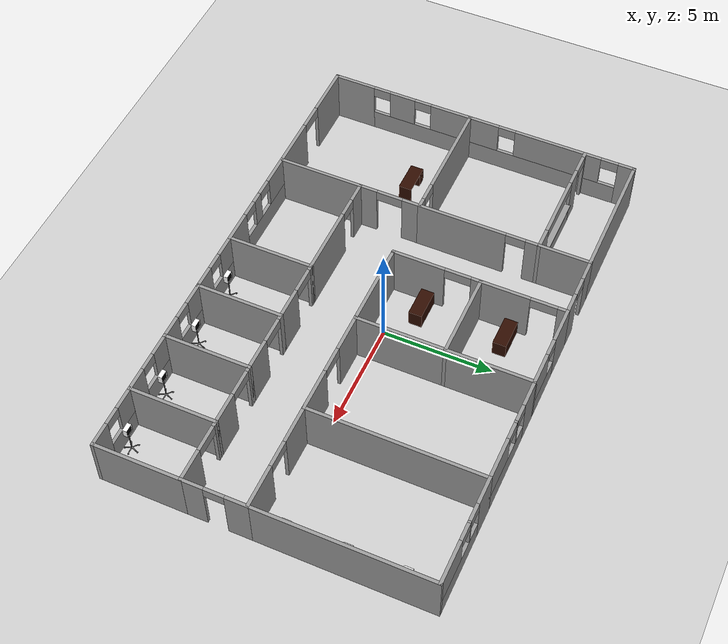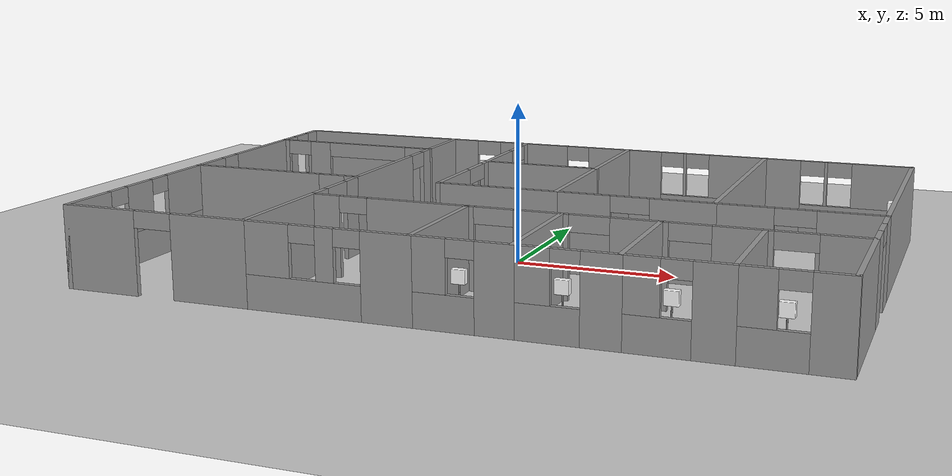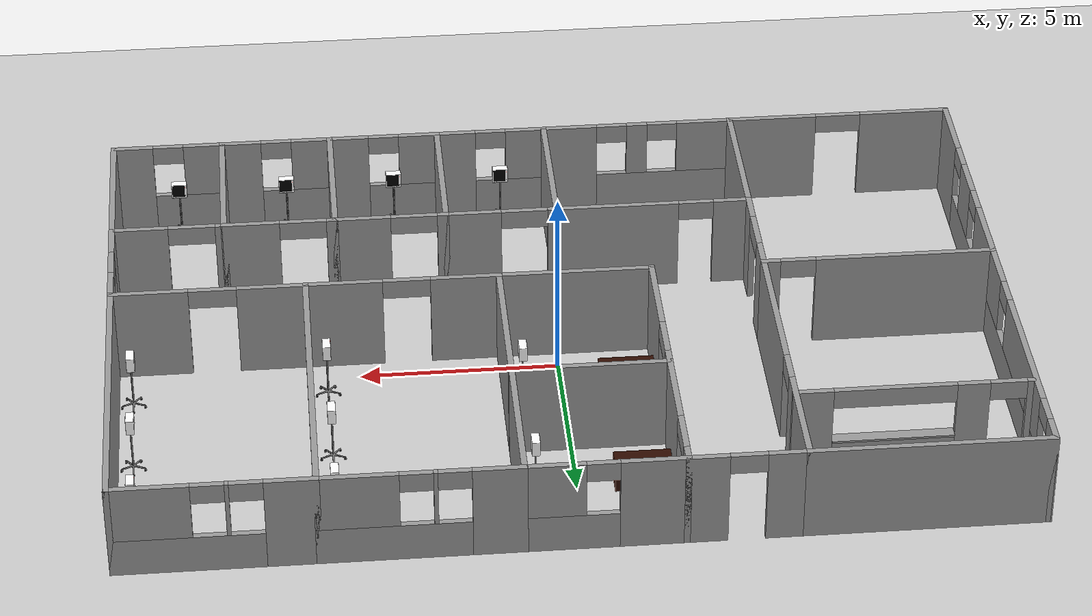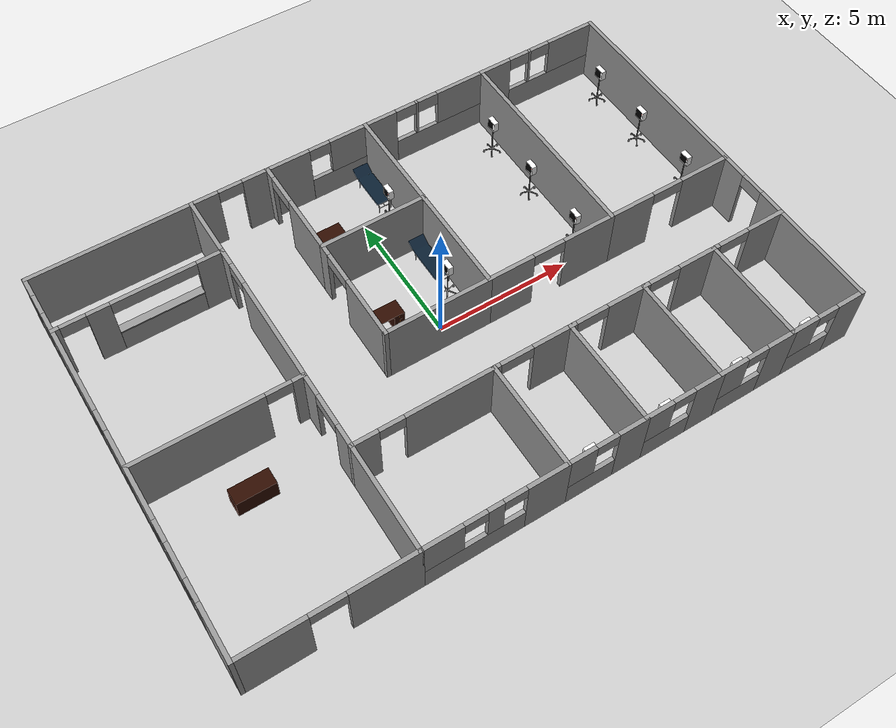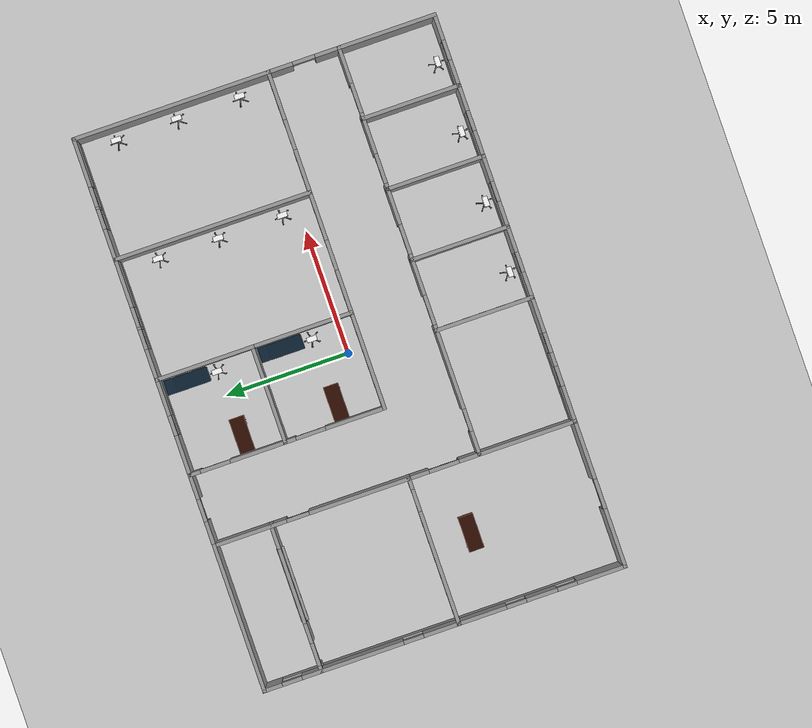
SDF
<sdf version="1.6">
 <world name="default">
  <light name="sun" type="directional">
   <pose>0 0 10 0 -0 0</pose>
   <diffuse>0.8 0.8 0.8 1</diffuse>
   <specular>0.1 0.1 0.1 1</specular>
   <attenuation>
    <range>1000</range>
    <constant>0.9</constant>
    <linear>0.01</linear>
    <quadratic>0.001</quadratic>
   </attenuation>
   <direction>-0.5 0.5 -1</direction>
  </light>
  <model name="ground_plane">
   <static>1</static>
   <link name="link">
    <collision name="collision">
     <geometry><plane><normal>0 0 1</normal><size>100 100</size></plane></geometry>
     <surface><friction><ode><mu>100</mu><mu2>50</mu2></ode></friction></surface>
    </collision>
    <visual name="visual">
     <cast_shadows>0</cast_shadows>
     <geometry><plane><normal>0 0 1</normal><size>100 100</size></plane></geometry>
     <material>
      <script><uri>file://media/materials/scripts/gazebo.material</uri><name>Gazebo/Grey</name></script>
     </material>
    </visual>
   </link>
  </model>
  <gravity>0 0 -9.8</gravity>
  <magnetic_field>6e-06 2.3e-05 -4.2e-05</magnetic_field>
  <atmosphere type="adiabatic"/>
  <physics name="default_physics" default="0" type="ode">
   <max_step_size>0.001</max_step_size>
   <real_time_factor>1</real_time_factor>
   <real_time_update_rate>1000</real_time_update_rate>
  </physics>
  <scene><ambient>0.4 0.4 0.4 1</ambient><background>0.7 0.7 0.7 1</background><shadows>1</shadows></scene>
  <spherical_coordinates>
   <surface_model>EARTH_WGS84</surface_model>
   <latitude_deg>0</latitude_deg>
   <longitude_deg>0</longitude_deg>
   <elevation>0</elevation>
   <heading_deg>0</heading_deg>
  </spherical_coordinates>
  <audio><device>default</device></audio>
  <model name="vitals_monitor">
   <static>1</static>
   <link name="vitals_monitor">
    <collision name="vitals_monitor">
     <geometry><mesh><uri>model://vitals_monitor/meshes/model.dae</uri></mesh></geometry>
    </collision>
    <visual name="vitals_monitor_mesh">
     <geometry><mesh><uri>model://vitals_monitor/meshes/model.dae</uri></mesh></geometry>
    </visual>
   </link>
   <pose>9.47829 -6.89873 0 0 -0 3.14159</pose>
  </model>
  <model name="vitals_monitor_clone">
   <static>1</static>
   <link name="vitals_monitor">
    <collision name="vitals_monitor">
     <geometry><mesh><uri>model://vitals_monitor/meshes/model.dae</uri></mesh></geometry>
    </collision>
    <visual name="vitals_monitor_mesh">
     <geometry><mesh><uri>model://vitals_monitor/meshes/model.dae</uri></mesh></geometry>
    </visual>
   </link>
   <pose>6.64162 -6.89863 0 0 -0 3.14159</pose>
  </model>
  <model name="vitals_monitor_clone_0">
   <static>1</static>
   <link name="vitals_monitor">
    <collision name="vitals_monitor">
     <geometry><mesh><uri>model://vitals_monitor/meshes/model.dae</uri></mesh></geometry>
    </collision>
    <visual name="vitals_monitor_mesh">
     <geometry><mesh><uri>model://vitals_monitor/meshes/model.dae</uri></mesh></geometry>
    </visual>
   </link>
   <pose>3.79191 -6.89962 0 0 -0 3.14159</pose>
  </model>
  <model name="vitals_monitor_clone_1">
   <static>1</static>
   <link name="vitals_monitor">
    <collision name="vitals_monitor">
     <geometry><mesh><uri>model://vitals_monitor/meshes/model.dae</uri></mesh></geometry>
    </collision>
    <visual name="vitals_monitor_mesh">
     <geometry><mesh><uri>model://vitals_monitor/meshes/model.dae</uri></mesh></geometry>
    </visual>
   </link>
   <pose>0.94132 -6.89183 0 0 -0 3.14159</pose>
  </model>
  <model name="vitals_monitor_clone_2">
   <static>1</static>
   <link name="vitals_monitor">
    <collision name="vitals_monitor">
     <geometry><mesh><uri>model://vitals_monitor/meshes/model.dae</uri></mesh></geometry>
    </collision>
    <visual name="vitals_monitor_mesh">
     <geometry><mesh><uri>model://vitals_monitor/meshes/model.dae</uri></mesh></geometry>
    </visual>
   </link>
   <pose>10.6596 5.74993 0 0 0 -1.5708</pose>
  </model>
  <model name="vitals_monitor_clone_2_clone">
   <static>1</static>
   <link name="vitals_monitor">
    <collision name="vitals_monitor">
     <geometry><mesh><uri>model://vitals_monitor/meshes/model.dae</uri></mesh></geometry>
    </collision>
    <visual name="vitals_monitor_mesh">
     <geometry><mesh><uri>model://vitals_monitor/meshes/model.dae</uri></mesh></geometry>
    </visual>
   </link>
   <pose>10.6882 3.29236 0 0 0 -1.5708</pose>
  </model>
  <model name="vitals_monitor_clone_2_clone_0">
   <static>1</static>
   <link name="vitals_monitor">
    <collision name="vitals_monitor">
     <geometry><mesh><uri>model://vitals_monitor/meshes/model.dae</uri></mesh></geometry>
    </collision>
    <visual name="vitals_monitor_mesh">
     <geometry><mesh><uri>model://vitals_monitor/meshes/model.dae</uri></mesh></geometry>
    </visual>
   </link>
   <pose>10.7026 0.733748 0 0 0 -1.5708</pose>
  </model>
  <model name="vitals_monitor_clone_2_clone_1">
   <static>1</static>
   <link name="vitals_monitor">
    <collision name="vitals_monitor">
     <geometry><mesh><uri>model://vitals_monitor/meshes/model.dae</uri></mesh></geometry>
    </collision>
    <visual name="vitals_monitor_mesh">
     <geometry><mesh><uri>model://vitals_monitor/meshes/model.dae</uri></mesh></geometry>
    </visual>
   </link>
   <pose>5.84678 0.669607 0 0 0 -1.5708</pose>
  </model>
  <model name="vitals_monitor_clone_2_clone_2">
   <static>1</static>
   <link name="vitals_monitor">
    <collision name="vitals_monitor">
     <geometry><mesh><uri>model://vitals_monitor/meshes/model.dae</uri></mesh></geometry>
    </collision>
    <visual name="vitals_monitor_mesh">
     <geometry><mesh><uri>model://vitals_monitor/meshes/model.dae</uri></mesh></geometry>
    </visual>
   </link>
   <pose>5.82137 3.28498 0 0 0 -1.5708</pose>
  </model>
  <model name="vitals_monitor_clone_2_clone_3">
   <static>1</static>
   <link name="vitals_monitor">
    <collision name="vitals_monitor">
     <geometry><mesh><uri>model://vitals_monitor/meshes/model.dae</uri></mesh></geometry>
    </collision>
    <visual name="vitals_monitor_mesh">
     <geometry><mesh><uri>model://vitals_monitor/meshes/model.dae</uri></mesh></geometry>
    </visual>
   </link>
   <pose>5.83292 5.71579 0 0 0 -1.5708</pose>
  </model>
  <model name="three_drawer_desk">
   <static>1</static>
   <link name="three_drawer_desk">
    <collision name="three_drawer_desk">
     <geometry><mesh><uri>model://three_drawer_desk/meshes/model.dae</uri></mesh></geometry>
    </collision>
    <visual name="three_drawer_desk_mesh">
     <geometry><mesh><uri>model://three_drawer_desk/meshes/model.dae</uri></mesh></geometry>
    </visual>
   </link>
   <pose>-1.618 4.9115 0 0 -0 3.14159</pose>
  </model>
  <model name="three_drawer_desk_clone">
   <static>1</static>
   <link name="three_drawer_desk">
    <collision name="three_drawer_desk">
     <geometry><mesh><uri>model://three_drawer_desk/meshes/model.dae</uri></mesh></geometry>
    </collision>
    <visual name="three_drawer_desk_mesh">
     <geometry><mesh><uri>model://three_drawer_desk/meshes/model.dae</uri></mesh></geometry>
    </visual>
   </link>
   <pose>-1.62836 1.05851 0 0 -0 3.14159</pose>
  </model>
  <model name="medical_couch">
   <static>1</static>
   <link name="medical_couch">
    <collision name="medical_couch">
     <geometry><mesh><uri>model://medical_couch/meshes/model.dae</uri></mesh></geometry>
    </collision>
    <visual name="medical_couch_mesh">
     <geometry><mesh><uri>model://medical_couch/meshes/model.dae</uri></mesh></geometry>
    </visual>
   </link>
   <pose>1.03141 6.05659 0 0 -0 3.14159</pose>
  </model>
  <model name="medical_couch_clone">
   <static>1</static>
   <link name="medical_couch">
    <collision name="medical_couch">
     <geometry><mesh><uri>model://medical_couch/meshes/model.dae</uri></mesh></geometry>
    </collision>
    <visual name="medical_couch_mesh">
     <geometry><mesh><uri>model://medical_couch/meshes/model.dae</uri></mesh></geometry>
    </visual>
   </link>
   <pose>1.03641 2.21268 0 0 -0 3.14159</pose>
  </model>
  <model name="vitals_monitor_clone_2_clone_3_clone">
   <static>1</static>
   <link name="vitals_monitor">
    <collision name="vitals_monitor">
     <geometry><mesh><uri>model://vitals_monitor/meshes/model.dae</uri></mesh></geometry>
    </collision>
    <visual name="vitals_monitor_mesh">
     <geometry><mesh><uri>model://vitals_monitor/meshes/model.dae</uri></mesh></geometry>
    </visual>
   </link>
   <pose>0.995211 4.99575 0 0 0 -1.5708</pose>
  </model>
  <model name="vitals_monitor_clone_2_clone_3_clone_0">
   <static>1</static>
   <link name="vitals_monitor">
    <collision name="vitals_monitor">
     <geometry><mesh><uri>model://vitals_monitor/meshes/model.dae</uri></mesh></geometry>
    </collision>
    <visual name="vitals_monitor_mesh">
     <geometry><mesh><uri>model://vitals_monitor/meshes/model.dae</uri></mesh></geometry>
    </visual>
   </link>
   <pose>0.989105 1.14447 0 0 0 -1.5708</pose>
  </model>
  <model name="three_drawer_desk_clone_0">
   <static>1</static>
   <link name="three_drawer_desk">
    <collision name="three_drawer_desk">
     <geometry><mesh><uri>model://three_drawer_desk/meshes/model.dae</uri></mesh></geometry>
    </collision>
    <visual name="three_drawer_desk_mesh">
     <geometry><mesh><uri>model://three_drawer_desk/meshes/model.dae</uri></mesh></geometry>
    </visual>
   </link>
   <pose>-8.08485 -2.2155 0 0 -0 0</pose>
  </model>
  <model name="hospital_v1">
   <link name="Wall_0">
    <pose>-8.2 7.275 0 0 -0 0</pose>
    <visual name="Wall_0_Visual">
     <pose>0 0 1.25 0 -0 0</pose>
     <geometry><box><size>6 0.15 2.5</size></box></geometry>
     <material>
      <script><uri>file://media/materials/scripts/gazebo.material</uri><name>Gazebo/Grey</name></script>
      <ambient>1 1 1 1</ambient>
     </material>
     <meta><layer>0</layer></meta>
    </visual>
    <collision name="Wall_0_Collision">
     <pose>0 0 1.25 0 -0 0</pose>
     <geometry><box><size>6 0.15 2.5</size></box></geometry>
     <surface>
      <friction>
       <ode><mu>1</mu><mu2>1</mu2><fdir1>0 0 0</fdir1><slip1>0</slip1><slip2>0</slip2></ode>
       <torsional>
        <coefficient>1</coefficient>
        <patch_radius>0</patch_radius>
        <surface_radius>0</surface_radius>
        <use_patch_radius>1</use_patch_radius>
        <ode><slip>0</slip></ode>
       </torsional>
      </friction>
      <bounce><restitution_coefficient>0</restitution_coefficient><threshold>1e+06</threshold></bounce>
      <contact>
       <collide_without_contact>0</collide_without_contact>
       <collide_without_contact_bitmask>1</collide_without_contact_bitmask>
       <collide_bitmask>1</collide_bitmask>
       <ode>
        <soft_cfm>0</soft_cfm>
        <soft_erp>0.2</soft_erp>
        <kp>1e+13</kp>
        <kd>1</kd>
        <max_vel>0.01</max_vel>
        <min_depth>0</min_depth>
       </ode>
       <bullet>
        <split_impulse>1</split_impulse>
        <split_impulse_penetration_threshold>-0.01</split_impulse_penetration_threshold>
        <soft_cfm>0</soft_cfm>
        <soft_erp>0.2</soft_erp>
        <kp>1e+13</kp>
        <kd>1</kd>
       </bullet>
      </contact>
     </surface>
    </collision>
   </link>
   <link name="Wall_0_clone">
    <pose>-8.2 4.975 0 0 -0 0</pose>
    <inertial>
     <mass>1</mass>
     <inertia><ixx>1</ixx><ixy>0</ixy><ixz>0</ixz><iyy>1</iyy><iyz>0</iyz><izz>1</izz></inertia>
    </inertial>
    <visual name="ModelPreview_4::Wall_0_clone::visual_1">
     <pose>0.5 0 0.5 0 -0 0</pose>
     <geometry><box><size>3 0.15 1</size></box></geometry>
     <material>
      <script><uri>file://media/materials/scripts/gazebo.material</uri><name>Gazebo/Grey</name></script>
      <ambient>1 1 1 1</ambient>
      <shader type="vertex"><normal_map>__default__</normal_map></shader>
      <diffuse>0.7 0.7 0.7 1</diffuse>
      <specular>0.01 0.01 0.01 1</specular>
      <emissive>0 0 0 1</emissive>
     </material>
     <meta><layer>0</layer></meta>
    </visual>
    <visual name="ModelPreview_10::Wall_0_clone::visual_6">
     <pose>0.5 0 1.025 0 -0 0</pose>
     <geometry><box><size>3 0.3 0.05</size></box></geometry>
     <material>
      <script><uri>file://media/materials/scripts/gazebo.material</uri><name>Gazebo/Grey</name></script>
      <ambient>1 1 1 1</ambient>
      <shader type="vertex"><normal_map>__default__</normal_map></shader>
      <diffuse>0.7 0.7 0.7 1</diffuse>
      <specular>0.01 0.01 0.01 1</specular>
      <emissive>0 0 0 1</emissive>
     </material>
     <meta><layer>0</layer></meta>
    </visual>
    <visual name="ModelPreview_4::Wall_0_clone::visual_3">
     <pose>-1.4 0 1.25 0 -0 0</pose>
     <geometry><box><size>0.8 0.15 2.5</size></box></geometry>
     <material>
      <script><uri>file://media/materials/scripts/gazebo.material</uri><name>Gazebo/Grey</name></script>
      <ambient>1 1 1 1</ambient>
      <shader type="vertex"><normal_map>__default__</normal_map></shader>
      <diffuse>0.7 0.7 0.7 1</diffuse>
      <specular>0.01 0.01 0.01 1</specular>
      <emissive>0 0 0 1</emissive>
     </material>
     <meta><layer>0</layer></meta>
    </visual>
    <visual name="ModelPreview_4::Wall_0_clone::visual_4">
     <pose>-2.25 0 2.25 0 -0 0</pose>
     <geometry><box><size>0.9 0.15 0.5</size></box></geometry>
     <material>
      <script><uri>file://media/materials/scripts/gazebo.material</uri><name>Gazebo/Grey</name></script>
      <ambient>1 1 1 1</ambient>
      <shader type="vertex"><normal_map>__default__</normal_map></shader>
      <diffuse>0.7 0.7 0.7 1</diffuse>
      <specular>0.01 0.01 0.01 1</specular>
      <emissive>0 0 0 1</emissive>
     </material>
     <meta><layer>0</layer></meta>
    </visual>
    <visual name="ModelPreview_4::Wall_0_clone::visual_5">
     <pose>-2.85 0 1.25 0 -0 0</pose>
     <geometry><box><size>0.3 0.15 2.5</size></box></geometry>
     <material>
      <script><uri>file://media/materials/scripts/gazebo.material</uri><name>Gazebo/Grey</name></script>
      <ambient>1 1 1 1</ambient>
      <shader type="vertex"><normal_map>__default__</normal_map></shader>
      <diffuse>0.7 0.7 0.7 1</diffuse>
      <specular>0.01 0.01 0.01 1</specular>
      <emissive>0 0 0 1</emissive>
     </material>
     <meta><layer>0</layer></meta>
    </visual>
    <visual name="ModelPreview_4::Wall_0_clone::visual_2">
     <pose>0.5 0 2.25 0 -0 0</pose>
     <geometry><box><size>3 0.15 0.5</size></box></geometry>
     <material>
      <script><uri>file://media/materials/scripts/gazebo.material</uri><name>Gazebo/Grey</name></script>
      <ambient>1 1 1 1</ambient>
      <shader type="vertex"><normal_map>__default__</normal_map></shader>
      <diffuse>0.7 0.7 0.7 1</diffuse>
      <specular>0.01 0.01 0.01 1</specular>
      <emissive>0 0 0 1</emissive>
     </material>
     <meta><layer>0</layer></meta>
    </visual>
    <visual name="Wall_0_Visual">
     <pose>2.5 0 1.25 0 -0 0</pose>
     <geometry><box><size>1 0.15 2.5</size></box></geometry>
     <material>
      <script><uri>file://media/materials/scripts/gazebo.material</uri><name>Gazebo/Grey</name></script>
      <ambient>1 1 1 1</ambient>
      <shader type="vertex"><normal_map>__default__</normal_map></shader>
      <diffuse>0.7 0.7 0.7 1</diffuse>
      <specular>0.01 0.01 0.01 1</specular>
      <emissive>0 0 0 1</emissive>
     </material>
     <meta><layer>0</layer></meta>
    </visual>
    <collision name="collision_3">
     <pose>-1.4 0 1.25 0 -0 0</pose>
     <geometry><box><size>0.8 0.15 2.5</size></box></geometry>
     <surface>
      <friction>
       <ode><mu>1</mu><mu2>1</mu2><fdir1>0 0 0</fdir1><slip1>0</slip1><slip2>0</slip2></ode>
       <torsional>
        <coefficient>1</coefficient>
        <patch_radius>0</patch_radius>
        <surface_radius>0</surface_radius>
        <use_patch_radius>1</use_patch_radius>
        <ode><slip>0</slip></ode>
       </torsional>
      </friction>
      <bounce><restitution_coefficient>0</restitution_coefficient><threshold>1e+06</threshold></bounce>
      <contact>
       <collide_without_contact>0</collide_without_contact>
       <collide_without_contact_bitmask>1</collide_without_contact_bitmask>
       <collide_bitmask>1</collide_bitmask>
       <ode>
        <soft_cfm>0</soft_cfm>
        <soft_erp>0.2</soft_erp>
        <kp>1e+13</kp>
        <kd>1</kd>
        <max_vel>0.01</max_vel>
        <min_depth>0</min_depth>
       </ode>
       <bullet>
        <split_impulse>1</split_impulse>
        <split_impulse_penetration_threshold>-0.01</split_impulse_penetration_threshold>
        <soft_cfm>0</soft_cfm>
        <soft_erp>0.2</soft_erp>
        <kp>1e+13</kp>
        <kd>1</kd>
       </bullet>
      </contact>
     </surface>
    </collision>
    <collision name="collision_1">
     <pose>0.5 0 0.5 0 -0 0</pose>
     <geometry><box><size>3 0.15 1</size></box></geometry>
     <surface>
      <friction>
       <ode><mu>1</mu><mu2>1</mu2><fdir1>0 0 0</fdir1><slip1>0</slip1><slip2>0</slip2></ode>
       <torsional>
        <coefficient>1</coefficient>
        <patch_radius>0</patch_radius>
        <surface_radius>0</surface_radius>
        <use_patch_radius>1</use_patch_radius>
        <ode><slip>0</slip></ode>
       </torsional>
      </friction>
      <bounce><restitution_coefficient>0</restitution_coefficient><threshold>1e+06</threshold></bounce>
      <contact>
       <collide_without_contact>0</collide_without_contact>
       <collide_without_contact_bitmask>1</collide_without_contact_bitmask>
       <collide_bitmask>1</collide_bitmask>
       <ode>
        <soft_cfm>0</soft_cfm>
        <soft_erp>0.2</soft_erp>
        <kp>1e+13</kp>
        <kd>1</kd>
        <max_vel>0.01</max_vel>
        <min_depth>0</min_depth>
       </ode>
       <bullet>
        <split_impulse>1</split_impulse>
        <split_impulse_penetration_threshold>-0.01</split_impulse_penetration_threshold>
        <soft_cfm>0</soft_cfm>
        <soft_erp>0.2</soft_erp>
        <kp>1e+13</kp>
        <kd>1</kd>
       </bullet>
      </contact>
     </surface>
    </collision>
    <collision name="collision_4">
     <pose>-2.25 0 2.25 0 -0 0</pose>
     <geometry><box><size>0.9 0.15 0.5</size></box></geometry>
     <surface>
      <friction>
       <ode><mu>1</mu><mu2>1</mu2><fdir1>0 0 0</fdir1><slip1>0</slip1><slip2>0</slip2></ode>
       <torsional>
        <coefficient>1</coefficient>
        <patch_radius>0</patch_radius>
        <surface_radius>0</surface_radius>
        <use_patch_radius>1</use_patch_radius>
        <ode><slip>0</slip></ode>
       </torsional>
      </friction>
      <bounce><restitution_coefficient>0</restitution_coefficient><threshold>1e+06</threshold></bounce>
      <contact>
       <collide_without_contact>0</collide_without_contact>
       <collide_without_contact_bitmask>1</collide_without_contact_bitmask>
       <collide_bitmask>1</collide_bitmask>
       <ode>
        <soft_cfm>0</soft_cfm>
        <soft_erp>0.2</soft_erp>
        <kp>1e+13</kp>
        <kd>1</kd>
        <max_vel>0.01</max_vel>
        <min_depth>0</min_depth>
       </ode>
       <bullet>
        <split_impulse>1</split_impulse>
        <split_impulse_penetration_threshold>-0.01</split_impulse_penetration_threshold>
        <soft_cfm>0</soft_cfm>
        <soft_erp>0.2</soft_erp>
        <kp>1e+13</kp>
        <kd>1</kd>
       </bullet>
      </contact>
     </surface>
    </collision>
    <collision name="collision_5">
     <pose>-2.85 0 1.25 0 -0 0</pose>
     <geometry><box><size>0.3 0.15 2.5</size></box></geometry>
     <surface>
      <friction>
       <ode><mu>1</mu><mu2>1</mu2><fdir1>0 0 0</fdir1><slip1>0</slip1><slip2>0</slip2></ode>
       <torsional>
        <coefficient>1</coefficient>
        <patch_radius>0</patch_radius>
        <surface_radius>0</surface_radius>
        <use_patch_radius>1</use_patch_radius>
        <ode><slip>0</slip></ode>
       </torsional>
      </friction>
      <bounce><restitution_coefficient>0</restitution_coefficient><threshold>1e+06</threshold></bounce>
      <contact>
       <collide_without_contact>0</collide_without_contact>
       <collide_without_contact_bitmask>1</collide_without_contact_bitmask>
       <collide_bitmask>1</collide_bitmask>
       <ode>
        <soft_cfm>0</soft_cfm>
        <soft_erp>0.2</soft_erp>
        <kp>1e+13</kp>
        <kd>1</kd>
        <max_vel>0.01</max_vel>
        <min_depth>0</min_depth>
       </ode>
       <bullet>
        <split_impulse>1</split_impulse>
        <split_impulse_penetration_threshold>-0.01</split_impulse_penetration_threshold>
        <soft_cfm>0</soft_cfm>
        <soft_erp>0.2</soft_erp>
        <kp>1e+13</kp>
        <kd>1</kd>
       </bullet>
      </contact>
     </surface>
    </collision>
    <collision name="collision_2">
     <pose>0.5 0 2.25 0 -0 0</pose>
     <geometry><box><size>3 0.15 0.5</size></box></geometry>
     <surface>
      <friction>
       <ode><mu>1</mu><mu2>1</mu2><fdir1>0 0 0</fdir1><slip1>0</slip1><slip2>0</slip2></ode>
       <torsional>
        <coefficient>1</coefficient>
        <patch_radius>0</patch_radius>
        <surface_radius>0</surface_radius>
        <use_patch_radius>1</use_patch_radius>
        <ode><slip>0</slip></ode>
       </torsional>
      </friction>
      <bounce><restitution_coefficient>0</restitution_coefficient><threshold>1e+06</threshold></bounce>
      <contact>
       <collide_without_contact>0</collide_without_contact>
       <collide_without_contact_bitmask>1</collide_without_contact_bitmask>
       <collide_bitmask>1</collide_bitmask>
       <ode>
        <soft_cfm>0</soft_cfm>
        <soft_erp>0.2</soft_erp>
        <kp>1e+13</kp>
        <kd>1</kd>
        <max_vel>0.01</max_vel>
        <min_depth>0</min_depth>
       </ode>
       <bullet>
        <split_impulse>1</split_impulse>
        <split_impulse_penetration_threshold>-0.01</split_impulse_penetration_threshold>
        <soft_cfm>0</soft_cfm>
        <soft_erp>0.2</soft_erp>
        <kp>1e+13</kp>
        <kd>1</kd>
       </bullet>
      </contact>
     </surface>
    </collision>
    <collision name="collision_6">
     <pose>0.5 0 1.025 0 -0 0</pose>
     <geometry><box><size>3 0.3 0.05</size></box></geometry>
     <surface>
      <friction>
       <ode><mu>1</mu><mu2>1</mu2><fdir1>0 0 0</fdir1><slip1>0</slip1><slip2>0</slip2></ode>
       <torsional>
        <coefficient>1</coefficient>
        <patch_radius>0</patch_radius>
        <surface_radius>0</surface_radius>
        <use_patch_radius>1</use_patch_radius>
        <ode><slip>0</slip></ode>
       </torsional>
      </friction>
      <bounce><restitution_coefficient>0</restitution_coefficient><threshold>1e+06</threshold></bounce>
      <contact>
       <collide_without_contact>0</collide_without_contact>
       <collide_without_contact_bitmask>1</collide_without_contact_bitmask>
       <collide_bitmask>1</collide_bitmask>
       <ode>
        <soft_cfm>0</soft_cfm>
        <soft_erp>0.2</soft_erp>
        <kp>1e+13</kp>
        <kd>1</kd>
        <max_vel>0.01</max_vel>
        <min_depth>0</min_depth>
       </ode>
       <bullet>
        <split_impulse>1</split_impulse>
        <split_impulse_penetration_threshold>-0.01</split_impulse_penetration_threshold>
        <soft_cfm>0</soft_cfm>
        <soft_erp>0.2</soft_erp>
        <kp>1e+13</kp>
        <kd>1</kd>
       </bullet>
      </contact>
     </surface>
    </collision>
    <collision name="Wall_0_Collision">
     <pose>2.5 0 1.25 0 -0 0</pose>
     <geometry><box><size>1 0.15 2.5</size></box></geometry>
     <surface>
      <friction>
       <ode><mu>1</mu><mu2>1</mu2><fdir1>0 0 0</fdir1><slip1>0</slip1><slip2>0</slip2></ode>
       <torsional>
        <coefficient>1</coefficient>
        <patch_radius>0</patch_radius>
        <surface_radius>0</surface_radius>
        <use_patch_radius>1</use_patch_radius>
        <ode><slip>0</slip></ode>
       </torsional>
      </friction>
      <bounce><restitution_coefficient>0</restitution_coefficient><threshold>1e+06</threshold></bounce>
      <contact>
       <collide_without_contact>0</collide_without_contact>
       <collide_without_contact_bitmask>1</collide_without_contact_bitmask>
       <collide_bitmask>1</collide_bitmask>
       <ode>
        <soft_cfm>0</soft_cfm>
        <soft_erp>0.2</soft_erp>
        <kp>1e+13</kp>
        <kd>1</kd>
        <max_vel>0.01</max_vel>
        <min_depth>0</min_depth>
       </ode>
       <bullet>
        <split_impulse>1</split_impulse>
        <split_impulse_penetration_threshold>-0.01</split_impulse_penetration_threshold>
        <soft_cfm>0</soft_cfm>
        <soft_erp>0.2</soft_erp>
        <kp>1e+13</kp>
        <kd>1</kd>
       </bullet>
      </contact>
     </surface>
    </collision>
   </link>
   <link name="Wall_10">
    <pose>1.425 5.35 0 0 0 -1.5708</pose>
    <visual name="Wall_10_Visual">
     <pose>0 0 1.25 0 -0 0</pose>
     <geometry><box><size>4 0.15 2.5</size></box></geometry>
     <material>
      <script><uri>file://media/materials/scripts/gazebo.material</uri><name>Gazebo/Grey</name></script>
      <ambient>1 1 1 1</ambient>
     </material>
     <meta><layer>0</layer></meta>
    </visual>
    <collision name="Wall_10_Collision">
     <pose>0 0 1.25 0 -0 0</pose>
     <geometry><box><size>4 0.15 2.5</size></box></geometry>
     <surface>
      <friction>
       <ode><mu>1</mu><mu2>1</mu2><fdir1>0 0 0</fdir1><slip1>0</slip1><slip2>0</slip2></ode>
       <torsional>
        <coefficient>1</coefficient>
        <patch_radius>0</patch_radius>
        <surface_radius>0</surface_radius>
        <use_patch_radius>1</use_patch_radius>
        <ode><slip>0</slip></ode>
       </torsional>
      </friction>
      <bounce><restitution_coefficient>0</restitution_coefficient><threshold>1e+06</threshold></bounce>
      <contact>
       <collide_without_contact>0</collide_without_contact>
       <collide_without_contact_bitmask>1</collide_without_contact_bitmask>
       <collide_bitmask>1</collide_bitmask>
       <ode>
        <soft_cfm>0</soft_cfm>
        <soft_erp>0.2</soft_erp>
        <kp>1e+13</kp>
        <kd>1</kd>
        <max_vel>0.01</max_vel>
        <min_depth>0</min_depth>
       </ode>
       <bullet>
        <split_impulse>1</split_impulse>
        <split_impulse_penetration_threshold>-0.01</split_impulse_penetration_threshold>
        <soft_cfm>0</soft_cfm>
        <soft_erp>0.2</soft_erp>
        <kp>1e+13</kp>
        <kd>1</kd>
       </bullet>
      </contact>
     </surface>
    </collision>
   </link>
   <link name="Wall_11">
    <pose>-0.5 3.425 0 0 -0 3.14159</pose>
    <visual name="Wall_11_Visual">
     <pose>0 0 1.25 0 -0 0</pose>
     <geometry><box><size>4 0.15 2.5</size></box></geometry>
     <material>
      <script><uri>file://media/materials/scripts/gazebo.material</uri><name>Gazebo/Grey</name></script>
      <ambient>1 1 1 1</ambient>
     </material>
     <meta><layer>0</layer></meta>
    </visual>
    <collision name="Wall_11_Collision">
     <pose>0 0 1.25 0 -0 0</pose>
     <geometry><box><size>4 0.15 2.5</size></box></geometry>
     <surface>
      <friction>
       <ode><mu>1</mu><mu2>1</mu2><fdir1>0 0 0</fdir1><slip1>0</slip1><slip2>0</slip2></ode>
       <torsional>
        <coefficient>1</coefficient>
        <patch_radius>0</patch_radius>
        <surface_radius>0</surface_radius>
        <use_patch_radius>1</use_patch_radius>
        <ode><slip>0</slip></ode>
       </torsional>
      </friction>
      <bounce><restitution_coefficient>0</restitution_coefficient><threshold>1e+06</threshold></bounce>
      <contact>
       <collide_without_contact>0</collide_without_contact>
       <collide_without_contact_bitmask>1</collide_without_contact_bitmask>
       <collide_bitmask>1</collide_bitmask>
       <ode>
        <soft_cfm>0</soft_cfm>
        <soft_erp>0.2</soft_erp>
        <kp>1e+13</kp>
        <kd>1</kd>
        <max_vel>0.01</max_vel>
        <min_depth>0</min_depth>
       </ode>
       <bullet>
        <split_impulse>1</split_impulse>
        <split_impulse_penetration_threshold>-0.01</split_impulse_penetration_threshold>
        <soft_cfm>0</soft_cfm>
        <soft_erp>0.2</soft_erp>
        <kp>1e+13</kp>
        <kd>1</kd>
       </bullet>
      </contact>
     </surface>
    </collision>
   </link>
   <link name="Wall_12">
    <pose>-2.425 5.35 0 0 -0 1.5708</pose>
    <visual name="Wall_12_Visual_0">
     <pose>-0.85 0 1.25 0 -0 0</pose>
     <geometry><box><size>2.3 0.15 2.5</size></box></geometry>
     <material>
      <script><uri>file://media/materials/scripts/gazebo.material</uri><name>Gazebo/Grey</name></script>
      <ambient>1 1 1 1</ambient>
     </material>
     <meta><layer>0</layer></meta>
    </visual>
    <visual name="Wall_12_Visual_2">
     <pose>0.9 0 2.25 0 -0 0</pose>
     <geometry><box><size>1.2 0.15 0.5</size></box></geometry>
     <material>
      <script><uri>file://media/materials/scripts/gazebo.material</uri><name>Gazebo/Grey</name></script>
      <ambient>1 1 1 1</ambient>
     </material>
     <meta><layer>0</layer></meta>
    </visual>
    <visual name="Wall_12_Visual_1">
     <pose>1.75 0 1.25 0 -0 0</pose>
     <geometry><box><size>0.5 0.15 2.5</size></box></geometry>
     <material>
      <script><uri>file://media/materials/scripts/gazebo.material</uri><name>Gazebo/Grey</name></script>
      <ambient>1 1 1 1</ambient>
     </material>
     <meta><layer>0</layer></meta>
    </visual>
    <collision name="Wall_12_Collision_1">
     <pose>1.75 0 1.25 0 -0 0</pose>
     <geometry><box><size>0.5 0.15 2.5</size></box></geometry>
     <surface>
      <friction>
       <ode><mu>1</mu><mu2>1</mu2><fdir1>0 0 0</fdir1><slip1>0</slip1><slip2>0</slip2></ode>
       <torsional>
        <coefficient>1</coefficient>
        <patch_radius>0</patch_radius>
        <surface_radius>0</surface_radius>
        <use_patch_radius>1</use_patch_radius>
        <ode><slip>0</slip></ode>
       </torsional>
      </friction>
      <bounce><restitution_coefficient>0</restitution_coefficient><threshold>1e+06</threshold></bounce>
      <contact>
       <collide_without_contact>0</collide_without_contact>
       <collide_without_contact_bitmask>1</collide_without_contact_bitmask>
       <collide_bitmask>1</collide_bitmask>
       <ode>
        <soft_cfm>0</soft_cfm>
        <soft_erp>0.2</soft_erp>
        <kp>1e+13</kp>
        <kd>1</kd>
        <max_vel>0.01</max_vel>
        <min_depth>0</min_depth>
       </ode>
       <bullet>
        <split_impulse>1</split_impulse>
        <split_impulse_penetration_threshold>-0.01</split_impulse_penetration_threshold>
        <soft_cfm>0</soft_cfm>
        <soft_erp>0.2</soft_erp>
        <kp>1e+13</kp>
        <kd>1</kd>
       </bullet>
      </contact>
     </surface>
    </collision>
    <collision name="Wall_12_Collision_2">
     <pose>0.9 0 2.25 0 -0 0</pose>
     <geometry><box><size>1.2 0.15 0.5</size></box></geometry>
     <surface>
      <friction>
       <ode><mu>1</mu><mu2>1</mu2><fdir1>0 0 0</fdir1><slip1>0</slip1><slip2>0</slip2></ode>
       <torsional>
        <coefficient>1</coefficient>
        <patch_radius>0</patch_radius>
        <surface_radius>0</surface_radius>
        <use_patch_radius>1</use_patch_radius>
        <ode><slip>0</slip></ode>
       </torsional>
      </friction>
      <bounce><restitution_coefficient>0</restitution_coefficient><threshold>1e+06</threshold></bounce>
      <contact>
       <collide_without_contact>0</collide_without_contact>
       <collide_without_contact_bitmask>1</collide_without_contact_bitmask>
       <collide_bitmask>1</collide_bitmask>
       <ode>
        <soft_cfm>0</soft_cfm>
        <soft_erp>0.2</soft_erp>
        <kp>1e+13</kp>
        <kd>1</kd>
        <max_vel>0.01</max_vel>
        <min_depth>0</min_depth>
       </ode>
       <bullet>
        <split_impulse>1</split_impulse>
        <split_impulse_penetration_threshold>-0.01</split_impulse_penetration_threshold>
        <soft_cfm>0</soft_cfm>
        <soft_erp>0.2</soft_erp>
        <kp>1e+13</kp>
        <kd>1</kd>
       </bullet>
      </contact>
     </surface>
    </collision>
    <collision name="Wall_12_Collision_0">
     <pose>-0.85 0 1.25 0 -0 0</pose>
     <geometry><box><size>2.3 0.15 2.5</size></box></geometry>
     <surface>
      <friction>
       <ode><mu>1</mu><mu2>1</mu2><fdir1>0 0 0</fdir1><slip1>0</slip1><slip2>0</slip2></ode>
       <torsional>
        <coefficient>1</coefficient>
        <patch_radius>0</patch_radius>
        <surface_radius>0</surface_radius>
        <use_patch_radius>1</use_patch_radius>
        <ode><slip>0</slip></ode>
       </torsional>
      </friction>
      <bounce><restitution_coefficient>0</restitution_coefficient><threshold>1e+06</threshold></bounce>
      <contact>
       <collide_without_contact>0</collide_without_contact>
       <collide_without_contact_bitmask>1</collide_without_contact_bitmask>
       <collide_bitmask>1</collide_bitmask>
       <ode>
        <soft_cfm>0</soft_cfm>
        <soft_erp>0.2</soft_erp>
        <kp>1e+13</kp>
        <kd>1</kd>
        <max_vel>0.01</max_vel>
        <min_depth>0</min_depth>
       </ode>
       <bullet>
        <split_impulse>1</split_impulse>
        <split_impulse_penetration_threshold>-0.01</split_impulse_penetration_threshold>
        <soft_cfm>0</soft_cfm>
        <soft_erp>0.2</soft_erp>
        <kp>1e+13</kp>
        <kd>1</kd>
       </bullet>
      </contact>
     </surface>
    </collision>
   </link>
   <link name="Wall_15">
    <pose>3.85 7.275 0 0 -0 0</pose>
    <inertial>
     <mass>1</mass>
     <inertia><ixx>1</ixx><ixy>0</ixy><ixz>0</ixz><iyy>1</iyy><iyz>0</iyz><izz>1</izz></inertia>
    </inertial>
    <visual name="Wall_15_Visual_2">
     <pose>-0.35 0 1.75 0 -0 0</pose>
     <geometry><box><size>0.1 0.15 1.5</size></box></geometry>
     <material>
      <script><uri>file://media/materials/scripts/gazebo.material</uri><name>Gazebo/Grey</name></script>
      <ambient>1 1 1 1</ambient>
      <shader type="vertex"><normal_map>__default__</normal_map></shader>
      <diffuse>0.7 0.7 0.7 1</diffuse>
      <specular>0.01 0.01 0.01 1</specular>
      <emissive>0 0 0 1</emissive>
     </material>
     <meta><layer>0</layer></meta>
    </visual>
    <visual name="Wall_15_Visual_3">
     <pose>1.5 0 1.75 0 -0 0</pose>
     <geometry><box><size>2 0.15 1.5</size></box></geometry>
     <material>
      <script><uri>file://media/materials/scripts/gazebo.material</uri><name>Gazebo/Grey</name></script>
      <ambient>1 1 1 1</ambient>
      <shader type="vertex"><normal_map>__default__</normal_map></shader>
      <diffuse>0.7 0.7 0.7 1</diffuse>
      <specular>0.01 0.01 0.01 1</specular>
      <emissive>0 0 0 1</emissive>
     </material>
     <meta><layer>0</layer></meta>
    </visual>
    <visual name="Wall_15_Visual_4">
     <pose>-0.8 0 2.25 0 -0 0</pose>
     <geometry><box><size>0.8 0.15 0.5</size></box></geometry>
     <material>
      <script><uri>file://media/materials/scripts/gazebo.material</uri><name>Gazebo/Grey</name></script>
      <ambient>1 1 1 1</ambient>
      <shader type="vertex"><normal_map>__default__</normal_map></shader>
      <diffuse>0.7 0.7 0.7 1</diffuse>
      <specular>0.01 0.01 0.01 1</specular>
      <emissive>0 0 0 1</emissive>
     </material>
     <meta><layer>0</layer></meta>
    </visual>
    <visual name="Wall_15_Visual_0">
     <pose>-1.85 0 1.25 0 -0 0</pose>
     <geometry><box><size>1.3 0.15 2.5</size></box></geometry>
     <material>
      <script><uri>file://media/materials/scripts/gazebo.material</uri><name>Gazebo/Grey</name></script>
      <ambient>1 1 1 1</ambient>
      <shader type="vertex"><normal_map>__default__</normal_map></shader>
      <diffuse>0.7 0.7 0.7 1</diffuse>
      <specular>0.01 0.01 0.01 1</specular>
      <emissive>0 0 0 1</emissive>
     </material>
     <meta><layer>0</layer></meta>
    </visual>
    <visual name="Wall_15_Visual_5">
     <pose>0.1 0 2.25 0 -0 0</pose>
     <geometry><box><size>0.8 0.15 0.5</size></box></geometry>
     <material>
      <script><uri>file://media/materials/scripts/gazebo.material</uri><name>Gazebo/Grey</name></script>
      <ambient>1 1 1 1</ambient>
      <shader type="vertex"><normal_map>__default__</normal_map></shader>
      <diffuse>0.7 0.7 0.7 1</diffuse>
      <specular>0.01 0.01 0.01 1</specular>
      <emissive>0 0 0 1</emissive>
     </material>
     <meta><layer>0</layer></meta>
    </visual>
    <visual name="Wall_15_Visual_1">
     <pose>0.65 0 0.5 0 -0 0</pose>
     <geometry><box><size>3.7 0.15 1</size></box></geometry>
     <material>
      <script><uri>file://media/materials/scripts/gazebo.material</uri><name>Gazebo/Grey</name></script>
      <ambient>1 1 1 1</ambient>
      <shader type="vertex"><normal_map>__default__</normal_map></shader>
      <diffuse>0.7 0.7 0.7 1</diffuse>
      <specular>0.01 0.01 0.01 1</specular>
      <emissive>0 0 0 1</emissive>
     </material>
     <meta><layer>0</layer></meta>
    </visual>
    <collision name="Wall_15_Collision_4">
     <pose>-0.8 0 2.25 0 -0 0</pose>
     <geometry><box><size>0.8 0.15 0.5</size></box></geometry>
     <surface>
      <friction>
       <ode><mu>1</mu><mu2>1</mu2><fdir1>0 0 0</fdir1><slip1>0</slip1><slip2>0</slip2></ode>
       <torsional>
        <coefficient>1</coefficient>
        <patch_radius>0</patch_radius>
        <surface_radius>0</surface_radius>
        <use_patch_radius>1</use_patch_radius>
        <ode><slip>0</slip></ode>
       </torsional>
      </friction>
      <bounce><restitution_coefficient>0</restitution_coefficient><threshold>1e+06</threshold></bounce>
      <contact>
       <collide_without_contact>0</collide_without_contact>
       <collide_without_contact_bitmask>1</collide_without_contact_bitmask>
       <collide_bitmask>1</collide_bitmask>
       <ode>
        <soft_cfm>0</soft_cfm>
        <soft_erp>0.2</soft_erp>
        <kp>1e+13</kp>
        <kd>1</kd>
        <max_vel>0.01</max_vel>
        <min_depth>0</min_depth>
       </ode>
       <bullet>
        <split_impulse>1</split_impulse>
        <split_impulse_penetration_threshold>-0.01</split_impulse_penetration_threshold>
        <soft_cfm>0</soft_cfm>
        <soft_erp>0.2</soft_erp>
        <kp>1e+13</kp>
        <kd>1</kd>
       </bullet>
      </contact>
     </surface>
    </collision>
    <collision name="Wall_15_Collision_2">
     <pose>-0.35 0 1.75 0 -0 0</pose>
     <geometry><box><size>0.1 0.15 1.5</size></box></geometry>
     <surface>
      <friction>
       <ode><mu>1</mu><mu2>1</mu2><fdir1>0 0 0</fdir1><slip1>0</slip1><slip2>0</slip2></ode>
       <torsional>
        <coefficient>1</coefficient>
        <patch_radius>0</patch_radius>
        <surface_radius>0</surface_radius>
        <use_patch_radius>1</use_patch_radius>
        <ode><slip>0</slip></ode>
       </torsional>
      </friction>
      <bounce><restitution_coefficient>0</restitution_coefficient><threshold>1e+06</threshold></bounce>
      <contact>
       <collide_without_contact>0</collide_without_contact>
       <collide_without_contact_bitmask>1</collide_without_contact_bitmask>
       <collide_bitmask>1</collide_bitmask>
       <ode>
        <soft_cfm>0</soft_cfm>
        <soft_erp>0.2</soft_erp>
        <kp>1e+13</kp>
        <kd>1</kd>
        <max_vel>0.01</max_vel>
        <min_depth>0</min_depth>
       </ode>
       <bullet>
        <split_impulse>1</split_impulse>
        <split_impulse_penetration_threshold>-0.01</split_impulse_penetration_threshold>
        <soft_cfm>0</soft_cfm>
        <soft_erp>0.2</soft_erp>
        <kp>1e+13</kp>
        <kd>1</kd>
       </bullet>
      </contact>
     </surface>
    </collision>
    <collision name="Wall_15_Collision_5">
     <pose>0.1 0 2.25 0 -0 0</pose>
     <geometry><box><size>0.8 0.15 0.5</size></box></geometry>
     <surface>
      <friction>
       <ode><mu>1</mu><mu2>1</mu2><fdir1>0 0 0</fdir1><slip1>0</slip1><slip2>0</slip2></ode>
       <torsional>
        <coefficient>1</coefficient>
        <patch_radius>0</patch_radius>
        <surface_radius>0</surface_radius>
        <use_patch_radius>1</use_patch_radius>
        <ode><slip>0</slip></ode>
       </torsional>
      </friction>
      <bounce><restitution_coefficient>0</restitution_coefficient><threshold>1e+06</threshold></bounce>
      <contact>
       <collide_without_contact>0</collide_without_contact>
       <collide_without_contact_bitmask>1</collide_without_contact_bitmask>
       <collide_bitmask>1</collide_bitmask>
       <ode>
        <soft_cfm>0</soft_cfm>
        <soft_erp>0.2</soft_erp>
        <kp>1e+13</kp>
        <kd>1</kd>
        <max_vel>0.01</max_vel>
        <min_depth>0</min_depth>
       </ode>
       <bullet>
        <split_impulse>1</split_impulse>
        <split_impulse_penetration_threshold>-0.01</split_impulse_penetration_threshold>
        <soft_cfm>0</soft_cfm>
        <soft_erp>0.2</soft_erp>
        <kp>1e+13</kp>
        <kd>1</kd>
       </bullet>
      </contact>
     </surface>
    </collision>
    <collision name="Wall_15_Collision_0">
     <pose>-1.85 0 1.25 0 -0 0</pose>
     <geometry><box><size>1.3 0.15 2.5</size></box></geometry>
     <surface>
      <friction>
       <ode><mu>1</mu><mu2>1</mu2><fdir1>0 0 0</fdir1><slip1>0</slip1><slip2>0</slip2></ode>
       <torsional>
        <coefficient>1</coefficient>
        <patch_radius>0</patch_radius>
        <surface_radius>0</surface_radius>
        <use_patch_radius>1</use_patch_radius>
        <ode><slip>0</slip></ode>
       </torsional>
      </friction>
      <bounce><restitution_coefficient>0</restitution_coefficient><threshold>1e+06</threshold></bounce>
      <contact>
       <collide_without_contact>0</collide_without_contact>
       <collide_without_contact_bitmask>1</collide_without_contact_bitmask>
       <collide_bitmask>1</collide_bitmask>
       <ode>
        <soft_cfm>0</soft_cfm>
        <soft_erp>0.2</soft_erp>
        <kp>1e+13</kp>
        <kd>1</kd>
        <max_vel>0.01</max_vel>
        <min_depth>0</min_depth>
       </ode>
       <bullet>
        <split_impulse>1</split_impulse>
        <split_impulse_penetration_threshold>-0.01</split_impulse_penetration_threshold>
        <soft_cfm>0</soft_cfm>
        <soft_erp>0.2</soft_erp>
        <kp>1e+13</kp>
        <kd>1</kd>
       </bullet>
      </contact>
     </surface>
    </collision>
    <collision name="Wall_15_Collision_3">
     <pose>1.5 0 1.75 0 -0 0</pose>
     <geometry><box><size>2 0.15 1.5</size></box></geometry>
     <surface>
      <friction>
       <ode><mu>1</mu><mu2>1</mu2><fdir1>0 0 0</fdir1><slip1>0</slip1><slip2>0</slip2></ode>
       <torsional>
        <coefficient>1</coefficient>
        <patch_radius>0</patch_radius>
        <surface_radius>0</surface_radius>
        <use_patch_radius>1</use_patch_radius>
        <ode><slip>0</slip></ode>
       </torsional>
      </friction>
      <bounce><restitution_coefficient>0</restitution_coefficient><threshold>1e+06</threshold></bounce>
      <contact>
       <collide_without_contact>0</collide_without_contact>
       <collide_without_contact_bitmask>1</collide_without_contact_bitmask>
       <collide_bitmask>1</collide_bitmask>
       <ode>
        <soft_cfm>0</soft_cfm>
        <soft_erp>0.2</soft_erp>
        <kp>1e+13</kp>
        <kd>1</kd>
        <max_vel>0.01</max_vel>
        <min_depth>0</min_depth>
       </ode>
       <bullet>
        <split_impulse>1</split_impulse>
        <split_impulse_penetration_threshold>-0.01</split_impulse_penetration_threshold>
        <soft_cfm>0</soft_cfm>
        <soft_erp>0.2</soft_erp>
        <kp>1e+13</kp>
        <kd>1</kd>
       </bullet>
      </contact>
     </surface>
    </collision>
    <collision name="Wall_15_Collision_1">
     <pose>0.65 0 0.5 0 -0 0</pose>
     <geometry><box><size>3.7 0.15 1</size></box></geometry>
     <surface>
      <friction>
       <ode><mu>1</mu><mu2>1</mu2><fdir1>0 0 0</fdir1><slip1>0</slip1><slip2>0</slip2></ode>
       <torsional>
        <coefficient>1</coefficient>
        <patch_radius>0</patch_radius>
        <surface_radius>0</surface_radius>
        <use_patch_radius>1</use_patch_radius>
        <ode><slip>0</slip></ode>
       </torsional>
      </friction>
      <bounce><restitution_coefficient>0</restitution_coefficient><threshold>1e+06</threshold></bounce>
      <contact>
       <collide_without_contact>0</collide_without_contact>
       <collide_without_contact_bitmask>1</collide_without_contact_bitmask>
       <collide_bitmask>1</collide_bitmask>
       <ode>
        <soft_cfm>0</soft_cfm>
        <soft_erp>0.2</soft_erp>
        <kp>1e+13</kp>
        <kd>1</kd>
        <max_vel>0.01</max_vel>
        <min_depth>0</min_depth>
       </ode>
       <bullet>
        <split_impulse>1</split_impulse>
        <split_impulse_penetration_threshold>-0.01</split_impulse_penetration_threshold>
        <soft_cfm>0</soft_cfm>
        <soft_erp>0.2</soft_erp>
        <kp>1e+13</kp>
        <kd>1</kd>
       </bullet>
      </contact>
     </surface>
    </collision>
   </link>
   <link name="Wall_16">
    <pose>6.275 3.35 0 0 0 -1.5708</pose>
    <visual name="Wall_16_Visual">
     <pose>0 0 1.25 0 -0 0</pose>
     <geometry><box><size>8 0.15 2.5</size></box></geometry>
     <material>
      <script><uri>file://media/materials/scripts/gazebo.material</uri><name>Gazebo/Grey</name></script>
      <ambient>1 1 1 1</ambient>
     </material>
     <meta><layer>0</layer></meta>
    </visual>
    <collision name="Wall_16_Collision">
     <pose>0 0 1.25 0 -0 0</pose>
     <geometry><box><size>8 0.15 2.5</size></box></geometry>
     <surface>
      <friction>
       <ode><mu>1</mu><mu2>1</mu2><fdir1>0 0 0</fdir1><slip1>0</slip1><slip2>0</slip2></ode>
       <torsional>
        <coefficient>1</coefficient>
        <patch_radius>0</patch_radius>
        <surface_radius>0</surface_radius>
        <use_patch_radius>1</use_patch_radius>
        <ode><slip>0</slip></ode>
       </torsional>
      </friction>
      <bounce><restitution_coefficient>0</restitution_coefficient><threshold>1e+06</threshold></bounce>
      <contact>
       <collide_without_contact>0</collide_without_contact>
       <collide_without_contact_bitmask>1</collide_without_contact_bitmask>
       <collide_bitmask>1</collide_bitmask>
       <ode>
        <soft_cfm>0</soft_cfm>
        <soft_erp>0.2</soft_erp>
        <kp>1e+13</kp>
        <kd>1</kd>
        <max_vel>0.01</max_vel>
        <min_depth>0</min_depth>
       </ode>
       <bullet>
        <split_impulse>1</split_impulse>
        <split_impulse_penetration_threshold>-0.01</split_impulse_penetration_threshold>
        <soft_cfm>0</soft_cfm>
        <soft_erp>0.2</soft_erp>
        <kp>1e+13</kp>
        <kd>1</kd>
       </bullet>
      </contact>
     </surface>
    </collision>
   </link>
   <link name="Wall_17">
    <pose>3.85 -0.575 0 0 -0 3.14159</pose>
    <visual name="Wall_17_Visual_2">
     <pose>0.1 0 2.25 0 -0 0</pose>
     <geometry><box><size>1.2 0.15 0.5</size></box></geometry>
     <material>
      <script><uri>file://media/materials/scripts/gazebo.material</uri><name>Gazebo/Grey</name></script>
      <ambient>1 1 1 1</ambient>
     </material>
     <meta><layer>0</layer></meta>
    </visual>
    <visual name="Wall_17_Visual_1">
     <pose>1.6 0 1.25 0 -0 0</pose>
     <geometry><box><size>1.8 0.15 2.5</size></box></geometry>
     <material>
      <script><uri>file://media/materials/scripts/gazebo.material</uri><name>Gazebo/Grey</name></script>
      <ambient>1 1 1 1</ambient>
     </material>
     <meta><layer>0</layer></meta>
    </visual>
    <visual name="Wall_17_Visual_0">
     <pose>-1.5 0 1.25 0 -0 0</pose>
     <geometry><box><size>2 0.15 2.5</size></box></geometry>
     <material>
      <script><uri>file://media/materials/scripts/gazebo.material</uri><name>Gazebo/Grey</name></script>
      <ambient>1 1 1 1</ambient>
     </material>
     <meta><layer>0</layer></meta>
    </visual>
    <collision name="Wall_17_Collision_1">
     <pose>1.6 0 1.25 0 -0 0</pose>
     <geometry><box><size>1.8 0.15 2.5</size></box></geometry>
     <surface>
      <friction>
       <ode><mu>1</mu><mu2>1</mu2><fdir1>0 0 0</fdir1><slip1>0</slip1><slip2>0</slip2></ode>
       <torsional>
        <coefficient>1</coefficient>
        <patch_radius>0</patch_radius>
        <surface_radius>0</surface_radius>
        <use_patch_radius>1</use_patch_radius>
        <ode><slip>0</slip></ode>
       </torsional>
      </friction>
      <bounce><restitution_coefficient>0</restitution_coefficient><threshold>1e+06</threshold></bounce>
      <contact>
       <collide_without_contact>0</collide_without_contact>
       <collide_without_contact_bitmask>1</collide_without_contact_bitmask>
       <collide_bitmask>1</collide_bitmask>
       <ode>
        <soft_cfm>0</soft_cfm>
        <soft_erp>0.2</soft_erp>
        <kp>1e+13</kp>
        <kd>1</kd>
        <max_vel>0.01</max_vel>
        <min_depth>0</min_depth>
       </ode>
       <bullet>
        <split_impulse>1</split_impulse>
        <split_impulse_penetration_threshold>-0.01</split_impulse_penetration_threshold>
        <soft_cfm>0</soft_cfm>
        <soft_erp>0.2</soft_erp>
        <kp>1e+13</kp>
        <kd>1</kd>
       </bullet>
      </contact>
     </surface>
    </collision>
    <collision name="Wall_17_Collision_2">
     <pose>0.1 0 2.25 0 -0 0</pose>
     <geometry><box><size>1.2 0.15 0.5</size></box></geometry>
     <surface>
      <friction>
       <ode><mu>1</mu><mu2>1</mu2><fdir1>0 0 0</fdir1><slip1>0</slip1><slip2>0</slip2></ode>
       <torsional>
        <coefficient>1</coefficient>
        <patch_radius>0</patch_radius>
        <surface_radius>0</surface_radius>
        <use_patch_radius>1</use_patch_radius>
        <ode><slip>0</slip></ode>
       </torsional>
      </friction>
      <bounce><restitution_coefficient>0</restitution_coefficient><threshold>1e+06</threshold></bounce>
      <contact>
       <collide_without_contact>0</collide_without_contact>
       <collide_without_contact_bitmask>1</collide_without_contact_bitmask>
       <collide_bitmask>1</collide_bitmask>
       <ode>
        <soft_cfm>0</soft_cfm>
        <soft_erp>0.2</soft_erp>
        <kp>1e+13</kp>
        <kd>1</kd>
        <max_vel>0.01</max_vel>
        <min_depth>0</min_depth>
       </ode>
       <bullet>
        <split_impulse>1</split_impulse>
        <split_impulse_penetration_threshold>-0.01</split_impulse_penetration_threshold>
        <soft_cfm>0</soft_cfm>
        <soft_erp>0.2</soft_erp>
        <kp>1e+13</kp>
        <kd>1</kd>
       </bullet>
      </contact>
     </surface>
    </collision>
    <collision name="Wall_17_Collision_0">
     <pose>-1.5 0 1.25 0 -0 0</pose>
     <geometry><box><size>2 0.15 2.5</size></box></geometry>
     <surface>
      <friction>
       <ode><mu>1</mu><mu2>1</mu2><fdir1>0 0 0</fdir1><slip1>0</slip1><slip2>0</slip2></ode>
       <torsional>
        <coefficient>1</coefficient>
        <patch_radius>0</patch_radius>
        <surface_radius>0</surface_radius>
        <use_patch_radius>1</use_patch_radius>
        <ode><slip>0</slip></ode>
       </torsional>
      </friction>
      <bounce><restitution_coefficient>0</restitution_coefficient><threshold>1e+06</threshold></bounce>
      <contact>
       <collide_without_contact>0</collide_without_contact>
       <collide_without_contact_bitmask>1</collide_without_contact_bitmask>
       <collide_bitmask>1</collide_bitmask>
       <ode>
        <soft_cfm>0</soft_cfm>
        <soft_erp>0.2</soft_erp>
        <kp>1e+13</kp>
        <kd>1</kd>
        <max_vel>0.01</max_vel>
        <min_depth>0</min_depth>
       </ode>
       <bullet>
        <split_impulse>1</split_impulse>
        <split_impulse_penetration_threshold>-0.01</split_impulse_penetration_threshold>
        <soft_cfm>0</soft_cfm>
        <soft_erp>0.2</soft_erp>
        <kp>1e+13</kp>
        <kd>1</kd>
       </bullet>
      </contact>
     </surface>
    </collision>
   </link>
   <link name="Wall_18">
    <pose>1.425 1.425 0 0 -0 1.5708</pose>
    <visual name="Wall_18_Visual">
     <pose>0 0 1.25 0 -0 0</pose>
     <geometry><box><size>4.15 0.15 2.5</size></box></geometry>
     <material>
      <script><uri>file://media/materials/scripts/gazebo.material</uri><name>Gazebo/Grey</name></script>
      <ambient>1 1 1 1</ambient>
     </material>
     <meta><layer>0</layer></meta>
    </visual>
    <collision name="Wall_18_Collision">
     <pose>0 0 1.25 0 -0 0</pose>
     <geometry><box><size>4.15 0.15 2.5</size></box></geometry>
     <surface>
      <friction>
       <ode><mu>1</mu><mu2>1</mu2><fdir1>0 0 0</fdir1><slip1>0</slip1><slip2>0</slip2></ode>
       <torsional>
        <coefficient>1</coefficient>
        <patch_radius>0</patch_radius>
        <surface_radius>0</surface_radius>
        <use_patch_radius>1</use_patch_radius>
        <ode><slip>0</slip></ode>
       </torsional>
      </friction>
      <bounce><restitution_coefficient>0</restitution_coefficient><threshold>1e+06</threshold></bounce>
      <contact>
       <collide_without_contact>0</collide_without_contact>
       <collide_without_contact_bitmask>1</collide_without_contact_bitmask>
       <collide_bitmask>1</collide_bitmask>
       <ode>
        <soft_cfm>0</soft_cfm>
        <soft_erp>0.2</soft_erp>
        <kp>1e+13</kp>
        <kd>1</kd>
        <max_vel>0.01</max_vel>
        <min_depth>0</min_depth>
       </ode>
       <bullet>
        <split_impulse>1</split_impulse>
        <split_impulse_penetration_threshold>-0.01</split_impulse_penetration_threshold>
        <soft_cfm>0</soft_cfm>
        <soft_erp>0.2</soft_erp>
        <kp>1e+13</kp>
        <kd>1</kd>
       </bullet>
      </contact>
     </surface>
    </collision>
   </link>
   <link name="Wall_20">
    <pose>-0.5 -0.575 0 0 -0 3.14159</pose>
    <visual name="Wall_20_Visual">
     <pose>0 0 1.25 0 -0 0</pose>
     <geometry><box><size>4 0.15 2.5</size></box></geometry>
     <material>
      <script><uri>file://media/materials/scripts/gazebo.material</uri><name>Gazebo/Grey</name></script>
      <ambient>1 1 1 1</ambient>
     </material>
     <meta><layer>0</layer></meta>
    </visual>
    <collision name="Wall_20_Collision">
     <pose>0 0 1.25 0 -0 0</pose>
     <geometry><box><size>4 0.15 2.5</size></box></geometry>
     <surface>
      <friction>
       <ode><mu>1</mu><mu2>1</mu2><fdir1>0 0 0</fdir1><slip1>0</slip1><slip2>0</slip2></ode>
       <torsional>
        <coefficient>1</coefficient>
        <patch_radius>0</patch_radius>
        <surface_radius>0</surface_radius>
        <use_patch_radius>1</use_patch_radius>
        <ode><slip>0</slip></ode>
       </torsional>
      </friction>
      <bounce><restitution_coefficient>0</restitution_coefficient><threshold>1e+06</threshold></bounce>
      <contact>
       <collide_without_contact>0</collide_without_contact>
       <collide_without_contact_bitmask>1</collide_without_contact_bitmask>
       <collide_bitmask>1</collide_bitmask>
       <ode>
        <soft_cfm>0</soft_cfm>
        <soft_erp>0.2</soft_erp>
        <kp>1e+13</kp>
        <kd>1</kd>
        <max_vel>0.01</max_vel>
        <min_depth>0</min_depth>
       </ode>
       <bullet>
        <split_impulse>1</split_impulse>
        <split_impulse_penetration_threshold>-0.01</split_impulse_penetration_threshold>
        <soft_cfm>0</soft_cfm>
        <soft_erp>0.2</soft_erp>
        <kp>1e+13</kp>
        <kd>1</kd>
       </bullet>
      </contact>
     </surface>
    </collision>
   </link>
   <link name="Wall_21">
    <pose>-2.425 1.425 0 0 -0 1.5708</pose>
    <visual name="Wall_21_Visual_0">
     <pose>-0.85 0 1.25 0 -0 0</pose>
     <geometry><box><size>2.45 0.15 2.5</size></box></geometry>
     <material>
      <script><uri>file://media/materials/scripts/gazebo.material</uri><name>Gazebo/Grey</name></script>
      <ambient>1 1 1 1</ambient>
     </material>
     <meta><layer>0</layer></meta>
    </visual>
    <visual name="Wall_21_Visual_1">
     <pose>1.825 0 1.25 0 -0 0</pose>
     <geometry><box><size>0.5 0.15 2.5</size></box></geometry>
     <material>
      <script><uri>file://media/materials/scripts/gazebo.material</uri><name>Gazebo/Grey</name></script>
      <ambient>1 1 1 1</ambient>
     </material>
     <meta><layer>0</layer></meta>
    </visual>
    <visual name="Wall_21_Visual_2">
     <pose>0.975 0 2.25 0 -0 0</pose>
     <geometry><box><size>1.2 0.15 0.5</size></box></geometry>
     <material>
      <script><uri>file://media/materials/scripts/gazebo.material</uri><name>Gazebo/Grey</name></script>
      <ambient>1 1 1 1</ambient>
     </material>
     <meta><layer>0</layer></meta>
    </visual>
    <collision name="Wall_21_Collision_1">
     <pose>1.825 0 1.25 0 -0 0</pose>
     <geometry><box><size>0.5 0.15 2.5</size></box></geometry>
     <surface>
      <friction>
       <ode><mu>1</mu><mu2>1</mu2><fdir1>0 0 0</fdir1><slip1>0</slip1><slip2>0</slip2></ode>
       <torsional>
        <coefficient>1</coefficient>
        <patch_radius>0</patch_radius>
        <surface_radius>0</surface_radius>
        <use_patch_radius>1</use_patch_radius>
        <ode><slip>0</slip></ode>
       </torsional>
      </friction>
      <bounce><restitution_coefficient>0</restitution_coefficient><threshold>1e+06</threshold></bounce>
      <contact>
       <collide_without_contact>0</collide_without_contact>
       <collide_without_contact_bitmask>1</collide_without_contact_bitmask>
       <collide_bitmask>1</collide_bitmask>
       <ode>
        <soft_cfm>0</soft_cfm>
        <soft_erp>0.2</soft_erp>
        <kp>1e+13</kp>
        <kd>1</kd>
        <max_vel>0.01</max_vel>
        <min_depth>0</min_depth>
       </ode>
       <bullet>
        <split_impulse>1</split_impulse>
        <split_impulse_penetration_threshold>-0.01</split_impulse_penetration_threshold>
        <soft_cfm>0</soft_cfm>
        <soft_erp>0.2</soft_erp>
        <kp>1e+13</kp>
        <kd>1</kd>
       </bullet>
      </contact>
     </surface>
    </collision>
    <collision name="Wall_21_Collision_0">
     <pose>-0.85 0 1.25 0 -0 0</pose>
     <geometry><box><size>2.45 0.15 2.5</size></box></geometry>
     <surface>
      <friction>
       <ode><mu>1</mu><mu2>1</mu2><fdir1>0 0 0</fdir1><slip1>0</slip1><slip2>0</slip2></ode>
       <torsional>
        <coefficient>1</coefficient>
        <patch_radius>0</patch_radius>
        <surface_radius>0</surface_radius>
        <use_patch_radius>1</use_patch_radius>
        <ode><slip>0</slip></ode>
       </torsional>
      </friction>
      <bounce><restitution_coefficient>0</restitution_coefficient><threshold>1e+06</threshold></bounce>
      <contact>
       <collide_without_contact>0</collide_without_contact>
       <collide_without_contact_bitmask>1</collide_without_contact_bitmask>
       <collide_bitmask>1</collide_bitmask>
       <ode>
        <soft_cfm>0</soft_cfm>
        <soft_erp>0.2</soft_erp>
        <kp>1e+13</kp>
        <kd>1</kd>
        <max_vel>0.01</max_vel>
        <min_depth>0</min_depth>
       </ode>
       <bullet>
        <split_impulse>1</split_impulse>
        <split_impulse_penetration_threshold>-0.01</split_impulse_penetration_threshold>
        <soft_cfm>0</soft_cfm>
        <soft_erp>0.2</soft_erp>
        <kp>1e+13</kp>
        <kd>1</kd>
       </bullet>
      </contact>
     </surface>
    </collision>
    <collision name="Wall_21_Collision_2">
     <pose>0.975 0 2.25 0 -0 0</pose>
     <geometry><box><size>1.2 0.15 0.5</size></box></geometry>
     <surface>
      <friction>
       <ode><mu>1</mu><mu2>1</mu2><fdir1>0 0 0</fdir1><slip1>0</slip1><slip2>0</slip2></ode>
       <torsional>
        <coefficient>1</coefficient>
        <patch_radius>0</patch_radius>
        <surface_radius>0</surface_radius>
        <use_patch_radius>1</use_patch_radius>
        <ode><slip>0</slip></ode>
       </torsional>
      </friction>
      <bounce><restitution_coefficient>0</restitution_coefficient><threshold>1e+06</threshold></bounce>
      <contact>
       <collide_without_contact>0</collide_without_contact>
       <collide_without_contact_bitmask>1</collide_without_contact_bitmask>
       <collide_bitmask>1</collide_bitmask>
       <ode>
        <soft_cfm>0</soft_cfm>
        <soft_erp>0.2</soft_erp>
        <kp>1e+13</kp>
        <kd>1</kd>
        <max_vel>0.01</max_vel>
        <min_depth>0</min_depth>
       </ode>
       <bullet>
        <split_impulse>1</split_impulse>
        <split_impulse_penetration_threshold>-0.01</split_impulse_penetration_threshold>
        <soft_cfm>0</soft_cfm>
        <soft_erp>0.2</soft_erp>
        <kp>1e+13</kp>
        <kd>1</kd>
       </bullet>
      </contact>
     </surface>
    </collision>
   </link>
   <link name="Wall_24">
    <pose>8.7 7.275 0 0 -0 0</pose>
    <inertial>
     <mass>1</mass>
     <inertia><ixx>1</ixx><ixy>0</ixy><ixz>0</ixz><iyy>1</iyy><iyz>0</iyz><izz>1</izz></inertia>
    </inertial>
    <visual name="Wall_24_Visual_0">
     <pose>-1.85 0 1.25 0 -0 0</pose>
     <geometry><box><size>1.3 0.15 2.5</size></box></geometry>
     <material>
      <script><uri>file://media/materials/scripts/gazebo.material</uri><name>Gazebo/Grey</name></script>
      <ambient>1 1 1 1</ambient>
      <shader type="vertex"><normal_map>__default__</normal_map></shader>
      <diffuse>0.7 0.7 0.7 1</diffuse>
      <specular>0.01 0.01 0.01 1</specular>
      <emissive>0 0 0 1</emissive>
     </material>
     <meta><layer>0</layer></meta>
    </visual>
    <visual name="Wall_24_Visual_5">
     <pose>0.1 0 2.25 0 -0 0</pose>
     <geometry><box><size>0.8 0.15 0.5</size></box></geometry>
     <material>
      <script><uri>file://media/materials/scripts/gazebo.material</uri><name>Gazebo/Grey</name></script>
      <ambient>1 1 1 1</ambient>
      <shader type="vertex"><normal_map>__default__</normal_map></shader>
      <diffuse>0.7 0.7 0.7 1</diffuse>
      <specular>0.01 0.01 0.01 1</specular>
      <emissive>0 0 0 1</emissive>
     </material>
     <meta><layer>0</layer></meta>
    </visual>
    <visual name="Wall_24_Visual_3">
     <pose>1.5 0 1.75 0 -0 0</pose>
     <geometry><box><size>2 0.15 1.5</size></box></geometry>
     <material>
      <script><uri>file://media/materials/scripts/gazebo.material</uri><name>Gazebo/Grey</name></script>
      <ambient>1 1 1 1</ambient>
      <shader type="vertex"><normal_map>__default__</normal_map></shader>
      <diffuse>0.7 0.7 0.7 1</diffuse>
      <specular>0.01 0.01 0.01 1</specular>
      <emissive>0 0 0 1</emissive>
     </material>
     <meta><layer>0</layer></meta>
    </visual>
    <visual name="Wall_24_Visual_2">
     <pose>-0.35 0 1.75 0 -0 0</pose>
     <geometry><box><size>0.1 0.15 1.5</size></box></geometry>
     <material>
      <script><uri>file://media/materials/scripts/gazebo.material</uri><name>Gazebo/Grey</name></script>
      <ambient>1 1 1 1</ambient>
      <shader type="vertex"><normal_map>__default__</normal_map></shader>
      <diffuse>0.7 0.7 0.7 1</diffuse>
      <specular>0.01 0.01 0.01 1</specular>
      <emissive>0 0 0 1</emissive>
     </material>
     <meta><layer>0</layer></meta>
    </visual>
    <visual name="Wall_24_Visual_4">
     <pose>-0.8 0 2.25 0 -0 0</pose>
     <geometry><box><size>0.8 0.15 0.5</size></box></geometry>
     <material>
      <script><uri>file://media/materials/scripts/gazebo.material</uri><name>Gazebo/Grey</name></script>
      <ambient>1 1 1 1</ambient>
      <shader type="vertex"><normal_map>__default__</normal_map></shader>
      <diffuse>0.7 0.7 0.7 1</diffuse>
      <specular>0.01 0.01 0.01 1</specular>
      <emissive>0 0 0 1</emissive>
     </material>
     <meta><layer>0</layer></meta>
    </visual>
    <visual name="Wall_24_Visual_1">
     <pose>0.65 0 0.5 0 -0 0</pose>
     <geometry><box><size>3.7 0.15 1</size></box></geometry>
     <material>
      <script><uri>file://media/materials/scripts/gazebo.material</uri><name>Gazebo/Grey</name></script>
      <ambient>1 1 1 1</ambient>
      <shader type="vertex"><normal_map>__default__</normal_map></shader>
      <diffuse>0.7 0.7 0.7 1</diffuse>
      <specular>0.01 0.01 0.01 1</specular>
      <emissive>0 0 0 1</emissive>
     </material>
     <meta><layer>0</layer></meta>
    </visual>
    <collision name="Wall_24_Collision_1">
     <pose>0.65 0 0.5 0 -0 0</pose>
     <geometry><box><size>3.7 0.15 1</size></box></geometry>
     <surface>
      <friction>
       <ode><mu>1</mu><mu2>1</mu2><fdir1>0 0 0</fdir1><slip1>0</slip1><slip2>0</slip2></ode>
       <torsional>
        <coefficient>1</coefficient>
        <patch_radius>0</patch_radius>
        <surface_radius>0</surface_radius>
        <use_patch_radius>1</use_patch_radius>
        <ode><slip>0</slip></ode>
       </torsional>
      </friction>
      <bounce><restitution_coefficient>0</restitution_coefficient><threshold>1e+06</threshold></bounce>
      <contact>
       <collide_without_contact>0</collide_without_contact>
       <collide_without_contact_bitmask>1</collide_without_contact_bitmask>
       <collide_bitmask>1</collide_bitmask>
       <ode>
        <soft_cfm>0</soft_cfm>
        <soft_erp>0.2</soft_erp>
        <kp>1e+13</kp>
        <kd>1</kd>
        <max_vel>0.01</max_vel>
        <min_depth>0</min_depth>
       </ode>
       <bullet>
        <split_impulse>1</split_impulse>
        <split_impulse_penetration_threshold>-0.01</split_impulse_penetration_threshold>
        <soft_cfm>0</soft_cfm>
        <soft_erp>0.2</soft_erp>
        <kp>1e+13</kp>
        <kd>1</kd>
       </bullet>
      </contact>
     </surface>
    </collision>
    <collision name="Wall_24_Collision_5">
     <pose>0.1 0 2.25 0 -0 0</pose>
     <geometry><box><size>0.8 0.15 0.5</size></box></geometry>
     <surface>
      <friction>
       <ode><mu>1</mu><mu2>1</mu2><fdir1>0 0 0</fdir1><slip1>0</slip1><slip2>0</slip2></ode>
       <torsional>
        <coefficient>1</coefficient>
        <patch_radius>0</patch_radius>
        <surface_radius>0</surface_radius>
        <use_patch_radius>1</use_patch_radius>
        <ode><slip>0</slip></ode>
       </torsional>
      </friction>
      <bounce><restitution_coefficient>0</restitution_coefficient><threshold>1e+06</threshold></bounce>
      <contact>
       <collide_without_contact>0</collide_without_contact>
       <collide_without_contact_bitmask>1</collide_without_contact_bitmask>
       <collide_bitmask>1</collide_bitmask>
       <ode>
        <soft_cfm>0</soft_cfm>
        <soft_erp>0.2</soft_erp>
        <kp>1e+13</kp>
        <kd>1</kd>
        <max_vel>0.01</max_vel>
        <min_depth>0</min_depth>
       </ode>
       <bullet>
        <split_impulse>1</split_impulse>
        <split_impulse_penetration_threshold>-0.01</split_impulse_penetration_threshold>
        <soft_cfm>0</soft_cfm>
        <soft_erp>0.2</soft_erp>
        <kp>1e+13</kp>
        <kd>1</kd>
       </bullet>
      </contact>
     </surface>
    </collision>
    <collision name="Wall_24_Collision_0">
     <pose>-1.85 0 1.25 0 -0 0</pose>
     <geometry><box><size>1.3 0.15 2.5</size></box></geometry>
     <surface>
      <friction>
       <ode><mu>1</mu><mu2>1</mu2><fdir1>0 0 0</fdir1><slip1>0</slip1><slip2>0</slip2></ode>
       <torsional>
        <coefficient>1</coefficient>
        <patch_radius>0</patch_radius>
        <surface_radius>0</surface_radius>
        <use_patch_radius>1</use_patch_radius>
        <ode><slip>0</slip></ode>
       </torsional>
      </friction>
      <bounce><restitution_coefficient>0</restitution_coefficient><threshold>1e+06</threshold></bounce>
      <contact>
       <collide_without_contact>0</collide_without_contact>
       <collide_without_contact_bitmask>1</collide_without_contact_bitmask>
       <collide_bitmask>1</collide_bitmask>
       <ode>
        <soft_cfm>0</soft_cfm>
        <soft_erp>0.2</soft_erp>
        <kp>1e+13</kp>
        <kd>1</kd>
        <max_vel>0.01</max_vel>
        <min_depth>0</min_depth>
       </ode>
       <bullet>
        <split_impulse>1</split_impulse>
        <split_impulse_penetration_threshold>-0.01</split_impulse_penetration_threshold>
        <soft_cfm>0</soft_cfm>
        <soft_erp>0.2</soft_erp>
        <kp>1e+13</kp>
        <kd>1</kd>
       </bullet>
      </contact>
     </surface>
    </collision>
    <collision name="Wall_24_Collision_3">
     <pose>1.5 0 1.75 0 -0 0</pose>
     <geometry><box><size>2 0.15 1.5</size></box></geometry>
     <surface>
      <friction>
       <ode><mu>1</mu><mu2>1</mu2><fdir1>0 0 0</fdir1><slip1>0</slip1><slip2>0</slip2></ode>
       <torsional>
        <coefficient>1</coefficient>
        <patch_radius>0</patch_radius>
        <surface_radius>0</surface_radius>
        <use_patch_radius>1</use_patch_radius>
        <ode><slip>0</slip></ode>
       </torsional>
      </friction>
      <bounce><restitution_coefficient>0</restitution_coefficient><threshold>1e+06</threshold></bounce>
      <contact>
       <collide_without_contact>0</collide_without_contact>
       <collide_without_contact_bitmask>1</collide_without_contact_bitmask>
       <collide_bitmask>1</collide_bitmask>
       <ode>
        <soft_cfm>0</soft_cfm>
        <soft_erp>0.2</soft_erp>
        <kp>1e+13</kp>
        <kd>1</kd>
        <max_vel>0.01</max_vel>
        <min_depth>0</min_depth>
       </ode>
       <bullet>
        <split_impulse>1</split_impulse>
        <split_impulse_penetration_threshold>-0.01</split_impulse_penetration_threshold>
        <soft_cfm>0</soft_cfm>
        <soft_erp>0.2</soft_erp>
        <kp>1e+13</kp>
        <kd>1</kd>
       </bullet>
      </contact>
     </surface>
    </collision>
    <collision name="Wall_24_Collision_2">
     <pose>-0.35 0 1.75 0 -0 0</pose>
     <geometry><box><size>0.1 0.15 1.5</size></box></geometry>
     <surface>
      <friction>
       <ode><mu>1</mu><mu2>1</mu2><fdir1>0 0 0</fdir1><slip1>0</slip1><slip2>0</slip2></ode>
       <torsional>
        <coefficient>1</coefficient>
        <patch_radius>0</patch_radius>
        <surface_radius>0</surface_radius>
        <use_patch_radius>1</use_patch_radius>
        <ode><slip>0</slip></ode>
       </torsional>
      </friction>
      <bounce><restitution_coefficient>0</restitution_coefficient><threshold>1e+06</threshold></bounce>
      <contact>
       <collide_without_contact>0</collide_without_contact>
       <collide_without_contact_bitmask>1</collide_without_contact_bitmask>
       <collide_bitmask>1</collide_bitmask>
       <ode>
        <soft_cfm>0</soft_cfm>
        <soft_erp>0.2</soft_erp>
        <kp>1e+13</kp>
        <kd>1</kd>
        <max_vel>0.01</max_vel>
        <min_depth>0</min_depth>
       </ode>
       <bullet>
        <split_impulse>1</split_impulse>
        <split_impulse_penetration_threshold>-0.01</split_impulse_penetration_threshold>
        <soft_cfm>0</soft_cfm>
        <soft_erp>0.2</soft_erp>
        <kp>1e+13</kp>
        <kd>1</kd>
       </bullet>
      </contact>
     </surface>
    </collision>
    <collision name="Wall_24_Collision_4">
     <pose>-0.8 0 2.25 0 -0 0</pose>
     <geometry><box><size>0.8 0.15 0.5</size></box></geometry>
     <surface>
      <friction>
       <ode><mu>1</mu><mu2>1</mu2><fdir1>0 0 0</fdir1><slip1>0</slip1><slip2>0</slip2></ode>
       <torsional>
        <coefficient>1</coefficient>
        <patch_radius>0</patch_radius>
        <surface_radius>0</surface_radius>
        <use_patch_radius>1</use_patch_radius>
        <ode><slip>0</slip></ode>
       </torsional>
      </friction>
      <bounce><restitution_coefficient>0</restitution_coefficient><threshold>1e+06</threshold></bounce>
      <contact>
       <collide_without_contact>0</collide_without_contact>
       <collide_without_contact_bitmask>1</collide_without_contact_bitmask>
       <collide_bitmask>1</collide_bitmask>
       <ode>
        <soft_cfm>0</soft_cfm>
        <soft_erp>0.2</soft_erp>
        <kp>1e+13</kp>
        <kd>1</kd>
        <max_vel>0.01</max_vel>
        <min_depth>0</min_depth>
       </ode>
       <bullet>
        <split_impulse>1</split_impulse>
        <split_impulse_penetration_threshold>-0.01</split_impulse_penetration_threshold>
        <soft_cfm>0</soft_cfm>
        <soft_erp>0.2</soft_erp>
        <kp>1e+13</kp>
        <kd>1</kd>
       </bullet>
      </contact>
     </surface>
    </collision>
   </link>
   <link name="Wall_25">
    <pose>11.125 3.35 0 0 0 -1.5708</pose>
    <visual name="Wall_25_Visual">
     <pose>0 0 1.25 0 -0 0</pose>
     <geometry><box><size>8 0.15 2.5</size></box></geometry>
     <material>
      <script><uri>file://media/materials/scripts/gazebo.material</uri><name>Gazebo/Grey</name></script>
      <ambient>1 1 1 1</ambient>
     </material>
     <meta><layer>0</layer></meta>
    </visual>
    <collision name="Wall_25_Collision">
     <pose>0 0 1.25 0 -0 0</pose>
     <geometry><box><size>8 0.15 2.5</size></box></geometry>
     <surface>
      <friction>
       <ode><mu>1</mu><mu2>1</mu2><fdir1>0 0 0</fdir1><slip1>0</slip1><slip2>0</slip2></ode>
       <torsional>
        <coefficient>1</coefficient>
        <patch_radius>0</patch_radius>
        <surface_radius>0</surface_radius>
        <use_patch_radius>1</use_patch_radius>
        <ode><slip>0</slip></ode>
       </torsional>
      </friction>
      <bounce><restitution_coefficient>0</restitution_coefficient><threshold>1e+06</threshold></bounce>
      <contact>
       <collide_without_contact>0</collide_without_contact>
       <collide_without_contact_bitmask>1</collide_without_contact_bitmask>
       <collide_bitmask>1</collide_bitmask>
       <ode>
        <soft_cfm>0</soft_cfm>
        <soft_erp>0.2</soft_erp>
        <kp>1e+13</kp>
        <kd>1</kd>
        <max_vel>0.01</max_vel>
        <min_depth>0</min_depth>
       </ode>
       <bullet>
        <split_impulse>1</split_impulse>
        <split_impulse_penetration_threshold>-0.01</split_impulse_penetration_threshold>
        <soft_cfm>0</soft_cfm>
        <soft_erp>0.2</soft_erp>
        <kp>1e+13</kp>
        <kd>1</kd>
       </bullet>
      </contact>
     </surface>
    </collision>
   </link>
   <link name="Wall_26">
    <pose>8.7 -0.575 0 0 -0 3.14159</pose>
    <visual name="Wall_26_Visual_0">
     <pose>-1.5 0 1.25 0 -0 0</pose>
     <geometry><box><size>2 0.15 2.5</size></box></geometry>
     <material>
      <script><uri>file://media/materials/scripts/gazebo.material</uri><name>Gazebo/Grey</name></script>
      <ambient>1 1 1 1</ambient>
     </material>
     <meta><layer>0</layer></meta>
    </visual>
    <visual name="Wall_26_Visual_1">
     <pose>1.6 0 1.25 0 -0 0</pose>
     <geometry><box><size>1.8 0.15 2.5</size></box></geometry>
     <material>
      <script><uri>file://media/materials/scripts/gazebo.material</uri><name>Gazebo/Grey</name></script>
      <ambient>1 1 1 1</ambient>
     </material>
     <meta><layer>0</layer></meta>
    </visual>
    <visual name="Wall_26_Visual_2">
     <pose>0.1 0 2.25 0 -0 0</pose>
     <geometry><box><size>1.2 0.15 0.5</size></box></geometry>
     <material>
      <script><uri>file://media/materials/scripts/gazebo.material</uri><name>Gazebo/Grey</name></script>
      <ambient>1 1 1 1</ambient>
     </material>
     <meta><layer>0</layer></meta>
    </visual>
    <collision name="Wall_26_Collision_0">
     <pose>-1.5 0 1.25 0 -0 0</pose>
     <geometry><box><size>2 0.15 2.5</size></box></geometry>
     <surface>
      <friction>
       <ode><mu>1</mu><mu2>1</mu2><fdir1>0 0 0</fdir1><slip1>0</slip1><slip2>0</slip2></ode>
       <torsional>
        <coefficient>1</coefficient>
        <patch_radius>0</patch_radius>
        <surface_radius>0</surface_radius>
        <use_patch_radius>1</use_patch_radius>
        <ode><slip>0</slip></ode>
       </torsional>
      </friction>
      <bounce><restitution_coefficient>0</restitution_coefficient><threshold>1e+06</threshold></bounce>
      <contact>
       <collide_without_contact>0</collide_without_contact>
       <collide_without_contact_bitmask>1</collide_without_contact_bitmask>
       <collide_bitmask>1</collide_bitmask>
       <ode>
        <soft_cfm>0</soft_cfm>
        <soft_erp>0.2</soft_erp>
        <kp>1e+13</kp>
        <kd>1</kd>
        <max_vel>0.01</max_vel>
        <min_depth>0</min_depth>
       </ode>
       <bullet>
        <split_impulse>1</split_impulse>
        <split_impulse_penetration_threshold>-0.01</split_impulse_penetration_threshold>
        <soft_cfm>0</soft_cfm>
        <soft_erp>0.2</soft_erp>
        <kp>1e+13</kp>
        <kd>1</kd>
       </bullet>
      </contact>
     </surface>
    </collision>
    <collision name="Wall_26_Collision_1">
     <pose>1.6 0 1.25 0 -0 0</pose>
     <geometry><box><size>1.8 0.15 2.5</size></box></geometry>
     <surface>
      <friction>
       <ode><mu>1</mu><mu2>1</mu2><fdir1>0 0 0</fdir1><slip1>0</slip1><slip2>0</slip2></ode>
       <torsional>
        <coefficient>1</coefficient>
        <patch_radius>0</patch_radius>
        <surface_radius>0</surface_radius>
        <use_patch_radius>1</use_patch_radius>
        <ode><slip>0</slip></ode>
       </torsional>
      </friction>
      <bounce><restitution_coefficient>0</restitution_coefficient><threshold>1e+06</threshold></bounce>
      <contact>
       <collide_without_contact>0</collide_without_contact>
       <collide_without_contact_bitmask>1</collide_without_contact_bitmask>
       <collide_bitmask>1</collide_bitmask>
       <ode>
        <soft_cfm>0</soft_cfm>
        <soft_erp>0.2</soft_erp>
        <kp>1e+13</kp>
        <kd>1</kd>
        <max_vel>0.01</max_vel>
        <min_depth>0</min_depth>
       </ode>
       <bullet>
        <split_impulse>1</split_impulse>
        <split_impulse_penetration_threshold>-0.01</split_impulse_penetration_threshold>
        <soft_cfm>0</soft_cfm>
        <soft_erp>0.2</soft_erp>
        <kp>1e+13</kp>
        <kd>1</kd>
       </bullet>
      </contact>
     </surface>
    </collision>
    <collision name="Wall_26_Collision_2">
     <pose>0.1 0 2.25 0 -0 0</pose>
     <geometry><box><size>1.2 0.15 0.5</size></box></geometry>
     <surface>
      <friction>
       <ode><mu>1</mu><mu2>1</mu2><fdir1>0 0 0</fdir1><slip1>0</slip1><slip2>0</slip2></ode>
       <torsional>
        <coefficient>1</coefficient>
        <patch_radius>0</patch_radius>
        <surface_radius>0</surface_radius>
        <use_patch_radius>1</use_patch_radius>
        <ode><slip>0</slip></ode>
       </torsional>
      </friction>
      <bounce><restitution_coefficient>0</restitution_coefficient><threshold>1e+06</threshold></bounce>
      <contact>
       <collide_without_contact>0</collide_without_contact>
       <collide_without_contact_bitmask>1</collide_without_contact_bitmask>
       <collide_bitmask>1</collide_bitmask>
       <ode>
        <soft_cfm>0</soft_cfm>
        <soft_erp>0.2</soft_erp>
        <kp>1e+13</kp>
        <kd>1</kd>
        <max_vel>0.01</max_vel>
        <min_depth>0</min_depth>
       </ode>
       <bullet>
        <split_impulse>1</split_impulse>
        <split_impulse_penetration_threshold>-0.01</split_impulse_penetration_threshold>
        <soft_cfm>0</soft_cfm>
        <soft_erp>0.2</soft_erp>
        <kp>1e+13</kp>
        <kd>1</kd>
       </bullet>
      </contact>
     </surface>
    </collision>
   </link>
   <link name="Wall_28">
    <pose>11.125 -2 0 0 0 -1.5708</pose>
    <visual name="Wall_28_Visual_2">
     <pose>0 0 2.25 0 -0 0</pose>
     <geometry><box><size>0.9 0.15 0.5</size></box></geometry>
     <material>
      <script><uri>file://media/materials/scripts/gazebo.material</uri><name>Gazebo/Grey</name></script>
      <ambient>1 1 1 1</ambient>
     </material>
     <meta><layer>0</layer></meta>
    </visual>
    <visual name="Wall_28_Visual_0">
     <pose>-0.975 0 1.25 0 -0 0</pose>
     <geometry><box><size>1.05 0.15 2.5</size></box></geometry>
     <material>
      <script><uri>file://media/materials/scripts/gazebo.material</uri><name>Gazebo/Grey</name></script>
      <ambient>1 1 1 1</ambient>
     </material>
     <meta><layer>0</layer></meta>
    </visual>
    <visual name="Wall_28_Visual_1">
     <pose>0.975 0 1.25 0 -0 0</pose>
     <geometry><box><size>1.05 0.15 2.5</size></box></geometry>
     <material>
      <script><uri>file://media/materials/scripts/gazebo.material</uri><name>Gazebo/Grey</name></script>
      <ambient>1 1 1 1</ambient>
     </material>
     <meta><layer>0</layer></meta>
    </visual>
    <collision name="Wall_28_Collision_0">
     <pose>-0.975 0 1.25 0 -0 0</pose>
     <geometry><box><size>1.05 0.15 2.5</size></box></geometry>
     <surface>
      <friction>
       <ode><mu>1</mu><mu2>1</mu2><fdir1>0 0 0</fdir1><slip1>0</slip1><slip2>0</slip2></ode>
       <torsional>
        <coefficient>1</coefficient>
        <patch_radius>0</patch_radius>
        <surface_radius>0</surface_radius>
        <use_patch_radius>1</use_patch_radius>
        <ode><slip>0</slip></ode>
       </torsional>
      </friction>
      <bounce><restitution_coefficient>0</restitution_coefficient><threshold>1e+06</threshold></bounce>
      <contact>
       <collide_without_contact>0</collide_without_contact>
       <collide_without_contact_bitmask>1</collide_without_contact_bitmask>
       <collide_bitmask>1</collide_bitmask>
       <ode>
        <soft_cfm>0</soft_cfm>
        <soft_erp>0.2</soft_erp>
        <kp>1e+13</kp>
        <kd>1</kd>
        <max_vel>0.01</max_vel>
        <min_depth>0</min_depth>
       </ode>
       <bullet>
        <split_impulse>1</split_impulse>
        <split_impulse_penetration_threshold>-0.01</split_impulse_penetration_threshold>
        <soft_cfm>0</soft_cfm>
        <soft_erp>0.2</soft_erp>
        <kp>1e+13</kp>
        <kd>1</kd>
       </bullet>
      </contact>
     </surface>
    </collision>
    <collision name="Wall_28_Collision_1">
     <pose>0.975 0 1.25 0 -0 0</pose>
     <geometry><box><size>1.05 0.15 2.5</size></box></geometry>
     <surface>
      <friction>
       <ode><mu>1</mu><mu2>1</mu2><fdir1>0 0 0</fdir1><slip1>0</slip1><slip2>0</slip2></ode>
       <torsional>
        <coefficient>1</coefficient>
        <patch_radius>0</patch_radius>
        <surface_radius>0</surface_radius>
        <use_patch_radius>1</use_patch_radius>
        <ode><slip>0</slip></ode>
       </torsional>
      </friction>
      <bounce><restitution_coefficient>0</restitution_coefficient><threshold>1e+06</threshold></bounce>
      <contact>
       <collide_without_contact>0</collide_without_contact>
       <collide_without_contact_bitmask>1</collide_without_contact_bitmask>
       <collide_bitmask>1</collide_bitmask>
       <ode>
        <soft_cfm>0</soft_cfm>
        <soft_erp>0.2</soft_erp>
        <kp>1e+13</kp>
        <kd>1</kd>
        <max_vel>0.01</max_vel>
        <min_depth>0</min_depth>
       </ode>
       <bullet>
        <split_impulse>1</split_impulse>
        <split_impulse_penetration_threshold>-0.01</split_impulse_penetration_threshold>
        <soft_cfm>0</soft_cfm>
        <soft_erp>0.2</soft_erp>
        <kp>1e+13</kp>
        <kd>1</kd>
       </bullet>
      </contact>
     </surface>
    </collision>
    <collision name="Wall_28_Collision_2">
     <pose>0 0 2.25 0 -0 0</pose>
     <geometry><box><size>0.9 0.15 0.5</size></box></geometry>
     <surface>
      <friction>
       <ode><mu>1</mu><mu2>1</mu2><fdir1>0 0 0</fdir1><slip1>0</slip1><slip2>0</slip2></ode>
       <torsional>
        <coefficient>1</coefficient>
        <patch_radius>0</patch_radius>
        <surface_radius>0</surface_radius>
        <use_patch_radius>1</use_patch_radius>
        <ode><slip>0</slip></ode>
       </torsional>
      </friction>
      <bounce><restitution_coefficient>0</restitution_coefficient><threshold>1e+06</threshold></bounce>
      <contact>
       <collide_without_contact>0</collide_without_contact>
       <collide_without_contact_bitmask>1</collide_without_contact_bitmask>
       <collide_bitmask>1</collide_bitmask>
       <ode>
        <soft_cfm>0</soft_cfm>
        <soft_erp>0.2</soft_erp>
        <kp>1e+13</kp>
        <kd>1</kd>
        <max_vel>0.01</max_vel>
        <min_depth>0</min_depth>
       </ode>
       <bullet>
        <split_impulse>1</split_impulse>
        <split_impulse_penetration_threshold>-0.01</split_impulse_penetration_threshold>
        <soft_cfm>0</soft_cfm>
        <soft_erp>0.2</soft_erp>
        <kp>1e+13</kp>
        <kd>1</kd>
       </bullet>
      </contact>
     </surface>
    </collision>
   </link>
   <link name="Wall_29">
    <pose>11.125 -5.35 0 0 0 -1.5708</pose>
    <visual name="Wall_29_Visual">
     <pose>0 0 1.25 0 -0 0</pose>
     <geometry><box><size>4 0.15 2.5</size></box></geometry>
     <material>
      <script><uri>file://media/materials/scripts/gazebo.material</uri><name>Gazebo/Grey</name></script>
      <ambient>1 1 1 1</ambient>
     </material>
     <meta><layer>0</layer></meta>
    </visual>
    <collision name="Wall_29_Collision">
     <pose>0 0 1.25 0 -0 0</pose>
     <geometry><box><size>4 0.15 2.5</size></box></geometry>
     <surface>
      <friction>
       <ode><mu>1</mu><mu2>1</mu2><fdir1>0 0 0</fdir1><slip1>0</slip1><slip2>0</slip2></ode>
       <torsional>
        <coefficient>1</coefficient>
        <patch_radius>0</patch_radius>
        <surface_radius>0</surface_radius>
        <use_patch_radius>1</use_patch_radius>
        <ode><slip>0</slip></ode>
       </torsional>
      </friction>
      <bounce><restitution_coefficient>0</restitution_coefficient><threshold>1e+06</threshold></bounce>
      <contact>
       <collide_without_contact>0</collide_without_contact>
       <collide_without_contact_bitmask>1</collide_without_contact_bitmask>
       <collide_bitmask>1</collide_bitmask>
       <ode>
        <soft_cfm>0</soft_cfm>
        <soft_erp>0.2</soft_erp>
        <kp>1e+13</kp>
        <kd>1</kd>
        <max_vel>0.01</max_vel>
        <min_depth>0</min_depth>
       </ode>
       <bullet>
        <split_impulse>1</split_impulse>
        <split_impulse_penetration_threshold>-0.01</split_impulse_penetration_threshold>
        <soft_cfm>0</soft_cfm>
        <soft_erp>0.2</soft_erp>
        <kp>1e+13</kp>
        <kd>1</kd>
       </bullet>
      </contact>
     </surface>
    </collision>
   </link>
   <link name="Wall_30">
    <pose>9.7 -7.275 0 0 -0 3.14159</pose>
    <inertial>
     <mass>1</mass>
     <inertia><ixx>1</ixx><ixy>0</ixy><ixz>0</ixz><iyy>1</iyy><iyz>0</iyz><izz>1</izz></inertia>
    </inertial>
    <visual name="Wall_30_Visual_1">
     <pose>0.55 0 0.5 0 -0 0</pose>
     <geometry><box><size>1.9 0.15 1</size></box></geometry>
     <material>
      <script><uri>file://media/materials/scripts/gazebo.material</uri><name>Gazebo/Grey</name></script>
      <ambient>1 1 1 1</ambient>
      <shader type="vertex"><normal_map>__default__</normal_map></shader>
      <diffuse>0.7 0.7 0.7 1</diffuse>
      <specular>0.01 0.01 0.01 1</specular>
      <emissive>0 0 0 1</emissive>
     </material>
     <meta><layer>0</layer></meta>
    </visual>
    <visual name="Wall_30_Visual_2">
     <pose>0.95 0 1.75 0 -0 0</pose>
     <geometry><box><size>1.1 0.15 1.5</size></box></geometry>
     <material>
      <script><uri>file://media/materials/scripts/gazebo.material</uri><name>Gazebo/Grey</name></script>
      <ambient>1 1 1 1</ambient>
      <shader type="vertex"><normal_map>__default__</normal_map></shader>
      <diffuse>0.7 0.7 0.7 1</diffuse>
      <specular>0.01 0.01 0.01 1</specular>
      <emissive>0 0 0 1</emissive>
     </material>
     <meta><layer>0</layer></meta>
    </visual>
    <visual name="Wall_30_Visual_0">
     <pose>-0.95 0 1.25 0 -0 0</pose>
     <geometry><box><size>1.1 0.15 2.5</size></box></geometry>
     <material>
      <script><uri>file://media/materials/scripts/gazebo.material</uri><name>Gazebo/Grey</name></script>
      <ambient>1 1 1 1</ambient>
      <shader type="vertex"><normal_map>__default__</normal_map></shader>
      <diffuse>0.7 0.7 0.7 1</diffuse>
      <specular>0.01 0.01 0.01 1</specular>
      <emissive>0 0 0 1</emissive>
     </material>
     <meta><layer>0</layer></meta>
    </visual>
    <visual name="Wall_30_Visual_3">
     <pose>0 0 2.25 0 -0 0</pose>
     <geometry><box><size>0.8 0.15 0.5</size></box></geometry>
     <material>
      <script><uri>file://media/materials/scripts/gazebo.material</uri><name>Gazebo/Grey</name></script>
      <ambient>1 1 1 1</ambient>
      <shader type="vertex"><normal_map>__default__</normal_map></shader>
      <diffuse>0.7 0.7 0.7 1</diffuse>
      <specular>0.01 0.01 0.01 1</specular>
      <emissive>0 0 0 1</emissive>
     </material>
     <meta><layer>0</layer></meta>
    </visual>
    <collision name="Wall_30_Collision_0">
     <pose>-0.95 0 1.25 0 -0 0</pose>
     <geometry><box><size>1.1 0.15 2.5</size></box></geometry>
     <surface>
      <friction>
       <ode><mu>1</mu><mu2>1</mu2><fdir1>0 0 0</fdir1><slip1>0</slip1><slip2>0</slip2></ode>
       <torsional>
        <coefficient>1</coefficient>
        <patch_radius>0</patch_radius>
        <surface_radius>0</surface_radius>
        <use_patch_radius>1</use_patch_radius>
        <ode><slip>0</slip></ode>
       </torsional>
      </friction>
      <bounce><restitution_coefficient>0</restitution_coefficient><threshold>1e+06</threshold></bounce>
      <contact>
       <collide_without_contact>0</collide_without_contact>
       <collide_without_contact_bitmask>1</collide_without_contact_bitmask>
       <collide_bitmask>1</collide_bitmask>
       <ode>
        <soft_cfm>0</soft_cfm>
        <soft_erp>0.2</soft_erp>
        <kp>1e+13</kp>
        <kd>1</kd>
        <max_vel>0.01</max_vel>
        <min_depth>0</min_depth>
       </ode>
       <bullet>
        <split_impulse>1</split_impulse>
        <split_impulse_penetration_threshold>-0.01</split_impulse_penetration_threshold>
        <soft_cfm>0</soft_cfm>
        <soft_erp>0.2</soft_erp>
        <kp>1e+13</kp>
        <kd>1</kd>
       </bullet>
      </contact>
     </surface>
    </collision>
    <collision name="Wall_30_Collision_3">
     <pose>0 0 2.25 0 -0 0</pose>
     <geometry><box><size>0.8 0.15 0.5</size></box></geometry>
     <surface>
      <friction>
       <ode><mu>1</mu><mu2>1</mu2><fdir1>0 0 0</fdir1><slip1>0</slip1><slip2>0</slip2></ode>
       <torsional>
        <coefficient>1</coefficient>
        <patch_radius>0</patch_radius>
        <surface_radius>0</surface_radius>
        <use_patch_radius>1</use_patch_radius>
        <ode><slip>0</slip></ode>
       </torsional>
      </friction>
      <bounce><restitution_coefficient>0</restitution_coefficient><threshold>1e+06</threshold></bounce>
      <contact>
       <collide_without_contact>0</collide_without_contact>
       <collide_without_contact_bitmask>1</collide_without_contact_bitmask>
       <collide_bitmask>1</collide_bitmask>
       <ode>
        <soft_cfm>0</soft_cfm>
        <soft_erp>0.2</soft_erp>
        <kp>1e+13</kp>
        <kd>1</kd>
        <max_vel>0.01</max_vel>
        <min_depth>0</min_depth>
       </ode>
       <bullet>
        <split_impulse>1</split_impulse>
        <split_impulse_penetration_threshold>-0.01</split_impulse_penetration_threshold>
        <soft_cfm>0</soft_cfm>
        <soft_erp>0.2</soft_erp>
        <kp>1e+13</kp>
        <kd>1</kd>
       </bullet>
      </contact>
     </surface>
    </collision>
    <collision name="Wall_30_Collision_2">
     <pose>0.95 0 1.75 0 -0 0</pose>
     <geometry><box><size>1.1 0.15 1.5</size></box></geometry>
     <surface>
      <friction>
       <ode><mu>1</mu><mu2>1</mu2><fdir1>0 0 0</fdir1><slip1>0</slip1><slip2>0</slip2></ode>
       <torsional>
        <coefficient>1</coefficient>
        <patch_radius>0</patch_radius>
        <surface_radius>0</surface_radius>
        <use_patch_radius>1</use_patch_radius>
        <ode><slip>0</slip></ode>
       </torsional>
      </friction>
      <bounce><restitution_coefficient>0</restitution_coefficient><threshold>1e+06</threshold></bounce>
      <contact>
       <collide_without_contact>0</collide_without_contact>
       <collide_without_contact_bitmask>1</collide_without_contact_bitmask>
       <collide_bitmask>1</collide_bitmask>
       <ode>
        <soft_cfm>0</soft_cfm>
        <soft_erp>0.2</soft_erp>
        <kp>1e+13</kp>
        <kd>1</kd>
        <max_vel>0.01</max_vel>
        <min_depth>0</min_depth>
       </ode>
       <bullet>
        <split_impulse>1</split_impulse>
        <split_impulse_penetration_threshold>-0.01</split_impulse_penetration_threshold>
        <soft_cfm>0</soft_cfm>
        <soft_erp>0.2</soft_erp>
        <kp>1e+13</kp>
        <kd>1</kd>
       </bullet>
      </contact>
     </surface>
    </collision>
    <collision name="Wall_30_Collision_1">
     <pose>0.55 0 0.5 0 -0 0</pose>
     <geometry><box><size>1.9 0.15 1</size></box></geometry>
     <surface>
      <friction>
       <ode><mu>1</mu><mu2>1</mu2><fdir1>0 0 0</fdir1><slip1>0</slip1><slip2>0</slip2></ode>
       <torsional>
        <coefficient>1</coefficient>
        <patch_radius>0</patch_radius>
        <surface_radius>0</surface_radius>
        <use_patch_radius>1</use_patch_radius>
        <ode><slip>0</slip></ode>
       </torsional>
      </friction>
      <bounce><restitution_coefficient>0</restitution_coefficient><threshold>1e+06</threshold></bounce>
      <contact>
       <collide_without_contact>0</collide_without_contact>
       <collide_without_contact_bitmask>1</collide_without_contact_bitmask>
       <collide_bitmask>1</collide_bitmask>
       <ode>
        <soft_cfm>0</soft_cfm>
        <soft_erp>0.2</soft_erp>
        <kp>1e+13</kp>
        <kd>1</kd>
        <max_vel>0.01</max_vel>
        <min_depth>0</min_depth>
       </ode>
       <bullet>
        <split_impulse>1</split_impulse>
        <split_impulse_penetration_threshold>-0.01</split_impulse_penetration_threshold>
        <soft_cfm>0</soft_cfm>
        <soft_erp>0.2</soft_erp>
        <kp>1e+13</kp>
        <kd>1</kd>
       </bullet>
      </contact>
     </surface>
    </collision>
   </link>
   <link name="Wall_31">
    <pose>8.275 -5.35 0 0 -0 1.5708</pose>
    <visual name="Wall_31_Visual">
     <pose>0 0 1.25 0 -0 0</pose>
     <geometry><box><size>4 0.15 2.5</size></box></geometry>
     <material>
      <script><uri>file://media/materials/scripts/gazebo.material</uri><name>Gazebo/Grey</name></script>
      <ambient>1 1 1 1</ambient>
     </material>
     <meta><layer>0</layer></meta>
    </visual>
    <collision name="Wall_31_Collision">
     <pose>0 0 1.25 0 -0 0</pose>
     <geometry><box><size>4 0.15 2.5</size></box></geometry>
     <surface>
      <friction>
       <ode><mu>1</mu><mu2>1</mu2><fdir1>0 0 0</fdir1><slip1>0</slip1><slip2>0</slip2></ode>
       <torsional>
        <coefficient>1</coefficient>
        <patch_radius>0</patch_radius>
        <surface_radius>0</surface_radius>
        <use_patch_radius>1</use_patch_radius>
        <ode><slip>0</slip></ode>
       </torsional>
      </friction>
      <bounce><restitution_coefficient>0</restitution_coefficient><threshold>1e+06</threshold></bounce>
      <contact>
       <collide_without_contact>0</collide_without_contact>
       <collide_without_contact_bitmask>1</collide_without_contact_bitmask>
       <collide_bitmask>1</collide_bitmask>
       <ode>
        <soft_cfm>0</soft_cfm>
        <soft_erp>0.2</soft_erp>
        <kp>1e+13</kp>
        <kd>1</kd>
        <max_vel>0.01</max_vel>
        <min_depth>0</min_depth>
       </ode>
       <bullet>
        <split_impulse>1</split_impulse>
        <split_impulse_penetration_threshold>-0.01</split_impulse_penetration_threshold>
        <soft_cfm>0</soft_cfm>
        <soft_erp>0.2</soft_erp>
        <kp>1e+13</kp>
        <kd>1</kd>
       </bullet>
      </contact>
     </surface>
    </collision>
   </link>
   <link name="Wall_32">
    <pose>9.7 -3.425 0 0 -0 0</pose>
    <visual name="Wall_32_Visual_1">
     <pose>0.75 0 1.25 0 -0 0</pose>
     <geometry><box><size>1.5 0.15 2.5</size></box></geometry>
     <material>
      <script><uri>file://media/materials/scripts/gazebo.material</uri><name>Gazebo/Grey</name></script>
      <ambient>1 1 1 1</ambient>
     </material>
     <meta><layer>0</layer></meta>
    </visual>
    <visual name="Wall_32_Visual_0">
     <pose>-1.35 0 1.25 0 -0 0</pose>
     <geometry><box><size>0.3 0.15 2.5</size></box></geometry>
     <material>
      <script><uri>file://media/materials/scripts/gazebo.material</uri><name>Gazebo/Grey</name></script>
      <ambient>1 1 1 1</ambient>
     </material>
     <meta><layer>0</layer></meta>
    </visual>
    <visual name="Wall_32_Visual_2">
     <pose>-0.6 0 2.25 0 -0 0</pose>
     <geometry><box><size>1.2 0.15 0.5</size></box></geometry>
     <material>
      <script><uri>file://media/materials/scripts/gazebo.material</uri><name>Gazebo/Grey</name></script>
      <ambient>1 1 1 1</ambient>
     </material>
     <meta><layer>0</layer></meta>
    </visual>
    <collision name="Wall_32_Collision_2">
     <pose>-0.6 0 2.25 0 -0 0</pose>
     <geometry><box><size>1.2 0.15 0.5</size></box></geometry>
     <surface>
      <friction>
       <ode><mu>1</mu><mu2>1</mu2><fdir1>0 0 0</fdir1><slip1>0</slip1><slip2>0</slip2></ode>
       <torsional>
        <coefficient>1</coefficient>
        <patch_radius>0</patch_radius>
        <surface_radius>0</surface_radius>
        <use_patch_radius>1</use_patch_radius>
        <ode><slip>0</slip></ode>
       </torsional>
      </friction>
      <bounce><restitution_coefficient>0</restitution_coefficient><threshold>1e+06</threshold></bounce>
      <contact>
       <collide_without_contact>0</collide_without_contact>
       <collide_without_contact_bitmask>1</collide_without_contact_bitmask>
       <collide_bitmask>1</collide_bitmask>
       <ode>
        <soft_cfm>0</soft_cfm>
        <soft_erp>0.2</soft_erp>
        <kp>1e+13</kp>
        <kd>1</kd>
        <max_vel>0.01</max_vel>
        <min_depth>0</min_depth>
       </ode>
       <bullet>
        <split_impulse>1</split_impulse>
        <split_impulse_penetration_threshold>-0.01</split_impulse_penetration_threshold>
        <soft_cfm>0</soft_cfm>
        <soft_erp>0.2</soft_erp>
        <kp>1e+13</kp>
        <kd>1</kd>
       </bullet>
      </contact>
     </surface>
    </collision>
    <collision name="Wall_32_Collision_0">
     <pose>-1.35 0 1.25 0 -0 0</pose>
     <geometry><box><size>0.3 0.15 2.5</size></box></geometry>
     <surface>
      <friction>
       <ode><mu>1</mu><mu2>1</mu2><fdir1>0 0 0</fdir1><slip1>0</slip1><slip2>0</slip2></ode>
       <torsional>
        <coefficient>1</coefficient>
        <patch_radius>0</patch_radius>
        <surface_radius>0</surface_radius>
        <use_patch_radius>1</use_patch_radius>
        <ode><slip>0</slip></ode>
       </torsional>
      </friction>
      <bounce><restitution_coefficient>0</restitution_coefficient><threshold>1e+06</threshold></bounce>
      <contact>
       <collide_without_contact>0</collide_without_contact>
       <collide_without_contact_bitmask>1</collide_without_contact_bitmask>
       <collide_bitmask>1</collide_bitmask>
       <ode>
        <soft_cfm>0</soft_cfm>
        <soft_erp>0.2</soft_erp>
        <kp>1e+13</kp>
        <kd>1</kd>
        <max_vel>0.01</max_vel>
        <min_depth>0</min_depth>
       </ode>
       <bullet>
        <split_impulse>1</split_impulse>
        <split_impulse_penetration_threshold>-0.01</split_impulse_penetration_threshold>
        <soft_cfm>0</soft_cfm>
        <soft_erp>0.2</soft_erp>
        <kp>1e+13</kp>
        <kd>1</kd>
       </bullet>
      </contact>
     </surface>
    </collision>
    <collision name="Wall_32_Collision_1">
     <pose>0.75 0 1.25 0 -0 0</pose>
     <geometry><box><size>1.5 0.15 2.5</size></box></geometry>
     <surface>
      <friction>
       <ode><mu>1</mu><mu2>1</mu2><fdir1>0 0 0</fdir1><slip1>0</slip1><slip2>0</slip2></ode>
       <torsional>
        <coefficient>1</coefficient>
        <patch_radius>0</patch_radius>
        <surface_radius>0</surface_radius>
        <use_patch_radius>1</use_patch_radius>
        <ode><slip>0</slip></ode>
       </torsional>
      </friction>
      <bounce><restitution_coefficient>0</restitution_coefficient><threshold>1e+06</threshold></bounce>
      <contact>
       <collide_without_contact>0</collide_without_contact>
       <collide_without_contact_bitmask>1</collide_without_contact_bitmask>
       <collide_bitmask>1</collide_bitmask>
       <ode>
        <soft_cfm>0</soft_cfm>
        <soft_erp>0.2</soft_erp>
        <kp>1e+13</kp>
        <kd>1</kd>
        <max_vel>0.01</max_vel>
        <min_depth>0</min_depth>
       </ode>
       <bullet>
        <split_impulse>1</split_impulse>
        <split_impulse_penetration_threshold>-0.01</split_impulse_penetration_threshold>
        <soft_cfm>0</soft_cfm>
        <soft_erp>0.2</soft_erp>
        <kp>1e+13</kp>
        <kd>1</kd>
       </bullet>
      </contact>
     </surface>
    </collision>
   </link>
   <link name="Wall_34">
    <pose>6.85 -7.275 0 0 -0 3.14159</pose>
    <inertial>
     <mass>1</mass>
     <inertia><ixx>1</ixx><ixy>0</ixy><ixz>0</ixz><iyy>1</iyy><iyz>0</iyz><izz>1</izz></inertia>
    </inertial>
    <visual name="Wall_34_Visual_3">
     <pose>0 0 2.25 0 -0 0</pose>
     <geometry><box><size>0.8 0.15 0.5</size></box></geometry>
     <material>
      <script><uri>file://media/materials/scripts/gazebo.material</uri><name>Gazebo/Grey</name></script>
      <ambient>1 1 1 1</ambient>
      <shader type="vertex"><normal_map>__default__</normal_map></shader>
      <diffuse>0.7 0.7 0.7 1</diffuse>
      <specular>0.01 0.01 0.01 1</specular>
      <emissive>0 0 0 1</emissive>
     </material>
     <meta><layer>0</layer></meta>
    </visual>
    <visual name="Wall_34_Visual_0">
     <pose>-0.95 0 1.25 0 -0 0</pose>
     <geometry><box><size>1.1 0.15 2.5</size></box></geometry>
     <material>
      <script><uri>file://media/materials/scripts/gazebo.material</uri><name>Gazebo/Grey</name></script>
      <ambient>1 1 1 1</ambient>
      <shader type="vertex"><normal_map>__default__</normal_map></shader>
      <diffuse>0.7 0.7 0.7 1</diffuse>
      <specular>0.01 0.01 0.01 1</specular>
      <emissive>0 0 0 1</emissive>
     </material>
     <meta><layer>0</layer></meta>
    </visual>
    <visual name="Wall_34_Visual_1">
     <pose>0.55 0 0.5 0 -0 0</pose>
     <geometry><box><size>1.9 0.15 1</size></box></geometry>
     <material>
      <script><uri>file://media/materials/scripts/gazebo.material</uri><name>Gazebo/Grey</name></script>
      <ambient>1 1 1 1</ambient>
      <shader type="vertex"><normal_map>__default__</normal_map></shader>
      <diffuse>0.7 0.7 0.7 1</diffuse>
      <specular>0.01 0.01 0.01 1</specular>
      <emissive>0 0 0 1</emissive>
     </material>
     <meta><layer>0</layer></meta>
    </visual>
    <visual name="Wall_34_Visual_2">
     <pose>0.95 0 1.75 0 -0 0</pose>
     <geometry><box><size>1.1 0.15 1.5</size></box></geometry>
     <material>
      <script><uri>file://media/materials/scripts/gazebo.material</uri><name>Gazebo/Grey</name></script>
      <ambient>1 1 1 1</ambient>
      <shader type="vertex"><normal_map>__default__</normal_map></shader>
      <diffuse>0.7 0.7 0.7 1</diffuse>
      <specular>0.01 0.01 0.01 1</specular>
      <emissive>0 0 0 1</emissive>
     </material>
     <meta><layer>0</layer></meta>
    </visual>
    <collision name="Wall_34_Collision_0">
     <pose>-0.95 0 1.25 0 -0 0</pose>
     <geometry><box><size>1.1 0.15 2.5</size></box></geometry>
     <surface>
      <friction>
       <ode><mu>1</mu><mu2>1</mu2><fdir1>0 0 0</fdir1><slip1>0</slip1><slip2>0</slip2></ode>
       <torsional>
        <coefficient>1</coefficient>
        <patch_radius>0</patch_radius>
        <surface_radius>0</surface_radius>
        <use_patch_radius>1</use_patch_radius>
        <ode><slip>0</slip></ode>
       </torsional>
      </friction>
      <bounce><restitution_coefficient>0</restitution_coefficient><threshold>1e+06</threshold></bounce>
      <contact>
       <collide_without_contact>0</collide_without_contact>
       <collide_without_contact_bitmask>1</collide_without_contact_bitmask>
       <collide_bitmask>1</collide_bitmask>
       <ode>
        <soft_cfm>0</soft_cfm>
        <soft_erp>0.2</soft_erp>
        <kp>1e+13</kp>
        <kd>1</kd>
        <max_vel>0.01</max_vel>
        <min_depth>0</min_depth>
       </ode>
       <bullet>
        <split_impulse>1</split_impulse>
        <split_impulse_penetration_threshold>-0.01</split_impulse_penetration_threshold>
        <soft_cfm>0</soft_cfm>
        <soft_erp>0.2</soft_erp>
        <kp>1e+13</kp>
        <kd>1</kd>
       </bullet>
      </contact>
     </surface>
    </collision>
    <collision name="Wall_34_Collision_2">
     <pose>0.95 0 1.75 0 -0 0</pose>
     <geometry><box><size>1.1 0.15 1.5</size></box></geometry>
     <surface>
      <friction>
       <ode><mu>1</mu><mu2>1</mu2><fdir1>0 0 0</fdir1><slip1>0</slip1><slip2>0</slip2></ode>
       <torsional>
        <coefficient>1</coefficient>
        <patch_radius>0</patch_radius>
        <surface_radius>0</surface_radius>
        <use_patch_radius>1</use_patch_radius>
        <ode><slip>0</slip></ode>
       </torsional>
      </friction>
      <bounce><restitution_coefficient>0</restitution_coefficient><threshold>1e+06</threshold></bounce>
      <contact>
       <collide_without_contact>0</collide_without_contact>
       <collide_without_contact_bitmask>1</collide_without_contact_bitmask>
       <collide_bitmask>1</collide_bitmask>
       <ode>
        <soft_cfm>0</soft_cfm>
        <soft_erp>0.2</soft_erp>
        <kp>1e+13</kp>
        <kd>1</kd>
        <max_vel>0.01</max_vel>
        <min_depth>0</min_depth>
       </ode>
       <bullet>
        <split_impulse>1</split_impulse>
        <split_impulse_penetration_threshold>-0.01</split_impulse_penetration_threshold>
        <soft_cfm>0</soft_cfm>
        <soft_erp>0.2</soft_erp>
        <kp>1e+13</kp>
        <kd>1</kd>
       </bullet>
      </contact>
     </surface>
    </collision>
    <collision name="Wall_34_Collision_1">
     <pose>0.55 0 0.5 0 -0 0</pose>
     <geometry><box><size>1.9 0.15 1</size></box></geometry>
     <surface>
      <friction>
       <ode><mu>1</mu><mu2>1</mu2><fdir1>0 0 0</fdir1><slip1>0</slip1><slip2>0</slip2></ode>
       <torsional>
        <coefficient>1</coefficient>
        <patch_radius>0</patch_radius>
        <surface_radius>0</surface_radius>
        <use_patch_radius>1</use_patch_radius>
        <ode><slip>0</slip></ode>
       </torsional>
      </friction>
      <bounce><restitution_coefficient>0</restitution_coefficient><threshold>1e+06</threshold></bounce>
      <contact>
       <collide_without_contact>0</collide_without_contact>
       <collide_without_contact_bitmask>1</collide_without_contact_bitmask>
       <collide_bitmask>1</collide_bitmask>
       <ode>
        <soft_cfm>0</soft_cfm>
        <soft_erp>0.2</soft_erp>
        <kp>1e+13</kp>
        <kd>1</kd>
        <max_vel>0.01</max_vel>
        <min_depth>0</min_depth>
       </ode>
       <bullet>
        <split_impulse>1</split_impulse>
        <split_impulse_penetration_threshold>-0.01</split_impulse_penetration_threshold>
        <soft_cfm>0</soft_cfm>
        <soft_erp>0.2</soft_erp>
        <kp>1e+13</kp>
        <kd>1</kd>
       </bullet>
      </contact>
     </surface>
    </collision>
    <collision name="Wall_34_Collision_3">
     <pose>0 0 2.25 0 -0 0</pose>
     <geometry><box><size>0.8 0.15 0.5</size></box></geometry>
     <surface>
      <friction>
       <ode><mu>1</mu><mu2>1</mu2><fdir1>0 0 0</fdir1><slip1>0</slip1><slip2>0</slip2></ode>
       <torsional>
        <coefficient>1</coefficient>
        <patch_radius>0</patch_radius>
        <surface_radius>0</surface_radius>
        <use_patch_radius>1</use_patch_radius>
        <ode><slip>0</slip></ode>
       </torsional>
      </friction>
      <bounce><restitution_coefficient>0</restitution_coefficient><threshold>1e+06</threshold></bounce>
      <contact>
       <collide_without_contact>0</collide_without_contact>
       <collide_without_contact_bitmask>1</collide_without_contact_bitmask>
       <collide_bitmask>1</collide_bitmask>
       <ode>
        <soft_cfm>0</soft_cfm>
        <soft_erp>0.2</soft_erp>
        <kp>1e+13</kp>
        <kd>1</kd>
        <max_vel>0.01</max_vel>
        <min_depth>0</min_depth>
       </ode>
       <bullet>
        <split_impulse>1</split_impulse>
        <split_impulse_penetration_threshold>-0.01</split_impulse_penetration_threshold>
        <soft_cfm>0</soft_cfm>
        <soft_erp>0.2</soft_erp>
        <kp>1e+13</kp>
        <kd>1</kd>
       </bullet>
      </contact>
     </surface>
    </collision>
   </link>
   <link name="Wall_35">
    <pose>5.425 -5.35 0 0 -0 1.5708</pose>
    <visual name="Wall_35_Visual">
     <pose>0 0 1.25 0 -0 0</pose>
     <geometry><box><size>4 0.15 2.5</size></box></geometry>
     <material>
      <script><uri>file://media/materials/scripts/gazebo.material</uri><name>Gazebo/Grey</name></script>
      <ambient>1 1 1 1</ambient>
     </material>
     <meta><layer>0</layer></meta>
    </visual>
    <collision name="Wall_35_Collision">
     <pose>0 0 1.25 0 -0 0</pose>
     <geometry><box><size>4 0.15 2.5</size></box></geometry>
     <surface>
      <friction>
       <ode><mu>1</mu><mu2>1</mu2><fdir1>0 0 0</fdir1><slip1>0</slip1><slip2>0</slip2></ode>
       <torsional>
        <coefficient>1</coefficient>
        <patch_radius>0</patch_radius>
        <surface_radius>0</surface_radius>
        <use_patch_radius>1</use_patch_radius>
        <ode><slip>0</slip></ode>
       </torsional>
      </friction>
      <bounce><restitution_coefficient>0</restitution_coefficient><threshold>1e+06</threshold></bounce>
      <contact>
       <collide_without_contact>0</collide_without_contact>
       <collide_without_contact_bitmask>1</collide_without_contact_bitmask>
       <collide_bitmask>1</collide_bitmask>
       <ode>
        <soft_cfm>0</soft_cfm>
        <soft_erp>0.2</soft_erp>
        <kp>1e+13</kp>
        <kd>1</kd>
        <max_vel>0.01</max_vel>
        <min_depth>0</min_depth>
       </ode>
       <bullet>
        <split_impulse>1</split_impulse>
        <split_impulse_penetration_threshold>-0.01</split_impulse_penetration_threshold>
        <soft_cfm>0</soft_cfm>
        <soft_erp>0.2</soft_erp>
        <kp>1e+13</kp>
        <kd>1</kd>
       </bullet>
      </contact>
     </surface>
    </collision>
   </link>
   <link name="Wall_36">
    <pose>6.85 -3.425 0 0 -0 0</pose>
    <visual name="Wall_36_Visual_2">
     <pose>-0.6 0 2.25 0 -0 0</pose>
     <geometry><box><size>1.2 0.15 0.5</size></box></geometry>
     <material>
      <script><uri>file://media/materials/scripts/gazebo.material</uri><name>Gazebo/Grey</name></script>
      <ambient>1 1 1 1</ambient>
     </material>
     <meta><layer>0</layer></meta>
    </visual>
    <visual name="Wall_36_Visual_1">
     <pose>0.75 0 1.25 0 -0 0</pose>
     <geometry><box><size>1.5 0.15 2.5</size></box></geometry>
     <material>
      <script><uri>file://media/materials/scripts/gazebo.material</uri><name>Gazebo/Grey</name></script>
      <ambient>1 1 1 1</ambient>
     </material>
     <meta><layer>0</layer></meta>
    </visual>
    <visual name="Wall_36_Visual_0">
     <pose>-1.35 0 1.25 0 -0 0</pose>
     <geometry><box><size>0.3 0.15 2.5</size></box></geometry>
     <material>
      <script><uri>file://media/materials/scripts/gazebo.material</uri><name>Gazebo/Grey</name></script>
      <ambient>1 1 1 1</ambient>
     </material>
     <meta><layer>0</layer></meta>
    </visual>
    <collision name="Wall_36_Collision_0">
     <pose>-1.35 0 1.25 0 -0 0</pose>
     <geometry><box><size>0.3 0.15 2.5</size></box></geometry>
     <surface>
      <friction>
       <ode><mu>1</mu><mu2>1</mu2><fdir1>0 0 0</fdir1><slip1>0</slip1><slip2>0</slip2></ode>
       <torsional>
        <coefficient>1</coefficient>
        <patch_radius>0</patch_radius>
        <surface_radius>0</surface_radius>
        <use_patch_radius>1</use_patch_radius>
        <ode><slip>0</slip></ode>
       </torsional>
      </friction>
      <bounce><restitution_coefficient>0</restitution_coefficient><threshold>1e+06</threshold></bounce>
      <contact>
       <collide_without_contact>0</collide_without_contact>
       <collide_without_contact_bitmask>1</collide_without_contact_bitmask>
       <collide_bitmask>1</collide_bitmask>
       <ode>
        <soft_cfm>0</soft_cfm>
        <soft_erp>0.2</soft_erp>
        <kp>1e+13</kp>
        <kd>1</kd>
        <max_vel>0.01</max_vel>
        <min_depth>0</min_depth>
       </ode>
       <bullet>
        <split_impulse>1</split_impulse>
        <split_impulse_penetration_threshold>-0.01</split_impulse_penetration_threshold>
        <soft_cfm>0</soft_cfm>
        <soft_erp>0.2</soft_erp>
        <kp>1e+13</kp>
        <kd>1</kd>
       </bullet>
      </contact>
     </surface>
    </collision>
    <collision name="Wall_36_Collision_1">
     <pose>0.75 0 1.25 0 -0 0</pose>
     <geometry><box><size>1.5 0.15 2.5</size></box></geometry>
     <surface>
      <friction>
       <ode><mu>1</mu><mu2>1</mu2><fdir1>0 0 0</fdir1><slip1>0</slip1><slip2>0</slip2></ode>
       <torsional>
        <coefficient>1</coefficient>
        <patch_radius>0</patch_radius>
        <surface_radius>0</surface_radius>
        <use_patch_radius>1</use_patch_radius>
        <ode><slip>0</slip></ode>
       </torsional>
      </friction>
      <bounce><restitution_coefficient>0</restitution_coefficient><threshold>1e+06</threshold></bounce>
      <contact>
       <collide_without_contact>0</collide_without_contact>
       <collide_without_contact_bitmask>1</collide_without_contact_bitmask>
       <collide_bitmask>1</collide_bitmask>
       <ode>
        <soft_cfm>0</soft_cfm>
        <soft_erp>0.2</soft_erp>
        <kp>1e+13</kp>
        <kd>1</kd>
        <max_vel>0.01</max_vel>
        <min_depth>0</min_depth>
       </ode>
       <bullet>
        <split_impulse>1</split_impulse>
        <split_impulse_penetration_threshold>-0.01</split_impulse_penetration_threshold>
        <soft_cfm>0</soft_cfm>
        <soft_erp>0.2</soft_erp>
        <kp>1e+13</kp>
        <kd>1</kd>
       </bullet>
      </contact>
     </surface>
    </collision>
    <collision name="Wall_36_Collision_2">
     <pose>-0.6 0 2.25 0 -0 0</pose>
     <geometry><box><size>1.2 0.15 0.5</size></box></geometry>
     <surface>
      <friction>
       <ode><mu>1</mu><mu2>1</mu2><fdir1>0 0 0</fdir1><slip1>0</slip1><slip2>0</slip2></ode>
       <torsional>
        <coefficient>1</coefficient>
        <patch_radius>0</patch_radius>
        <surface_radius>0</surface_radius>
        <use_patch_radius>1</use_patch_radius>
        <ode><slip>0</slip></ode>
       </torsional>
      </friction>
      <bounce><restitution_coefficient>0</restitution_coefficient><threshold>1e+06</threshold></bounce>
      <contact>
       <collide_without_contact>0</collide_without_contact>
       <collide_without_contact_bitmask>1</collide_without_contact_bitmask>
       <collide_bitmask>1</collide_bitmask>
       <ode>
        <soft_cfm>0</soft_cfm>
        <soft_erp>0.2</soft_erp>
        <kp>1e+13</kp>
        <kd>1</kd>
        <max_vel>0.01</max_vel>
        <min_depth>0</min_depth>
       </ode>
       <bullet>
        <split_impulse>1</split_impulse>
        <split_impulse_penetration_threshold>-0.01</split_impulse_penetration_threshold>
        <soft_cfm>0</soft_cfm>
        <soft_erp>0.2</soft_erp>
        <kp>1e+13</kp>
        <kd>1</kd>
       </bullet>
      </contact>
     </surface>
    </collision>
   </link>
   <link name="Wall_38">
    <pose>4 -7.275 0 0 -0 3.14159</pose>
    <inertial>
     <mass>1</mass>
     <inertia><ixx>1</ixx><ixy>0</ixy><ixz>0</ixz><iyy>1</iyy><iyz>0</iyz><izz>1</izz></inertia>
    </inertial>
    <visual name="Wall_38_Visual_1">
     <pose>0.55 0 0.5 0 -0 0</pose>
     <geometry><box><size>1.9 0.15 1</size></box></geometry>
     <material>
      <script><uri>file://media/materials/scripts/gazebo.material</uri><name>Gazebo/Grey</name></script>
      <ambient>1 1 1 1</ambient>
      <shader type="vertex"><normal_map>__default__</normal_map></shader>
      <diffuse>0.7 0.7 0.7 1</diffuse>
      <specular>0.01 0.01 0.01 1</specular>
      <emissive>0 0 0 1</emissive>
     </material>
     <meta><layer>0</layer></meta>
    </visual>
    <visual name="Wall_38_Visual_3">
     <pose>0 0 2.25 0 -0 0</pose>
     <geometry><box><size>0.8 0.15 0.5</size></box></geometry>
     <material>
      <script><uri>file://media/materials/scripts/gazebo.material</uri><name>Gazebo/Grey</name></script>
      <ambient>1 1 1 1</ambient>
      <shader type="vertex"><normal_map>__default__</normal_map></shader>
      <diffuse>0.7 0.7 0.7 1</diffuse>
      <specular>0.01 0.01 0.01 1</specular>
      <emissive>0 0 0 1</emissive>
     </material>
     <meta><layer>0</layer></meta>
    </visual>
    <visual name="Wall_38_Visual_0">
     <pose>-0.95 0 1.25 0 -0 0</pose>
     <geometry><box><size>1.1 0.15 2.5</size></box></geometry>
     <material>
      <script><uri>file://media/materials/scripts/gazebo.material</uri><name>Gazebo/Grey</name></script>
      <ambient>1 1 1 1</ambient>
      <shader type="vertex"><normal_map>__default__</normal_map></shader>
      <diffuse>0.7 0.7 0.7 1</diffuse>
      <specular>0.01 0.01 0.01 1</specular>
      <emissive>0 0 0 1</emissive>
     </material>
     <meta><layer>0</layer></meta>
    </visual>
    <visual name="Wall_38_Visual_2">
     <pose>0.95 0 1.75 0 -0 0</pose>
     <geometry><box><size>1.1 0.15 1.5</size></box></geometry>
     <material>
      <script><uri>file://media/materials/scripts/gazebo.material</uri><name>Gazebo/Grey</name></script>
      <ambient>1 1 1 1</ambient>
      <shader type="vertex"><normal_map>__default__</normal_map></shader>
      <diffuse>0.7 0.7 0.7 1</diffuse>
      <specular>0.01 0.01 0.01 1</specular>
      <emissive>0 0 0 1</emissive>
     </material>
     <meta><layer>0</layer></meta>
    </visual>
    <collision name="Wall_38_Collision_0">
     <pose>-0.95 0 1.25 0 -0 0</pose>
     <geometry><box><size>1.1 0.15 2.5</size></box></geometry>
     <surface>
      <friction>
       <ode><mu>1</mu><mu2>1</mu2><fdir1>0 0 0</fdir1><slip1>0</slip1><slip2>0</slip2></ode>
       <torsional>
        <coefficient>1</coefficient>
        <patch_radius>0</patch_radius>
        <surface_radius>0</surface_radius>
        <use_patch_radius>1</use_patch_radius>
        <ode><slip>0</slip></ode>
       </torsional>
      </friction>
      <bounce><restitution_coefficient>0</restitution_coefficient><threshold>1e+06</threshold></bounce>
      <contact>
       <collide_without_contact>0</collide_without_contact>
       <collide_without_contact_bitmask>1</collide_without_contact_bitmask>
       <collide_bitmask>1</collide_bitmask>
       <ode>
        <soft_cfm>0</soft_cfm>
        <soft_erp>0.2</soft_erp>
        <kp>1e+13</kp>
        <kd>1</kd>
        <max_vel>0.01</max_vel>
        <min_depth>0</min_depth>
       </ode>
       <bullet>
        <split_impulse>1</split_impulse>
        <split_impulse_penetration_threshold>-0.01</split_impulse_penetration_threshold>
        <soft_cfm>0</soft_cfm>
        <soft_erp>0.2</soft_erp>
        <kp>1e+13</kp>
        <kd>1</kd>
       </bullet>
      </contact>
     </surface>
    </collision>
    <collision name="Wall_38_Collision_3">
     <pose>0 0 2.25 0 -0 0</pose>
     <geometry><box><size>0.8 0.15 0.5</size></box></geometry>
     <surface>
      <friction>
       <ode><mu>1</mu><mu2>1</mu2><fdir1>0 0 0</fdir1><slip1>0</slip1><slip2>0</slip2></ode>
       <torsional>
        <coefficient>1</coefficient>
        <patch_radius>0</patch_radius>
        <surface_radius>0</surface_radius>
        <use_patch_radius>1</use_patch_radius>
        <ode><slip>0</slip></ode>
       </torsional>
      </friction>
      <bounce><restitution_coefficient>0</restitution_coefficient><threshold>1e+06</threshold></bounce>
      <contact>
       <collide_without_contact>0</collide_without_contact>
       <collide_without_contact_bitmask>1</collide_without_contact_bitmask>
       <collide_bitmask>1</collide_bitmask>
       <ode>
        <soft_cfm>0</soft_cfm>
        <soft_erp>0.2</soft_erp>
        <kp>1e+13</kp>
        <kd>1</kd>
        <max_vel>0.01</max_vel>
        <min_depth>0</min_depth>
       </ode>
       <bullet>
        <split_impulse>1</split_impulse>
        <split_impulse_penetration_threshold>-0.01</split_impulse_penetration_threshold>
        <soft_cfm>0</soft_cfm>
        <soft_erp>0.2</soft_erp>
        <kp>1e+13</kp>
        <kd>1</kd>
       </bullet>
      </contact>
     </surface>
    </collision>
    <collision name="Wall_38_Collision_1">
     <pose>0.55 0 0.5 0 -0 0</pose>
     <geometry><box><size>1.9 0.15 1</size></box></geometry>
     <surface>
      <friction>
       <ode><mu>1</mu><mu2>1</mu2><fdir1>0 0 0</fdir1><slip1>0</slip1><slip2>0</slip2></ode>
       <torsional>
        <coefficient>1</coefficient>
        <patch_radius>0</patch_radius>
        <surface_radius>0</surface_radius>
        <use_patch_radius>1</use_patch_radius>
        <ode><slip>0</slip></ode>
       </torsional>
      </friction>
      <bounce><restitution_coefficient>0</restitution_coefficient><threshold>1e+06</threshold></bounce>
      <contact>
       <collide_without_contact>0</collide_without_contact>
       <collide_without_contact_bitmask>1</collide_without_contact_bitmask>
       <collide_bitmask>1</collide_bitmask>
       <ode>
        <soft_cfm>0</soft_cfm>
        <soft_erp>0.2</soft_erp>
        <kp>1e+13</kp>
        <kd>1</kd>
        <max_vel>0.01</max_vel>
        <min_depth>0</min_depth>
       </ode>
       <bullet>
        <split_impulse>1</split_impulse>
        <split_impulse_penetration_threshold>-0.01</split_impulse_penetration_threshold>
        <soft_cfm>0</soft_cfm>
        <soft_erp>0.2</soft_erp>
        <kp>1e+13</kp>
        <kd>1</kd>
       </bullet>
      </contact>
     </surface>
    </collision>
    <collision name="Wall_38_Collision_2">
     <pose>0.95 0 1.75 0 -0 0</pose>
     <geometry><box><size>1.1 0.15 1.5</size></box></geometry>
     <surface>
      <friction>
       <ode><mu>1</mu><mu2>1</mu2><fdir1>0 0 0</fdir1><slip1>0</slip1><slip2>0</slip2></ode>
       <torsional>
        <coefficient>1</coefficient>
        <patch_radius>0</patch_radius>
        <surface_radius>0</surface_radius>
        <use_patch_radius>1</use_patch_radius>
        <ode><slip>0</slip></ode>
       </torsional>
      </friction>
      <bounce><restitution_coefficient>0</restitution_coefficient><threshold>1e+06</threshold></bounce>
      <contact>
       <collide_without_contact>0</collide_without_contact>
       <collide_without_contact_bitmask>1</collide_without_contact_bitmask>
       <collide_bitmask>1</collide_bitmask>
       <ode>
        <soft_cfm>0</soft_cfm>
        <soft_erp>0.2</soft_erp>
        <kp>1e+13</kp>
        <kd>1</kd>
        <max_vel>0.01</max_vel>
        <min_depth>0</min_depth>
       </ode>
       <bullet>
        <split_impulse>1</split_impulse>
        <split_impulse_penetration_threshold>-0.01</split_impulse_penetration_threshold>
        <soft_cfm>0</soft_cfm>
        <soft_erp>0.2</soft_erp>
        <kp>1e+13</kp>
        <kd>1</kd>
       </bullet>
      </contact>
     </surface>
    </collision>
   </link>
   <link name="Wall_39">
    <pose>2.575 -5.35 0 0 -0 1.5708</pose>
    <visual name="Wall_39_Visual">
     <pose>0 0 1.25 0 -0 0</pose>
     <geometry><box><size>4 0.15 2.5</size></box></geometry>
     <material>
      <script><uri>file://media/materials/scripts/gazebo.material</uri><name>Gazebo/Grey</name></script>
      <ambient>1 1 1 1</ambient>
     </material>
     <meta><layer>0</layer></meta>
    </visual>
    <collision name="Wall_39_Collision">
     <pose>0 0 1.25 0 -0 0</pose>
     <geometry><box><size>4 0.15 2.5</size></box></geometry>
     <surface>
      <friction>
       <ode><mu>1</mu><mu2>1</mu2><fdir1>0 0 0</fdir1><slip1>0</slip1><slip2>0</slip2></ode>
       <torsional>
        <coefficient>1</coefficient>
        <patch_radius>0</patch_radius>
        <surface_radius>0</surface_radius>
        <use_patch_radius>1</use_patch_radius>
        <ode><slip>0</slip></ode>
       </torsional>
      </friction>
      <bounce><restitution_coefficient>0</restitution_coefficient><threshold>1e+06</threshold></bounce>
      <contact>
       <collide_without_contact>0</collide_without_contact>
       <collide_without_contact_bitmask>1</collide_without_contact_bitmask>
       <collide_bitmask>1</collide_bitmask>
       <ode>
        <soft_cfm>0</soft_cfm>
        <soft_erp>0.2</soft_erp>
        <kp>1e+13</kp>
        <kd>1</kd>
        <max_vel>0.01</max_vel>
        <min_depth>0</min_depth>
       </ode>
       <bullet>
        <split_impulse>1</split_impulse>
        <split_impulse_penetration_threshold>-0.01</split_impulse_penetration_threshold>
        <soft_cfm>0</soft_cfm>
        <soft_erp>0.2</soft_erp>
        <kp>1e+13</kp>
        <kd>1</kd>
       </bullet>
      </contact>
     </surface>
    </collision>
   </link>
   <link name="Wall_4">
    <pose>-11.125 3.35 0 0 0 -1.5708</pose>
    <inertial>
     <mass>1</mass>
     <inertia><ixx>1</ixx><ixy>0</ixy><ixz>0</ixz><iyy>1</iyy><iyz>0</iyz><izz>1</izz></inertia>
    </inertial>
    <visual name="Wall_4_Visual_4">
     <pose>-2.8 0 2.25 0 -0 0</pose>
     <geometry><box><size>0.8 0.15 0.5</size></box></geometry>
     <material>
      <script><uri>file://media/materials/scripts/gazebo.material</uri><name>Gazebo/Grey</name></script>
      <ambient>1 1 1 1</ambient>
      <shader type="vertex"><normal_map>__default__</normal_map></shader>
      <diffuse>0.7 0.7 0.7 1</diffuse>
      <specular>0.01 0.01 0.01 1</specular>
      <emissive>0 0 0 1</emissive>
     </material>
     <meta><layer>0</layer></meta>
    </visual>
    <visual name="Wall_4_Visual_0">
     <pose>-3.6 0 1.25 0 -0 0</pose>
     <geometry><box><size>0.8 0.15 2.5</size></box></geometry>
     <material>
      <script><uri>file://media/materials/scripts/gazebo.material</uri><name>Gazebo/Grey</name></script>
      <ambient>1 1 1 1</ambient>
      <shader type="vertex"><normal_map>__default__</normal_map></shader>
      <diffuse>0.7 0.7 0.7 1</diffuse>
      <specular>0.01 0.01 0.01 1</specular>
      <emissive>0 0 0 1</emissive>
     </material>
     <meta><layer>0</layer></meta>
    </visual>
    <visual name="Wall_4_Visual_3">
     <pose>3.25 0 1.75 0 -0 0</pose>
     <geometry><box><size>1.5 0.15 1.5</size></box></geometry>
     <material>
      <script><uri>file://media/materials/scripts/gazebo.material</uri><name>Gazebo/Grey</name></script>
      <ambient>1 1 1 1</ambient>
      <shader type="vertex"><normal_map>__default__</normal_map></shader>
      <diffuse>0.7 0.7 0.7 1</diffuse>
      <specular>0.01 0.01 0.01 1</specular>
      <emissive>0 0 0 1</emissive>
     </material>
     <meta><layer>0</layer></meta>
    </visual>
    <visual name="Wall_4_Visual_1">
     <pose>0.4 0 0.5 0 -0 0</pose>
     <geometry><box><size>7.2 0.15 1</size></box></geometry>
     <material>
      <script><uri>file://media/materials/scripts/gazebo.material</uri><name>Gazebo/Grey</name></script>
      <ambient>1 1 1 1</ambient>
      <shader type="vertex"><normal_map>__default__</normal_map></shader>
      <diffuse>0.7 0.7 0.7 1</diffuse>
      <specular>0.01 0.01 0.01 1</specular>
      <emissive>0 0 0 1</emissive>
     </material>
     <meta><layer>0</layer></meta>
    </visual>
    <visual name="Wall_4_Visual_2">
     <pose>-0.35 0 1.75 0 -0 0</pose>
     <geometry><box><size>4.1 0.15 1.5</size></box></geometry>
     <material>
      <script><uri>file://media/materials/scripts/gazebo.material</uri><name>Gazebo/Grey</name></script>
      <ambient>1 1 1 1</ambient>
      <shader type="vertex"><normal_map>__default__</normal_map></shader>
      <diffuse>0.7 0.7 0.7 1</diffuse>
      <specular>0.01 0.01 0.01 1</specular>
      <emissive>0 0 0 1</emissive>
     </material>
     <meta><layer>0</layer></meta>
    </visual>
    <visual name="Wall_4_Visual_5">
     <pose>2.1 0 2.25 0 -0 0</pose>
     <geometry><box><size>0.8 0.15 0.5</size></box></geometry>
     <material>
      <script><uri>file://media/materials/scripts/gazebo.material</uri><name>Gazebo/Grey</name></script>
      <ambient>1 1 1 1</ambient>
      <shader type="vertex"><normal_map>__default__</normal_map></shader>
      <diffuse>0.7 0.7 0.7 1</diffuse>
      <specular>0.01 0.01 0.01 1</specular>
      <emissive>0 0 0 1</emissive>
     </material>
     <meta><layer>0</layer></meta>
    </visual>
    <collision name="Wall_4_Collision_3">
     <pose>3.25 0 1.75 0 -0 0</pose>
     <geometry><box><size>1.5 0.15 1.5</size></box></geometry>
     <surface>
      <friction>
       <ode><mu>1</mu><mu2>1</mu2><fdir1>0 0 0</fdir1><slip1>0</slip1><slip2>0</slip2></ode>
       <torsional>
        <coefficient>1</coefficient>
        <patch_radius>0</patch_radius>
        <surface_radius>0</surface_radius>
        <use_patch_radius>1</use_patch_radius>
        <ode><slip>0</slip></ode>
       </torsional>
      </friction>
      <bounce><restitution_coefficient>0</restitution_coefficient><threshold>1e+06</threshold></bounce>
      <contact>
       <collide_without_contact>0</collide_without_contact>
       <collide_without_contact_bitmask>1</collide_without_contact_bitmask>
       <collide_bitmask>1</collide_bitmask>
       <ode>
        <soft_cfm>0</soft_cfm>
        <soft_erp>0.2</soft_erp>
        <kp>1e+13</kp>
        <kd>1</kd>
        <max_vel>0.01</max_vel>
        <min_depth>0</min_depth>
       </ode>
       <bullet>
        <split_impulse>1</split_impulse>
        <split_impulse_penetration_threshold>-0.01</split_impulse_penetration_threshold>
        <soft_cfm>0</soft_cfm>
        <soft_erp>0.2</soft_erp>
        <kp>1e+13</kp>
        <kd>1</kd>
       </bullet>
      </contact>
     </surface>
    </collision>
    <collision name="Wall_4_Collision_4">
     <pose>-2.8 0 2.25 0 -0 0</pose>
     <geometry><box><size>0.8 0.15 0.5</size></box></geometry>
     <surface>
      <friction>
       <ode><mu>1</mu><mu2>1</mu2><fdir1>0 0 0</fdir1><slip1>0</slip1><slip2>0</slip2></ode>
       <torsional>
        <coefficient>1</coefficient>
        <patch_radius>0</patch_radius>
        <surface_radius>0</surface_radius>
        <use_patch_radius>1</use_patch_radius>
        <ode><slip>0</slip></ode>
       </torsional>
      </friction>
      <bounce><restitution_coefficient>0</restitution_coefficient><threshold>1e+06</threshold></bounce>
      <contact>
       <collide_without_contact>0</collide_without_contact>
       <collide_without_contact_bitmask>1</collide_without_contact_bitmask>
       <collide_bitmask>1</collide_bitmask>
       <ode>
        <soft_cfm>0</soft_cfm>
        <soft_erp>0.2</soft_erp>
        <kp>1e+13</kp>
        <kd>1</kd>
        <max_vel>0.01</max_vel>
        <min_depth>0</min_depth>
       </ode>
       <bullet>
        <split_impulse>1</split_impulse>
        <split_impulse_penetration_threshold>-0.01</split_impulse_penetration_threshold>
        <soft_cfm>0</soft_cfm>
        <soft_erp>0.2</soft_erp>
        <kp>1e+13</kp>
        <kd>1</kd>
       </bullet>
      </contact>
     </surface>
    </collision>
    <collision name="Wall_4_Collision_0">
     <pose>-3.6 0 1.25 0 -0 0</pose>
     <geometry><box><size>0.8 0.15 2.5</size></box></geometry>
     <surface>
      <friction>
       <ode><mu>1</mu><mu2>1</mu2><fdir1>0 0 0</fdir1><slip1>0</slip1><slip2>0</slip2></ode>
       <torsional>
        <coefficient>1</coefficient>
        <patch_radius>0</patch_radius>
        <surface_radius>0</surface_radius>
        <use_patch_radius>1</use_patch_radius>
        <ode><slip>0</slip></ode>
       </torsional>
      </friction>
      <bounce><restitution_coefficient>0</restitution_coefficient><threshold>1e+06</threshold></bounce>
      <contact>
       <collide_without_contact>0</collide_without_contact>
       <collide_without_contact_bitmask>1</collide_without_contact_bitmask>
       <collide_bitmask>1</collide_bitmask>
       <ode>
        <soft_cfm>0</soft_cfm>
        <soft_erp>0.2</soft_erp>
        <kp>1e+13</kp>
        <kd>1</kd>
        <max_vel>0.01</max_vel>
        <min_depth>0</min_depth>
       </ode>
       <bullet>
        <split_impulse>1</split_impulse>
        <split_impulse_penetration_threshold>-0.01</split_impulse_penetration_threshold>
        <soft_cfm>0</soft_cfm>
        <soft_erp>0.2</soft_erp>
        <kp>1e+13</kp>
        <kd>1</kd>
       </bullet>
      </contact>
     </surface>
    </collision>
    <collision name="Wall_4_Collision_1">
     <pose>0.4 0 0.5 0 -0 0</pose>
     <geometry><box><size>7.2 0.15 1</size></box></geometry>
     <surface>
      <friction>
       <ode><mu>1</mu><mu2>1</mu2><fdir1>0 0 0</fdir1><slip1>0</slip1><slip2>0</slip2></ode>
       <torsional>
        <coefficient>1</coefficient>
        <patch_radius>0</patch_radius>
        <surface_radius>0</surface_radius>
        <use_patch_radius>1</use_patch_radius>
        <ode><slip>0</slip></ode>
       </torsional>
      </friction>
      <bounce><restitution_coefficient>0</restitution_coefficient><threshold>1e+06</threshold></bounce>
      <contact>
       <collide_without_contact>0</collide_without_contact>
       <collide_without_contact_bitmask>1</collide_without_contact_bitmask>
       <collide_bitmask>1</collide_bitmask>
       <ode>
        <soft_cfm>0</soft_cfm>
        <soft_erp>0.2</soft_erp>
        <kp>1e+13</kp>
        <kd>1</kd>
        <max_vel>0.01</max_vel>
        <min_depth>0</min_depth>
       </ode>
       <bullet>
        <split_impulse>1</split_impulse>
        <split_impulse_penetration_threshold>-0.01</split_impulse_penetration_threshold>
        <soft_cfm>0</soft_cfm>
        <soft_erp>0.2</soft_erp>
        <kp>1e+13</kp>
        <kd>1</kd>
       </bullet>
      </contact>
     </surface>
    </collision>
    <collision name="Wall_4_Collision_5">
     <pose>2.1 0 2.25 0 -0 0</pose>
     <geometry><box><size>0.8 0.15 0.5</size></box></geometry>
     <surface>
      <friction>
       <ode><mu>1</mu><mu2>1</mu2><fdir1>0 0 0</fdir1><slip1>0</slip1><slip2>0</slip2></ode>
       <torsional>
        <coefficient>1</coefficient>
        <patch_radius>0</patch_radius>
        <surface_radius>0</surface_radius>
        <use_patch_radius>1</use_patch_radius>
        <ode><slip>0</slip></ode>
       </torsional>
      </friction>
      <bounce><restitution_coefficient>0</restitution_coefficient><threshold>1e+06</threshold></bounce>
      <contact>
       <collide_without_contact>0</collide_without_contact>
       <collide_without_contact_bitmask>1</collide_without_contact_bitmask>
       <collide_bitmask>1</collide_bitmask>
       <ode>
        <soft_cfm>0</soft_cfm>
        <soft_erp>0.2</soft_erp>
        <kp>1e+13</kp>
        <kd>1</kd>
        <max_vel>0.01</max_vel>
        <min_depth>0</min_depth>
       </ode>
       <bullet>
        <split_impulse>1</split_impulse>
        <split_impulse_penetration_threshold>-0.01</split_impulse_penetration_threshold>
        <soft_cfm>0</soft_cfm>
        <soft_erp>0.2</soft_erp>
        <kp>1e+13</kp>
        <kd>1</kd>
       </bullet>
      </contact>
     </surface>
    </collision>
    <collision name="Wall_4_Collision_2">
     <pose>-0.35 0 1.75 0 -0 0</pose>
     <geometry><box><size>4.1 0.15 1.5</size></box></geometry>
     <surface>
      <friction>
       <ode><mu>1</mu><mu2>1</mu2><fdir1>0 0 0</fdir1><slip1>0</slip1><slip2>0</slip2></ode>
       <torsional>
        <coefficient>1</coefficient>
        <patch_radius>0</patch_radius>
        <surface_radius>0</surface_radius>
        <use_patch_radius>1</use_patch_radius>
        <ode><slip>0</slip></ode>
       </torsional>
      </friction>
      <bounce><restitution_coefficient>0</restitution_coefficient><threshold>1e+06</threshold></bounce>
      <contact>
       <collide_without_contact>0</collide_without_contact>
       <collide_without_contact_bitmask>1</collide_without_contact_bitmask>
       <collide_bitmask>1</collide_bitmask>
       <ode>
        <soft_cfm>0</soft_cfm>
        <soft_erp>0.2</soft_erp>
        <kp>1e+13</kp>
        <kd>1</kd>
        <max_vel>0.01</max_vel>
        <min_depth>0</min_depth>
       </ode>
       <bullet>
        <split_impulse>1</split_impulse>
        <split_impulse_penetration_threshold>-0.01</split_impulse_penetration_threshold>
        <soft_cfm>0</soft_cfm>
        <soft_erp>0.2</soft_erp>
        <kp>1e+13</kp>
        <kd>1</kd>
       </bullet>
      </contact>
     </surface>
    </collision>
   </link>
   <link name="Wall_40">
    <pose>4 -3.425 0 0 -0 0</pose>
    <visual name="Wall_40_Visual_2">
     <pose>-0.6 0 2.25 0 -0 0</pose>
     <geometry><box><size>1.2 0.15 0.5</size></box></geometry>
     <material>
      <script><uri>file://media/materials/scripts/gazebo.material</uri><name>Gazebo/Grey</name></script>
      <ambient>1 1 1 1</ambient>
     </material>
     <meta><layer>0</layer></meta>
    </visual>
    <visual name="Wall_40_Visual_1">
     <pose>0.75 0 1.25 0 -0 0</pose>
     <geometry><box><size>1.5 0.15 2.5</size></box></geometry>
     <material>
      <script><uri>file://media/materials/scripts/gazebo.material</uri><name>Gazebo/Grey</name></script>
      <ambient>1 1 1 1</ambient>
     </material>
     <meta><layer>0</layer></meta>
    </visual>
    <visual name="Wall_40_Visual_0">
     <pose>-1.35 0 1.25 0 -0 0</pose>
     <geometry><box><size>0.3 0.15 2.5</size></box></geometry>
     <material>
      <script><uri>file://media/materials/scripts/gazebo.material</uri><name>Gazebo/Grey</name></script>
      <ambient>1 1 1 1</ambient>
     </material>
     <meta><layer>0</layer></meta>
    </visual>
    <collision name="Wall_40_Collision_2">
     <pose>-0.6 0 2.25 0 -0 0</pose>
     <geometry><box><size>1.2 0.15 0.5</size></box></geometry>
     <surface>
      <friction>
       <ode><mu>1</mu><mu2>1</mu2><fdir1>0 0 0</fdir1><slip1>0</slip1><slip2>0</slip2></ode>
       <torsional>
        <coefficient>1</coefficient>
        <patch_radius>0</patch_radius>
        <surface_radius>0</surface_radius>
        <use_patch_radius>1</use_patch_radius>
        <ode><slip>0</slip></ode>
       </torsional>
      </friction>
      <bounce><restitution_coefficient>0</restitution_coefficient><threshold>1e+06</threshold></bounce>
      <contact>
       <collide_without_contact>0</collide_without_contact>
       <collide_without_contact_bitmask>1</collide_without_contact_bitmask>
       <collide_bitmask>1</collide_bitmask>
       <ode>
        <soft_cfm>0</soft_cfm>
        <soft_erp>0.2</soft_erp>
        <kp>1e+13</kp>
        <kd>1</kd>
        <max_vel>0.01</max_vel>
        <min_depth>0</min_depth>
       </ode>
       <bullet>
        <split_impulse>1</split_impulse>
        <split_impulse_penetration_threshold>-0.01</split_impulse_penetration_threshold>
        <soft_cfm>0</soft_cfm>
        <soft_erp>0.2</soft_erp>
        <kp>1e+13</kp>
        <kd>1</kd>
       </bullet>
      </contact>
     </surface>
    </collision>
    <collision name="Wall_40_Collision_0">
     <pose>-1.35 0 1.25 0 -0 0</pose>
     <geometry><box><size>0.3 0.15 2.5</size></box></geometry>
     <surface>
      <friction>
       <ode><mu>1</mu><mu2>1</mu2><fdir1>0 0 0</fdir1><slip1>0</slip1><slip2>0</slip2></ode>
       <torsional>
        <coefficient>1</coefficient>
        <patch_radius>0</patch_radius>
        <surface_radius>0</surface_radius>
        <use_patch_radius>1</use_patch_radius>
        <ode><slip>0</slip></ode>
       </torsional>
      </friction>
      <bounce><restitution_coefficient>0</restitution_coefficient><threshold>1e+06</threshold></bounce>
      <contact>
       <collide_without_contact>0</collide_without_contact>
       <collide_without_contact_bitmask>1</collide_without_contact_bitmask>
       <collide_bitmask>1</collide_bitmask>
       <ode>
        <soft_cfm>0</soft_cfm>
        <soft_erp>0.2</soft_erp>
        <kp>1e+13</kp>
        <kd>1</kd>
        <max_vel>0.01</max_vel>
        <min_depth>0</min_depth>
       </ode>
       <bullet>
        <split_impulse>1</split_impulse>
        <split_impulse_penetration_threshold>-0.01</split_impulse_penetration_threshold>
        <soft_cfm>0</soft_cfm>
        <soft_erp>0.2</soft_erp>
        <kp>1e+13</kp>
        <kd>1</kd>
       </bullet>
      </contact>
     </surface>
    </collision>
    <collision name="Wall_40_Collision_1">
     <pose>0.75 0 1.25 0 -0 0</pose>
     <geometry><box><size>1.5 0.15 2.5</size></box></geometry>
     <surface>
      <friction>
       <ode><mu>1</mu><mu2>1</mu2><fdir1>0 0 0</fdir1><slip1>0</slip1><slip2>0</slip2></ode>
       <torsional>
        <coefficient>1</coefficient>
        <patch_radius>0</patch_radius>
        <surface_radius>0</surface_radius>
        <use_patch_radius>1</use_patch_radius>
        <ode><slip>0</slip></ode>
       </torsional>
      </friction>
      <bounce><restitution_coefficient>0</restitution_coefficient><threshold>1e+06</threshold></bounce>
      <contact>
       <collide_without_contact>0</collide_without_contact>
       <collide_without_contact_bitmask>1</collide_without_contact_bitmask>
       <collide_bitmask>1</collide_bitmask>
       <ode>
        <soft_cfm>0</soft_cfm>
        <soft_erp>0.2</soft_erp>
        <kp>1e+13</kp>
        <kd>1</kd>
        <max_vel>0.01</max_vel>
        <min_depth>0</min_depth>
       </ode>
       <bullet>
        <split_impulse>1</split_impulse>
        <split_impulse_penetration_threshold>-0.01</split_impulse_penetration_threshold>
        <soft_cfm>0</soft_cfm>
        <soft_erp>0.2</soft_erp>
        <kp>1e+13</kp>
        <kd>1</kd>
       </bullet>
      </contact>
     </surface>
    </collision>
   </link>
   <link name="Wall_42">
    <pose>1.15 -7.275 0 0 -0 3.14159</pose>
    <inertial>
     <mass>1</mass>
     <inertia><ixx>1</ixx><ixy>0</ixy><ixz>0</ixz><iyy>1</iyy><iyz>0</iyz><izz>1</izz></inertia>
    </inertial>
    <visual name="Wall_42_Visual_2">
     <pose>0.95 0 1.75 0 -0 0</pose>
     <geometry><box><size>1.1 0.15 1.5</size></box></geometry>
     <material>
      <script><uri>file://media/materials/scripts/gazebo.material</uri><name>Gazebo/Grey</name></script>
      <ambient>1 1 1 1</ambient>
      <shader type="vertex"><normal_map>__default__</normal_map></shader>
      <diffuse>0.7 0.7 0.7 1</diffuse>
      <specular>0.01 0.01 0.01 1</specular>
      <emissive>0 0 0 1</emissive>
     </material>
     <meta><layer>0</layer></meta>
    </visual>
    <visual name="Wall_42_Visual_0">
     <pose>-0.95 0 1.25 0 -0 0</pose>
     <geometry><box><size>1.1 0.15 2.5</size></box></geometry>
     <material>
      <script><uri>file://media/materials/scripts/gazebo.material</uri><name>Gazebo/Grey</name></script>
      <ambient>1 1 1 1</ambient>
      <shader type="vertex"><normal_map>__default__</normal_map></shader>
      <diffuse>0.7 0.7 0.7 1</diffuse>
      <specular>0.01 0.01 0.01 1</specular>
      <emissive>0 0 0 1</emissive>
     </material>
     <meta><layer>0</layer></meta>
    </visual>
    <visual name="Wall_42_Visual_1">
     <pose>0.55 0 0.5 0 -0 0</pose>
     <geometry><box><size>1.9 0.15 1</size></box></geometry>
     <material>
      <script><uri>file://media/materials/scripts/gazebo.material</uri><name>Gazebo/Grey</name></script>
      <ambient>1 1 1 1</ambient>
      <shader type="vertex"><normal_map>__default__</normal_map></shader>
      <diffuse>0.7 0.7 0.7 1</diffuse>
      <specular>0.01 0.01 0.01 1</specular>
      <emissive>0 0 0 1</emissive>
     </material>
     <meta><layer>0</layer></meta>
    </visual>
    <visual name="Wall_42_Visual_3">
     <pose>0 0 2.25 0 -0 0</pose>
     <geometry><box><size>0.8 0.15 0.5</size></box></geometry>
     <material>
      <script><uri>file://media/materials/scripts/gazebo.material</uri><name>Gazebo/Grey</name></script>
      <ambient>1 1 1 1</ambient>
      <shader type="vertex"><normal_map>__default__</normal_map></shader>
      <diffuse>0.7 0.7 0.7 1</diffuse>
      <specular>0.01 0.01 0.01 1</specular>
      <emissive>0 0 0 1</emissive>
     </material>
     <meta><layer>0</layer></meta>
    </visual>
    <collision name="Wall_42_Collision_3">
     <pose>0 0 2.25 0 -0 0</pose>
     <geometry><box><size>0.8 0.15 0.5</size></box></geometry>
     <surface>
      <friction>
       <ode><mu>1</mu><mu2>1</mu2><fdir1>0 0 0</fdir1><slip1>0</slip1><slip2>0</slip2></ode>
       <torsional>
        <coefficient>1</coefficient>
        <patch_radius>0</patch_radius>
        <surface_radius>0</surface_radius>
        <use_patch_radius>1</use_patch_radius>
        <ode><slip>0</slip></ode>
       </torsional>
      </friction>
      <bounce><restitution_coefficient>0</restitution_coefficient><threshold>1e+06</threshold></bounce>
      <contact>
       <collide_without_contact>0</collide_without_contact>
       <collide_without_contact_bitmask>1</collide_without_contact_bitmask>
       <collide_bitmask>1</collide_bitmask>
       <ode>
        <soft_cfm>0</soft_cfm>
        <soft_erp>0.2</soft_erp>
        <kp>1e+13</kp>
        <kd>1</kd>
        <max_vel>0.01</max_vel>
        <min_depth>0</min_depth>
       </ode>
       <bullet>
        <split_impulse>1</split_impulse>
        <split_impulse_penetration_threshold>-0.01</split_impulse_penetration_threshold>
        <soft_cfm>0</soft_cfm>
        <soft_erp>0.2</soft_erp>
        <kp>1e+13</kp>
        <kd>1</kd>
       </bullet>
      </contact>
     </surface>
    </collision>
    <collision name="Wall_42_Collision_0">
     <pose>-0.95 0 1.25 0 -0 0</pose>
     <geometry><box><size>1.1 0.15 2.5</size></box></geometry>
     <surface>
      <friction>
       <ode><mu>1</mu><mu2>1</mu2><fdir1>0 0 0</fdir1><slip1>0</slip1><slip2>0</slip2></ode>
       <torsional>
        <coefficient>1</coefficient>
        <patch_radius>0</patch_radius>
        <surface_radius>0</surface_radius>
        <use_patch_radius>1</use_patch_radius>
        <ode><slip>0</slip></ode>
       </torsional>
      </friction>
      <bounce><restitution_coefficient>0</restitution_coefficient><threshold>1e+06</threshold></bounce>
      <contact>
       <collide_without_contact>0</collide_without_contact>
       <collide_without_contact_bitmask>1</collide_without_contact_bitmask>
       <collide_bitmask>1</collide_bitmask>
       <ode>
        <soft_cfm>0</soft_cfm>
        <soft_erp>0.2</soft_erp>
        <kp>1e+13</kp>
        <kd>1</kd>
        <max_vel>0.01</max_vel>
        <min_depth>0</min_depth>
       </ode>
       <bullet>
        <split_impulse>1</split_impulse>
        <split_impulse_penetration_threshold>-0.01</split_impulse_penetration_threshold>
        <soft_cfm>0</soft_cfm>
        <soft_erp>0.2</soft_erp>
        <kp>1e+13</kp>
        <kd>1</kd>
       </bullet>
      </contact>
     </surface>
    </collision>
    <collision name="Wall_42_Collision_1">
     <pose>0.55 0 0.5 0 -0 0</pose>
     <geometry><box><size>1.9 0.15 1</size></box></geometry>
     <surface>
      <friction>
       <ode><mu>1</mu><mu2>1</mu2><fdir1>0 0 0</fdir1><slip1>0</slip1><slip2>0</slip2></ode>
       <torsional>
        <coefficient>1</coefficient>
        <patch_radius>0</patch_radius>
        <surface_radius>0</surface_radius>
        <use_patch_radius>1</use_patch_radius>
        <ode><slip>0</slip></ode>
       </torsional>
      </friction>
      <bounce><restitution_coefficient>0</restitution_coefficient><threshold>1e+06</threshold></bounce>
      <contact>
       <collide_without_contact>0</collide_without_contact>
       <collide_without_contact_bitmask>1</collide_without_contact_bitmask>
       <collide_bitmask>1</collide_bitmask>
       <ode>
        <soft_cfm>0</soft_cfm>
        <soft_erp>0.2</soft_erp>
        <kp>1e+13</kp>
        <kd>1</kd>
        <max_vel>0.01</max_vel>
        <min_depth>0</min_depth>
       </ode>
       <bullet>
        <split_impulse>1</split_impulse>
        <split_impulse_penetration_threshold>-0.01</split_impulse_penetration_threshold>
        <soft_cfm>0</soft_cfm>
        <soft_erp>0.2</soft_erp>
        <kp>1e+13</kp>
        <kd>1</kd>
       </bullet>
      </contact>
     </surface>
    </collision>
    <collision name="Wall_42_Collision_2">
     <pose>0.95 0 1.75 0 -0 0</pose>
     <geometry><box><size>1.1 0.15 1.5</size></box></geometry>
     <surface>
      <friction>
       <ode><mu>1</mu><mu2>1</mu2><fdir1>0 0 0</fdir1><slip1>0</slip1><slip2>0</slip2></ode>
       <torsional>
        <coefficient>1</coefficient>
        <patch_radius>0</patch_radius>
        <surface_radius>0</surface_radius>
        <use_patch_radius>1</use_patch_radius>
        <ode><slip>0</slip></ode>
       </torsional>
      </friction>
      <bounce><restitution_coefficient>0</restitution_coefficient><threshold>1e+06</threshold></bounce>
      <contact>
       <collide_without_contact>0</collide_without_contact>
       <collide_without_contact_bitmask>1</collide_without_contact_bitmask>
       <collide_bitmask>1</collide_bitmask>
       <ode>
        <soft_cfm>0</soft_cfm>
        <soft_erp>0.2</soft_erp>
        <kp>1e+13</kp>
        <kd>1</kd>
        <max_vel>0.01</max_vel>
        <min_depth>0</min_depth>
       </ode>
       <bullet>
        <split_impulse>1</split_impulse>
        <split_impulse_penetration_threshold>-0.01</split_impulse_penetration_threshold>
        <soft_cfm>0</soft_cfm>
        <soft_erp>0.2</soft_erp>
        <kp>1e+13</kp>
        <kd>1</kd>
       </bullet>
      </contact>
     </surface>
    </collision>
   </link>
   <link name="Wall_43">
    <pose>-0.275 -5.35 0 0 -0 1.5708</pose>
    <visual name="Wall_43_Visual">
     <pose>0 0 1.25 0 -0 0</pose>
     <geometry><box><size>4 0.15 2.5</size></box></geometry>
     <material>
      <script><uri>file://media/materials/scripts/gazebo.material</uri><name>Gazebo/Grey</name></script>
      <ambient>1 1 1 1</ambient>
     </material>
     <meta><layer>0</layer></meta>
    </visual>
    <collision name="Wall_43_Collision">
     <pose>0 0 1.25 0 -0 0</pose>
     <geometry><box><size>4 0.15 2.5</size></box></geometry>
     <surface>
      <friction>
       <ode><mu>1</mu><mu2>1</mu2><fdir1>0 0 0</fdir1><slip1>0</slip1><slip2>0</slip2></ode>
       <torsional>
        <coefficient>1</coefficient>
        <patch_radius>0</patch_radius>
        <surface_radius>0</surface_radius>
        <use_patch_radius>1</use_patch_radius>
        <ode><slip>0</slip></ode>
       </torsional>
      </friction>
      <bounce><restitution_coefficient>0</restitution_coefficient><threshold>1e+06</threshold></bounce>
      <contact>
       <collide_without_contact>0</collide_without_contact>
       <collide_without_contact_bitmask>1</collide_without_contact_bitmask>
       <collide_bitmask>1</collide_bitmask>
       <ode>
        <soft_cfm>0</soft_cfm>
        <soft_erp>0.2</soft_erp>
        <kp>1e+13</kp>
        <kd>1</kd>
        <max_vel>0.01</max_vel>
        <min_depth>0</min_depth>
       </ode>
       <bullet>
        <split_impulse>1</split_impulse>
        <split_impulse_penetration_threshold>-0.01</split_impulse_penetration_threshold>
        <soft_cfm>0</soft_cfm>
        <soft_erp>0.2</soft_erp>
        <kp>1e+13</kp>
        <kd>1</kd>
       </bullet>
      </contact>
     </surface>
    </collision>
   </link>
   <link name="Wall_44">
    <pose>1.15 -3.425 0 0 -0 0</pose>
    <visual name="Wall_44_Visual_0">
     <pose>-1.35 0 1.25 0 -0 0</pose>
     <geometry><box><size>0.3 0.15 2.5</size></box></geometry>
     <material>
      <script><uri>file://media/materials/scripts/gazebo.material</uri><name>Gazebo/Grey</name></script>
      <ambient>1 1 1 1</ambient>
     </material>
     <meta><layer>0</layer></meta>
    </visual>
    <visual name="Wall_44_Visual_1">
     <pose>0.75 0 1.25 0 -0 0</pose>
     <geometry><box><size>1.5 0.15 2.5</size></box></geometry>
     <material>
      <script><uri>file://media/materials/scripts/gazebo.material</uri><name>Gazebo/Grey</name></script>
      <ambient>1 1 1 1</ambient>
     </material>
     <meta><layer>0</layer></meta>
    </visual>
    <visual name="Wall_44_Visual_2">
     <pose>-0.6 0 2.25 0 -0 0</pose>
     <geometry><box><size>1.2 0.15 0.5</size></box></geometry>
     <material>
      <script><uri>file://media/materials/scripts/gazebo.material</uri><name>Gazebo/Grey</name></script>
      <ambient>1 1 1 1</ambient>
     </material>
     <meta><layer>0</layer></meta>
    </visual>
    <collision name="Wall_44_Collision_0">
     <pose>-1.35 0 1.25 0 -0 0</pose>
     <geometry><box><size>0.3 0.15 2.5</size></box></geometry>
     <surface>
      <friction>
       <ode><mu>1</mu><mu2>1</mu2><fdir1>0 0 0</fdir1><slip1>0</slip1><slip2>0</slip2></ode>
       <torsional>
        <coefficient>1</coefficient>
        <patch_radius>0</patch_radius>
        <surface_radius>0</surface_radius>
        <use_patch_radius>1</use_patch_radius>
        <ode><slip>0</slip></ode>
       </torsional>
      </friction>
      <bounce><restitution_coefficient>0</restitution_coefficient><threshold>1e+06</threshold></bounce>
      <contact>
       <collide_without_contact>0</collide_without_contact>
       <collide_without_contact_bitmask>1</collide_without_contact_bitmask>
       <collide_bitmask>1</collide_bitmask>
       <ode>
        <soft_cfm>0</soft_cfm>
        <soft_erp>0.2</soft_erp>
        <kp>1e+13</kp>
        <kd>1</kd>
        <max_vel>0.01</max_vel>
        <min_depth>0</min_depth>
       </ode>
       <bullet>
        <split_impulse>1</split_impulse>
        <split_impulse_penetration_threshold>-0.01</split_impulse_penetration_threshold>
        <soft_cfm>0</soft_cfm>
        <soft_erp>0.2</soft_erp>
        <kp>1e+13</kp>
        <kd>1</kd>
       </bullet>
      </contact>
     </surface>
    </collision>
    <collision name="Wall_44_Collision_1">
     <pose>0.75 0 1.25 0 -0 0</pose>
     <geometry><box><size>1.5 0.15 2.5</size></box></geometry>
     <surface>
      <friction>
       <ode><mu>1</mu><mu2>1</mu2><fdir1>0 0 0</fdir1><slip1>0</slip1><slip2>0</slip2></ode>
       <torsional>
        <coefficient>1</coefficient>
        <patch_radius>0</patch_radius>
        <surface_radius>0</surface_radius>
        <use_patch_radius>1</use_patch_radius>
        <ode><slip>0</slip></ode>
       </torsional>
      </friction>
      <bounce><restitution_coefficient>0</restitution_coefficient><threshold>1e+06</threshold></bounce>
      <contact>
       <collide_without_contact>0</collide_without_contact>
       <collide_without_contact_bitmask>1</collide_without_contact_bitmask>
       <collide_bitmask>1</collide_bitmask>
       <ode>
        <soft_cfm>0</soft_cfm>
        <soft_erp>0.2</soft_erp>
        <kp>1e+13</kp>
        <kd>1</kd>
        <max_vel>0.01</max_vel>
        <min_depth>0</min_depth>
       </ode>
       <bullet>
        <split_impulse>1</split_impulse>
        <split_impulse_penetration_threshold>-0.01</split_impulse_penetration_threshold>
        <soft_cfm>0</soft_cfm>
        <soft_erp>0.2</soft_erp>
        <kp>1e+13</kp>
        <kd>1</kd>
       </bullet>
      </contact>
     </surface>
    </collision>
    <collision name="Wall_44_Collision_2">
     <pose>-0.6 0 2.25 0 -0 0</pose>
     <geometry><box><size>1.2 0.15 0.5</size></box></geometry>
     <surface>
      <friction>
       <ode><mu>1</mu><mu2>1</mu2><fdir1>0 0 0</fdir1><slip1>0</slip1><slip2>0</slip2></ode>
       <torsional>
        <coefficient>1</coefficient>
        <patch_radius>0</patch_radius>
        <surface_radius>0</surface_radius>
        <use_patch_radius>1</use_patch_radius>
        <ode><slip>0</slip></ode>
       </torsional>
      </friction>
      <bounce><restitution_coefficient>0</restitution_coefficient><threshold>1e+06</threshold></bounce>
      <contact>
       <collide_without_contact>0</collide_without_contact>
       <collide_without_contact_bitmask>1</collide_without_contact_bitmask>
       <collide_bitmask>1</collide_bitmask>
       <ode>
        <soft_cfm>0</soft_cfm>
        <soft_erp>0.2</soft_erp>
        <kp>1e+13</kp>
        <kd>1</kd>
        <max_vel>0.01</max_vel>
        <min_depth>0</min_depth>
       </ode>
       <bullet>
        <split_impulse>1</split_impulse>
        <split_impulse_penetration_threshold>-0.01</split_impulse_penetration_threshold>
        <soft_cfm>0</soft_cfm>
        <soft_erp>0.2</soft_erp>
        <kp>1e+13</kp>
        <kd>1</kd>
       </bullet>
      </contact>
     </surface>
    </collision>
   </link>
   <link name="Wall_49">
    <pose>-5.275 -5.35 0 0 0 -1.5708</pose>
    <visual name="Wall_49_Visual">
     <pose>0 0 1.25 0 -0 0</pose>
     <geometry><box><size>4 0.15 2.5</size></box></geometry>
     <material>
      <script><uri>file://media/materials/scripts/gazebo.material</uri><name>Gazebo/Grey</name></script>
      <ambient>1 1 1 1</ambient>
     </material>
     <meta><layer>0</layer></meta>
    </visual>
    <collision name="Wall_49_Collision">
     <pose>0 0 1.25 0 -0 0</pose>
     <geometry><box><size>4 0.15 2.5</size></box></geometry>
     <surface>
      <friction>
       <ode><mu>1</mu><mu2>1</mu2><fdir1>0 0 0</fdir1><slip1>0</slip1><slip2>0</slip2></ode>
       <torsional>
        <coefficient>1</coefficient>
        <patch_radius>0</patch_radius>
        <surface_radius>0</surface_radius>
        <use_patch_radius>1</use_patch_radius>
        <ode><slip>0</slip></ode>
       </torsional>
      </friction>
      <bounce><restitution_coefficient>0</restitution_coefficient><threshold>1e+06</threshold></bounce>
      <contact>
       <collide_without_contact>0</collide_without_contact>
       <collide_without_contact_bitmask>1</collide_without_contact_bitmask>
       <collide_bitmask>1</collide_bitmask>
       <ode>
        <soft_cfm>0</soft_cfm>
        <soft_erp>0.2</soft_erp>
        <kp>1e+13</kp>
        <kd>1</kd>
        <max_vel>0.01</max_vel>
        <min_depth>0</min_depth>
       </ode>
       <bullet>
        <split_impulse>1</split_impulse>
        <split_impulse_penetration_threshold>-0.01</split_impulse_penetration_threshold>
        <soft_cfm>0</soft_cfm>
        <soft_erp>0.2</soft_erp>
        <kp>1e+13</kp>
        <kd>1</kd>
       </bullet>
      </contact>
     </surface>
    </collision>
   </link>
   <link name="Wall_5">
    <pose>-8.2 -0.575 0 0 -0 0</pose>
    <visual name="Wall_5_Visual_2">
     <pose>2.05 0 2.25 0 -0 0</pose>
     <geometry><box><size>0.9 0.15 0.5</size></box></geometry>
     <material>
      <script><uri>file://media/materials/scripts/gazebo.material</uri><name>Gazebo/Grey</name></script>
      <ambient>1 1 1 1</ambient>
     </material>
     <meta><layer>0</layer></meta>
    </visual>
    <visual name="Wall_5_Visual_1">
     <pose>2.75 0 1.25 0 -0 0</pose>
     <geometry><box><size>0.5 0.15 2.5</size></box></geometry>
     <material>
      <script><uri>file://media/materials/scripts/gazebo.material</uri><name>Gazebo/Grey</name></script>
      <ambient>1 1 1 1</ambient>
     </material>
     <meta><layer>0</layer></meta>
    </visual>
    <visual name="Wall_5_Visual_0">
     <pose>-0.7 0 1.25 0 -0 0</pose>
     <geometry><box><size>4.6 0.15 2.5</size></box></geometry>
     <material>
      <script><uri>file://media/materials/scripts/gazebo.material</uri><name>Gazebo/Grey</name></script>
      <ambient>1 1 1 1</ambient>
     </material>
     <meta><layer>0</layer></meta>
    </visual>
    <collision name="Wall_5_Collision_2">
     <pose>2.05 0 2.25 0 -0 0</pose>
     <geometry><box><size>0.9 0.15 0.5</size></box></geometry>
     <surface>
      <friction>
       <ode><mu>1</mu><mu2>1</mu2><fdir1>0 0 0</fdir1><slip1>0</slip1><slip2>0</slip2></ode>
       <torsional>
        <coefficient>1</coefficient>
        <patch_radius>0</patch_radius>
        <surface_radius>0</surface_radius>
        <use_patch_radius>1</use_patch_radius>
        <ode><slip>0</slip></ode>
       </torsional>
      </friction>
      <bounce><restitution_coefficient>0</restitution_coefficient><threshold>1e+06</threshold></bounce>
      <contact>
       <collide_without_contact>0</collide_without_contact>
       <collide_without_contact_bitmask>1</collide_without_contact_bitmask>
       <collide_bitmask>1</collide_bitmask>
       <ode>
        <soft_cfm>0</soft_cfm>
        <soft_erp>0.2</soft_erp>
        <kp>1e+13</kp>
        <kd>1</kd>
        <max_vel>0.01</max_vel>
        <min_depth>0</min_depth>
       </ode>
       <bullet>
        <split_impulse>1</split_impulse>
        <split_impulse_penetration_threshold>-0.01</split_impulse_penetration_threshold>
        <soft_cfm>0</soft_cfm>
        <soft_erp>0.2</soft_erp>
        <kp>1e+13</kp>
        <kd>1</kd>
       </bullet>
      </contact>
     </surface>
    </collision>
    <collision name="Wall_5_Collision_1">
     <pose>2.75 0 1.25 0 -0 0</pose>
     <geometry><box><size>0.5 0.15 2.5</size></box></geometry>
     <surface>
      <friction>
       <ode><mu>1</mu><mu2>1</mu2><fdir1>0 0 0</fdir1><slip1>0</slip1><slip2>0</slip2></ode>
       <torsional>
        <coefficient>1</coefficient>
        <patch_radius>0</patch_radius>
        <surface_radius>0</surface_radius>
        <use_patch_radius>1</use_patch_radius>
        <ode><slip>0</slip></ode>
       </torsional>
      </friction>
      <bounce><restitution_coefficient>0</restitution_coefficient><threshold>1e+06</threshold></bounce>
      <contact>
       <collide_without_contact>0</collide_without_contact>
       <collide_without_contact_bitmask>1</collide_without_contact_bitmask>
       <collide_bitmask>1</collide_bitmask>
       <ode>
        <soft_cfm>0</soft_cfm>
        <soft_erp>0.2</soft_erp>
        <kp>1e+13</kp>
        <kd>1</kd>
        <max_vel>0.01</max_vel>
        <min_depth>0</min_depth>
       </ode>
       <bullet>
        <split_impulse>1</split_impulse>
        <split_impulse_penetration_threshold>-0.01</split_impulse_penetration_threshold>
        <soft_cfm>0</soft_cfm>
        <soft_erp>0.2</soft_erp>
        <kp>1e+13</kp>
        <kd>1</kd>
       </bullet>
      </contact>
     </surface>
    </collision>
    <collision name="Wall_5_Collision_0">
     <pose>-0.7 0 1.25 0 -0 0</pose>
     <geometry><box><size>4.6 0.15 2.5</size></box></geometry>
     <surface>
      <friction>
       <ode><mu>1</mu><mu2>1</mu2><fdir1>0 0 0</fdir1><slip1>0</slip1><slip2>0</slip2></ode>
       <torsional>
        <coefficient>1</coefficient>
        <patch_radius>0</patch_radius>
        <surface_radius>0</surface_radius>
        <use_patch_radius>1</use_patch_radius>
        <ode><slip>0</slip></ode>
       </torsional>
      </friction>
      <bounce><restitution_coefficient>0</restitution_coefficient><threshold>1e+06</threshold></bounce>
      <contact>
       <collide_without_contact>0</collide_without_contact>
       <collide_without_contact_bitmask>1</collide_without_contact_bitmask>
       <collide_bitmask>1</collide_bitmask>
       <ode>
        <soft_cfm>0</soft_cfm>
        <soft_erp>0.2</soft_erp>
        <kp>1e+13</kp>
        <kd>1</kd>
        <max_vel>0.01</max_vel>
        <min_depth>0</min_depth>
       </ode>
       <bullet>
        <split_impulse>1</split_impulse>
        <split_impulse_penetration_threshold>-0.01</split_impulse_penetration_threshold>
        <soft_cfm>0</soft_cfm>
        <soft_erp>0.2</soft_erp>
        <kp>1e+13</kp>
        <kd>1</kd>
       </bullet>
      </contact>
     </surface>
    </collision>
   </link>
   <link name="Wall_51">
    <pose>-11.125 -3.925 0 0 -0 1.5708</pose>
    <inertial>
     <mass>1</mass>
     <inertia><ixx>1</ixx><ixy>0</ixy><ixz>0</ixz><iyy>1</iyy><iyz>0</iyz><izz>1</izz></inertia>
    </inertial>
    <visual name="Wall_51_Visual_4">
     <pose>-1.025 0 2.25 0 -0 0</pose>
     <geometry><box><size>0.8 0.15 0.5</size></box></geometry>
     <material>
      <script><uri>file://media/materials/scripts/gazebo.material</uri><name>Gazebo/Grey</name></script>
      <ambient>1 1 1 1</ambient>
      <shader type="vertex"><normal_map>__default__</normal_map></shader>
      <diffuse>0.7 0.7 0.7 1</diffuse>
      <specular>0.01 0.01 0.01 1</specular>
      <emissive>0 0 0 1</emissive>
     </material>
     <meta><layer>0</layer></meta>
    </visual>
    <visual name="Wall_51_Visual_1">
     <pose>1 0 0.5 0 -0 0</pose>
     <geometry><box><size>4.85 0.15 1</size></box></geometry>
     <material>
      <script><uri>file://media/materials/scripts/gazebo.material</uri><name>Gazebo/Grey</name></script>
      <ambient>1 1 1 1</ambient>
      <shader type="vertex"><normal_map>__default__</normal_map></shader>
      <diffuse>0.7 0.7 0.7 1</diffuse>
      <specular>0.01 0.01 0.01 1</specular>
      <emissive>0 0 0 1</emissive>
     </material>
     <meta><layer>0</layer></meta>
    </visual>
    <visual name="Wall_51_Visual_5">
     <pose>1.025 0 2.25 0 -0 0</pose>
     <geometry><box><size>0.8 0.15 0.5</size></box></geometry>
     <material>
      <script><uri>file://media/materials/scripts/gazebo.material</uri><name>Gazebo/Grey</name></script>
      <ambient>1 1 1 1</ambient>
      <shader type="vertex"><normal_map>__default__</normal_map></shader>
      <diffuse>0.7 0.7 0.7 1</diffuse>
      <specular>0.01 0.01 0.01 1</specular>
      <emissive>0 0 0 1</emissive>
     </material>
     <meta><layer>0</layer></meta>
    </visual>
    <visual name="Wall_51_Visual_2">
     <pose>0 0 1.75 0 -0 0</pose>
     <geometry><box><size>1.25 0.15 1.5</size></box></geometry>
     <material>
      <script><uri>file://media/materials/scripts/gazebo.material</uri><name>Gazebo/Grey</name></script>
      <ambient>1 1 1 1</ambient>
      <shader type="vertex"><normal_map>__default__</normal_map></shader>
      <diffuse>0.7 0.7 0.7 1</diffuse>
      <specular>0.01 0.01 0.01 1</specular>
      <emissive>0 0 0 1</emissive>
     </material>
     <meta><layer>0</layer></meta>
    </visual>
    <visual name="Wall_51_Visual_0">
     <pose>-2.425 0 1.25 0 -0 0</pose>
     <geometry><box><size>2 0.15 2.5</size></box></geometry>
     <material>
      <script><uri>file://media/materials/scripts/gazebo.material</uri><name>Gazebo/Grey</name></script>
      <ambient>1 1 1 1</ambient>
      <shader type="vertex"><normal_map>__default__</normal_map></shader>
      <diffuse>0.7 0.7 0.7 1</diffuse>
      <specular>0.01 0.01 0.01 1</specular>
      <emissive>0 0 0 1</emissive>
     </material>
     <meta><layer>0</layer></meta>
    </visual>
    <visual name="Wall_51_Visual_3">
     <pose>2.425 0 1.75 0 -0 0</pose>
     <geometry><box><size>2 0.15 1.5</size></box></geometry>
     <material>
      <script><uri>file://media/materials/scripts/gazebo.material</uri><name>Gazebo/Grey</name></script>
      <ambient>1 1 1 1</ambient>
      <shader type="vertex"><normal_map>__default__</normal_map></shader>
      <diffuse>0.7 0.7 0.7 1</diffuse>
      <specular>0.01 0.01 0.01 1</specular>
      <emissive>0 0 0 1</emissive>
     </material>
     <meta><layer>0</layer></meta>
    </visual>
    <collision name="Wall_51_Collision_3">
     <pose>2.425 0 1.75 0 -0 0</pose>
     <geometry><box><size>2 0.15 1.5</size></box></geometry>
     <surface>
      <friction>
       <ode><mu>1</mu><mu2>1</mu2><fdir1>0 0 0</fdir1><slip1>0</slip1><slip2>0</slip2></ode>
       <torsional>
        <coefficient>1</coefficient>
        <patch_radius>0</patch_radius>
        <surface_radius>0</surface_radius>
        <use_patch_radius>1</use_patch_radius>
        <ode><slip>0</slip></ode>
       </torsional>
      </friction>
      <bounce><restitution_coefficient>0</restitution_coefficient><threshold>1e+06</threshold></bounce>
      <contact>
       <collide_without_contact>0</collide_without_contact>
       <collide_without_contact_bitmask>1</collide_without_contact_bitmask>
       <collide_bitmask>1</collide_bitmask>
       <ode>
        <soft_cfm>0</soft_cfm>
        <soft_erp>0.2</soft_erp>
        <kp>1e+13</kp>
        <kd>1</kd>
        <max_vel>0.01</max_vel>
        <min_depth>0</min_depth>
       </ode>
       <bullet>
        <split_impulse>1</split_impulse>
        <split_impulse_penetration_threshold>-0.01</split_impulse_penetration_threshold>
        <soft_cfm>0</soft_cfm>
        <soft_erp>0.2</soft_erp>
        <kp>1e+13</kp>
        <kd>1</kd>
       </bullet>
      </contact>
     </surface>
    </collision>
    <collision name="Wall_51_Collision_4">
     <pose>-1.025 0 2.25 0 -0 0</pose>
     <geometry><box><size>0.8 0.15 0.5</size></box></geometry>
     <surface>
      <friction>
       <ode><mu>1</mu><mu2>1</mu2><fdir1>0 0 0</fdir1><slip1>0</slip1><slip2>0</slip2></ode>
       <torsional>
        <coefficient>1</coefficient>
        <patch_radius>0</patch_radius>
        <surface_radius>0</surface_radius>
        <use_patch_radius>1</use_patch_radius>
        <ode><slip>0</slip></ode>
       </torsional>
      </friction>
      <bounce><restitution_coefficient>0</restitution_coefficient><threshold>1e+06</threshold></bounce>
      <contact>
       <collide_without_contact>0</collide_without_contact>
       <collide_without_contact_bitmask>1</collide_without_contact_bitmask>
       <collide_bitmask>1</collide_bitmask>
       <ode>
        <soft_cfm>0</soft_cfm>
        <soft_erp>0.2</soft_erp>
        <kp>1e+13</kp>
        <kd>1</kd>
        <max_vel>0.01</max_vel>
        <min_depth>0</min_depth>
       </ode>
       <bullet>
        <split_impulse>1</split_impulse>
        <split_impulse_penetration_threshold>-0.01</split_impulse_penetration_threshold>
        <soft_cfm>0</soft_cfm>
        <soft_erp>0.2</soft_erp>
        <kp>1e+13</kp>
        <kd>1</kd>
       </bullet>
      </contact>
     </surface>
    </collision>
    <collision name="Wall_51_Collision_2">
     <pose>0 0 1.75 0 -0 0</pose>
     <geometry><box><size>1.25 0.15 1.5</size></box></geometry>
     <surface>
      <friction>
       <ode><mu>1</mu><mu2>1</mu2><fdir1>0 0 0</fdir1><slip1>0</slip1><slip2>0</slip2></ode>
       <torsional>
        <coefficient>1</coefficient>
        <patch_radius>0</patch_radius>
        <surface_radius>0</surface_radius>
        <use_patch_radius>1</use_patch_radius>
        <ode><slip>0</slip></ode>
       </torsional>
      </friction>
      <bounce><restitution_coefficient>0</restitution_coefficient><threshold>1e+06</threshold></bounce>
      <contact>
       <collide_without_contact>0</collide_without_contact>
       <collide_without_contact_bitmask>1</collide_without_contact_bitmask>
       <collide_bitmask>1</collide_bitmask>
       <ode>
        <soft_cfm>0</soft_cfm>
        <soft_erp>0.2</soft_erp>
        <kp>1e+13</kp>
        <kd>1</kd>
        <max_vel>0.01</max_vel>
        <min_depth>0</min_depth>
       </ode>
       <bullet>
        <split_impulse>1</split_impulse>
        <split_impulse_penetration_threshold>-0.01</split_impulse_penetration_threshold>
        <soft_cfm>0</soft_cfm>
        <soft_erp>0.2</soft_erp>
        <kp>1e+13</kp>
        <kd>1</kd>
       </bullet>
      </contact>
     </surface>
    </collision>
    <collision name="Wall_51_Collision_1">
     <pose>1 0 0.5 0 -0 0</pose>
     <geometry><box><size>4.85 0.15 1</size></box></geometry>
     <surface>
      <friction>
       <ode><mu>1</mu><mu2>1</mu2><fdir1>0 0 0</fdir1><slip1>0</slip1><slip2>0</slip2></ode>
       <torsional>
        <coefficient>1</coefficient>
        <patch_radius>0</patch_radius>
        <surface_radius>0</surface_radius>
        <use_patch_radius>1</use_patch_radius>
        <ode><slip>0</slip></ode>
       </torsional>
      </friction>
      <bounce><restitution_coefficient>0</restitution_coefficient><threshold>1e+06</threshold></bounce>
      <contact>
       <collide_without_contact>0</collide_without_contact>
       <collide_without_contact_bitmask>1</collide_without_contact_bitmask>
       <collide_bitmask>1</collide_bitmask>
       <ode>
        <soft_cfm>0</soft_cfm>
        <soft_erp>0.2</soft_erp>
        <kp>1e+13</kp>
        <kd>1</kd>
        <max_vel>0.01</max_vel>
        <min_depth>0</min_depth>
       </ode>
       <bullet>
        <split_impulse>1</split_impulse>
        <split_impulse_penetration_threshold>-0.01</split_impulse_penetration_threshold>
        <soft_cfm>0</soft_cfm>
        <soft_erp>0.2</soft_erp>
        <kp>1e+13</kp>
        <kd>1</kd>
       </bullet>
      </contact>
     </surface>
    </collision>
    <collision name="Wall_51_Collision_5">
     <pose>1.025 0 2.25 0 -0 0</pose>
     <geometry><box><size>0.8 0.15 0.5</size></box></geometry>
     <surface>
      <friction>
       <ode><mu>1</mu><mu2>1</mu2><fdir1>0 0 0</fdir1><slip1>0</slip1><slip2>0</slip2></ode>
       <torsional>
        <coefficient>1</coefficient>
        <patch_radius>0</patch_radius>
        <surface_radius>0</surface_radius>
        <use_patch_radius>1</use_patch_radius>
        <ode><slip>0</slip></ode>
       </torsional>
      </friction>
      <bounce><restitution_coefficient>0</restitution_coefficient><threshold>1e+06</threshold></bounce>
      <contact>
       <collide_without_contact>0</collide_without_contact>
       <collide_without_contact_bitmask>1</collide_without_contact_bitmask>
       <collide_bitmask>1</collide_bitmask>
       <ode>
        <soft_cfm>0</soft_cfm>
        <soft_erp>0.2</soft_erp>
        <kp>1e+13</kp>
        <kd>1</kd>
        <max_vel>0.01</max_vel>
        <min_depth>0</min_depth>
       </ode>
       <bullet>
        <split_impulse>1</split_impulse>
        <split_impulse_penetration_threshold>-0.01</split_impulse_penetration_threshold>
        <soft_cfm>0</soft_cfm>
        <soft_erp>0.2</soft_erp>
        <kp>1e+13</kp>
        <kd>1</kd>
       </bullet>
      </contact>
     </surface>
    </collision>
    <collision name="Wall_51_Collision_0">
     <pose>-2.425 0 1.25 0 -0 0</pose>
     <geometry><box><size>2 0.15 2.5</size></box></geometry>
     <surface>
      <friction>
       <ode><mu>1</mu><mu2>1</mu2><fdir1>0 0 0</fdir1><slip1>0</slip1><slip2>0</slip2></ode>
       <torsional>
        <coefficient>1</coefficient>
        <patch_radius>0</patch_radius>
        <surface_radius>0</surface_radius>
        <use_patch_radius>1</use_patch_radius>
        <ode><slip>0</slip></ode>
       </torsional>
      </friction>
      <bounce><restitution_coefficient>0</restitution_coefficient><threshold>1e+06</threshold></bounce>
      <contact>
       <collide_without_contact>0</collide_without_contact>
       <collide_without_contact_bitmask>1</collide_without_contact_bitmask>
       <collide_bitmask>1</collide_bitmask>
       <ode>
        <soft_cfm>0</soft_cfm>
        <soft_erp>0.2</soft_erp>
        <kp>1e+13</kp>
        <kd>1</kd>
        <max_vel>0.01</max_vel>
        <min_depth>0</min_depth>
       </ode>
       <bullet>
        <split_impulse>1</split_impulse>
        <split_impulse_penetration_threshold>-0.01</split_impulse_penetration_threshold>
        <soft_cfm>0</soft_cfm>
        <soft_erp>0.2</soft_erp>
        <kp>1e+13</kp>
        <kd>1</kd>
       </bullet>
      </contact>
     </surface>
    </collision>
   </link>
   <link name="Wall_53">
    <pose>-2.775 -7.275 0 0 -0 3.14159</pose>
    <inertial>
     <mass>1</mass>
     <inertia><ixx>1</ixx><ixy>0</ixy><ixz>0</ixz><iyy>1</iyy><iyz>0</iyz><izz>1</izz></inertia>
    </inertial>
    <visual name="Wall_53_Visual_4">
     <pose>-0.675 0 2.25 0 -0 0</pose>
     <geometry><box><size>0.8 0.15 0.5</size></box></geometry>
     <material>
      <script><uri>file://media/materials/scripts/gazebo.material</uri><name>Gazebo/Grey</name></script>
      <ambient>1 1 1 1</ambient>
      <shader type="vertex"><normal_map>__default__</normal_map></shader>
      <diffuse>0.7 0.7 0.7 1</diffuse>
      <specular>0.01 0.01 0.01 1</specular>
      <emissive>0 0 0 1</emissive>
     </material>
     <meta><layer>0</layer></meta>
    </visual>
    <visual name="Wall_53_Visual_0">
     <pose>-1.825 0 1.25 0 -0 0</pose>
     <geometry><box><size>1.5 0.15 2.5</size></box></geometry>
     <material>
      <script><uri>file://media/materials/scripts/gazebo.material</uri><name>Gazebo/Grey</name></script>
      <ambient>1 1 1 1</ambient>
      <shader type="vertex"><normal_map>__default__</normal_map></shader>
      <diffuse>0.7 0.7 0.7 1</diffuse>
      <specular>0.01 0.01 0.01 1</specular>
      <emissive>0 0 0 1</emissive>
     </material>
     <meta><layer>0</layer></meta>
    </visual>
    <visual name="Wall_53_Visual_2">
     <pose>0 0 1.75 0 -0 0</pose>
     <geometry><box><size>0.55 0.15 1.5</size></box></geometry>
     <material>
      <script><uri>file://media/materials/scripts/gazebo.material</uri><name>Gazebo/Grey</name></script>
      <ambient>1 1 1 1</ambient>
      <shader type="vertex"><normal_map>__default__</normal_map></shader>
      <diffuse>0.7 0.7 0.7 1</diffuse>
      <specular>0.01 0.01 0.01 1</specular>
      <emissive>0 0 0 1</emissive>
     </material>
     <meta><layer>0</layer></meta>
    </visual>
    <visual name="Wall_53_Visual_5">
     <pose>0.675 0 2.25 0 -0 0</pose>
     <geometry><box><size>0.8 0.15 0.5</size></box></geometry>
     <material>
      <script><uri>file://media/materials/scripts/gazebo.material</uri><name>Gazebo/Grey</name></script>
      <ambient>1 1 1 1</ambient>
      <shader type="vertex"><normal_map>__default__</normal_map></shader>
      <diffuse>0.7 0.7 0.7 1</diffuse>
      <specular>0.01 0.01 0.01 1</specular>
      <emissive>0 0 0 1</emissive>
     </material>
     <meta><layer>0</layer></meta>
    </visual>
    <visual name="Wall_53_Visual_1">
     <pose>0.75 0 0.5 0 -0 0</pose>
     <geometry><box><size>3.65 0.15 1</size></box></geometry>
     <material>
      <script><uri>file://media/materials/scripts/gazebo.material</uri><name>Gazebo/Grey</name></script>
      <ambient>1 1 1 1</ambient>
      <shader type="vertex"><normal_map>__default__</normal_map></shader>
      <diffuse>0.7 0.7 0.7 1</diffuse>
      <specular>0.01 0.01 0.01 1</specular>
      <emissive>0 0 0 1</emissive>
     </material>
     <meta><layer>0</layer></meta>
    </visual>
    <visual name="Wall_53_Visual_3">
     <pose>1.825 0 1.75 0 -0 0</pose>
     <geometry><box><size>1.5 0.15 1.5</size></box></geometry>
     <material>
      <script><uri>file://media/materials/scripts/gazebo.material</uri><name>Gazebo/Grey</name></script>
      <ambient>1 1 1 1</ambient>
      <shader type="vertex"><normal_map>__default__</normal_map></shader>
      <diffuse>0.7 0.7 0.7 1</diffuse>
      <specular>0.01 0.01 0.01 1</specular>
      <emissive>0 0 0 1</emissive>
     </material>
     <meta><layer>0</layer></meta>
    </visual>
    <collision name="Wall_53_Collision_4">
     <pose>-0.675 0 2.25 0 -0 0</pose>
     <geometry><box><size>0.8 0.15 0.5</size></box></geometry>
     <surface>
      <friction>
       <ode><mu>1</mu><mu2>1</mu2><fdir1>0 0 0</fdir1><slip1>0</slip1><slip2>0</slip2></ode>
       <torsional>
        <coefficient>1</coefficient>
        <patch_radius>0</patch_radius>
        <surface_radius>0</surface_radius>
        <use_patch_radius>1</use_patch_radius>
        <ode><slip>0</slip></ode>
       </torsional>
      </friction>
      <bounce><restitution_coefficient>0</restitution_coefficient><threshold>1e+06</threshold></bounce>
      <contact>
       <collide_without_contact>0</collide_without_contact>
       <collide_without_contact_bitmask>1</collide_without_contact_bitmask>
       <collide_bitmask>1</collide_bitmask>
       <ode>
        <soft_cfm>0</soft_cfm>
        <soft_erp>0.2</soft_erp>
        <kp>1e+13</kp>
        <kd>1</kd>
        <max_vel>0.01</max_vel>
        <min_depth>0</min_depth>
       </ode>
       <bullet>
        <split_impulse>1</split_impulse>
        <split_impulse_penetration_threshold>-0.01</split_impulse_penetration_threshold>
        <soft_cfm>0</soft_cfm>
        <soft_erp>0.2</soft_erp>
        <kp>1e+13</kp>
        <kd>1</kd>
       </bullet>
      </contact>
     </surface>
    </collision>
    <collision name="Wall_53_Collision_1">
     <pose>0.75 0 0.5 0 -0 0</pose>
     <geometry><box><size>3.65 0.15 1</size></box></geometry>
     <surface>
      <friction>
       <ode><mu>1</mu><mu2>1</mu2><fdir1>0 0 0</fdir1><slip1>0</slip1><slip2>0</slip2></ode>
       <torsional>
        <coefficient>1</coefficient>
        <patch_radius>0</patch_radius>
        <surface_radius>0</surface_radius>
        <use_patch_radius>1</use_patch_radius>
        <ode><slip>0</slip></ode>
       </torsional>
      </friction>
      <bounce><restitution_coefficient>0</restitution_coefficient><threshold>1e+06</threshold></bounce>
      <contact>
       <collide_without_contact>0</collide_without_contact>
       <collide_without_contact_bitmask>1</collide_without_contact_bitmask>
       <collide_bitmask>1</collide_bitmask>
       <ode>
        <soft_cfm>0</soft_cfm>
        <soft_erp>0.2</soft_erp>
        <kp>1e+13</kp>
        <kd>1</kd>
        <max_vel>0.01</max_vel>
        <min_depth>0</min_depth>
       </ode>
       <bullet>
        <split_impulse>1</split_impulse>
        <split_impulse_penetration_threshold>-0.01</split_impulse_penetration_threshold>
        <soft_cfm>0</soft_cfm>
        <soft_erp>0.2</soft_erp>
        <kp>1e+13</kp>
        <kd>1</kd>
       </bullet>
      </contact>
     </surface>
    </collision>
    <collision name="Wall_53_Collision_3">
     <pose>1.825 0 1.75 0 -0 0</pose>
     <geometry><box><size>1.5 0.15 1.5</size></box></geometry>
     <surface>
      <friction>
       <ode><mu>1</mu><mu2>1</mu2><fdir1>0 0 0</fdir1><slip1>0</slip1><slip2>0</slip2></ode>
       <torsional>
        <coefficient>1</coefficient>
        <patch_radius>0</patch_radius>
        <surface_radius>0</surface_radius>
        <use_patch_radius>1</use_patch_radius>
        <ode><slip>0</slip></ode>
       </torsional>
      </friction>
      <bounce><restitution_coefficient>0</restitution_coefficient><threshold>1e+06</threshold></bounce>
      <contact>
       <collide_without_contact>0</collide_without_contact>
       <collide_without_contact_bitmask>1</collide_without_contact_bitmask>
       <collide_bitmask>1</collide_bitmask>
       <ode>
        <soft_cfm>0</soft_cfm>
        <soft_erp>0.2</soft_erp>
        <kp>1e+13</kp>
        <kd>1</kd>
        <max_vel>0.01</max_vel>
        <min_depth>0</min_depth>
       </ode>
       <bullet>
        <split_impulse>1</split_impulse>
        <split_impulse_penetration_threshold>-0.01</split_impulse_penetration_threshold>
        <soft_cfm>0</soft_cfm>
        <soft_erp>0.2</soft_erp>
        <kp>1e+13</kp>
        <kd>1</kd>
       </bullet>
      </contact>
     </surface>
    </collision>
    <collision name="Wall_53_Collision_0">
     <pose>-1.825 0 1.25 0 -0 0</pose>
     <geometry><box><size>1.5 0.15 2.5</size></box></geometry>
     <surface>
      <friction>
       <ode><mu>1</mu><mu2>1</mu2><fdir1>0 0 0</fdir1><slip1>0</slip1><slip2>0</slip2></ode>
       <torsional>
        <coefficient>1</coefficient>
        <patch_radius>0</patch_radius>
        <surface_radius>0</surface_radius>
        <use_patch_radius>1</use_patch_radius>
        <ode><slip>0</slip></ode>
       </torsional>
      </friction>
      <bounce><restitution_coefficient>0</restitution_coefficient><threshold>1e+06</threshold></bounce>
      <contact>
       <collide_without_contact>0</collide_without_contact>
       <collide_without_contact_bitmask>1</collide_without_contact_bitmask>
       <collide_bitmask>1</collide_bitmask>
       <ode>
        <soft_cfm>0</soft_cfm>
        <soft_erp>0.2</soft_erp>
        <kp>1e+13</kp>
        <kd>1</kd>
        <max_vel>0.01</max_vel>
        <min_depth>0</min_depth>
       </ode>
       <bullet>
        <split_impulse>1</split_impulse>
        <split_impulse_penetration_threshold>-0.01</split_impulse_penetration_threshold>
        <soft_cfm>0</soft_cfm>
        <soft_erp>0.2</soft_erp>
        <kp>1e+13</kp>
        <kd>1</kd>
       </bullet>
      </contact>
     </surface>
    </collision>
    <collision name="Wall_53_Collision_5">
     <pose>0.675 0 2.25 0 -0 0</pose>
     <geometry><box><size>0.8 0.15 0.5</size></box></geometry>
     <surface>
      <friction>
       <ode><mu>1</mu><mu2>1</mu2><fdir1>0 0 0</fdir1><slip1>0</slip1><slip2>0</slip2></ode>
       <torsional>
        <coefficient>1</coefficient>
        <patch_radius>0</patch_radius>
        <surface_radius>0</surface_radius>
        <use_patch_radius>1</use_patch_radius>
        <ode><slip>0</slip></ode>
       </torsional>
      </friction>
      <bounce><restitution_coefficient>0</restitution_coefficient><threshold>1e+06</threshold></bounce>
      <contact>
       <collide_without_contact>0</collide_without_contact>
       <collide_without_contact_bitmask>1</collide_without_contact_bitmask>
       <collide_bitmask>1</collide_bitmask>
       <ode>
        <soft_cfm>0</soft_cfm>
        <soft_erp>0.2</soft_erp>
        <kp>1e+13</kp>
        <kd>1</kd>
        <max_vel>0.01</max_vel>
        <min_depth>0</min_depth>
       </ode>
       <bullet>
        <split_impulse>1</split_impulse>
        <split_impulse_penetration_threshold>-0.01</split_impulse_penetration_threshold>
        <soft_cfm>0</soft_cfm>
        <soft_erp>0.2</soft_erp>
        <kp>1e+13</kp>
        <kd>1</kd>
       </bullet>
      </contact>
     </surface>
    </collision>
    <collision name="Wall_53_Collision_2">
     <pose>0 0 1.75 0 -0 0</pose>
     <geometry><box><size>0.55 0.15 1.5</size></box></geometry>
     <surface>
      <friction>
       <ode><mu>1</mu><mu2>1</mu2><fdir1>0 0 0</fdir1><slip1>0</slip1><slip2>0</slip2></ode>
       <torsional>
        <coefficient>1</coefficient>
        <patch_radius>0</patch_radius>
        <surface_radius>0</surface_radius>
        <use_patch_radius>1</use_patch_radius>
        <ode><slip>0</slip></ode>
       </torsional>
      </friction>
      <bounce><restitution_coefficient>0</restitution_coefficient><threshold>1e+06</threshold></bounce>
      <contact>
       <collide_without_contact>0</collide_without_contact>
       <collide_without_contact_bitmask>1</collide_without_contact_bitmask>
       <collide_bitmask>1</collide_bitmask>
       <ode>
        <soft_cfm>0</soft_cfm>
        <soft_erp>0.2</soft_erp>
        <kp>1e+13</kp>
        <kd>1</kd>
        <max_vel>0.01</max_vel>
        <min_depth>0</min_depth>
       </ode>
       <bullet>
        <split_impulse>1</split_impulse>
        <split_impulse_penetration_threshold>-0.01</split_impulse_penetration_threshold>
        <soft_cfm>0</soft_cfm>
        <soft_erp>0.2</soft_erp>
        <kp>1e+13</kp>
        <kd>1</kd>
       </bullet>
      </contact>
     </surface>
    </collision>
   </link>
   <link name="Wall_55">
    <pose>-2.775 -3.425 0 0 -0 3.14159</pose>
    <visual name="Wall_55_Visual_1">
     <pose>2.075 0 1.25 0 -0 0</pose>
     <geometry><box><size>1 0.15 2.5</size></box></geometry>
     <material>
      <script><uri>file://media/materials/scripts/gazebo.material</uri><name>Gazebo/Grey</name></script>
      <ambient>1 1 1 1</ambient>
     </material>
     <meta><layer>0</layer></meta>
    </visual>
    <visual name="Wall_55_Visual_0">
     <pose>-0.95 0 1.25 0 -0 0</pose>
     <geometry><box><size>3.25 0.15 2.5</size></box></geometry>
     <material>
      <script><uri>file://media/materials/scripts/gazebo.material</uri><name>Gazebo/Grey</name></script>
      <ambient>1 1 1 1</ambient>
     </material>
     <meta><layer>0</layer></meta>
    </visual>
    <visual name="Wall_55_Visual_2">
     <pose>1.125 0 2.25 0 -0 0</pose>
     <geometry><box><size>0.9 0.15 0.5</size></box></geometry>
     <material>
      <script><uri>file://media/materials/scripts/gazebo.material</uri><name>Gazebo/Grey</name></script>
      <ambient>1 1 1 1</ambient>
     </material>
     <meta><layer>0</layer></meta>
    </visual>
    <collision name="Wall_55_Collision_2">
     <pose>1.125 0 2.25 0 -0 0</pose>
     <geometry><box><size>0.9 0.15 0.5</size></box></geometry>
     <surface>
      <friction>
       <ode><mu>1</mu><mu2>1</mu2><fdir1>0 0 0</fdir1><slip1>0</slip1><slip2>0</slip2></ode>
       <torsional>
        <coefficient>1</coefficient>
        <patch_radius>0</patch_radius>
        <surface_radius>0</surface_radius>
        <use_patch_radius>1</use_patch_radius>
        <ode><slip>0</slip></ode>
       </torsional>
      </friction>
      <bounce><restitution_coefficient>0</restitution_coefficient><threshold>1e+06</threshold></bounce>
      <contact>
       <collide_without_contact>0</collide_without_contact>
       <collide_without_contact_bitmask>1</collide_without_contact_bitmask>
       <collide_bitmask>1</collide_bitmask>
       <ode>
        <soft_cfm>0</soft_cfm>
        <soft_erp>0.2</soft_erp>
        <kp>1e+13</kp>
        <kd>1</kd>
        <max_vel>0.01</max_vel>
        <min_depth>0</min_depth>
       </ode>
       <bullet>
        <split_impulse>1</split_impulse>
        <split_impulse_penetration_threshold>-0.01</split_impulse_penetration_threshold>
        <soft_cfm>0</soft_cfm>
        <soft_erp>0.2</soft_erp>
        <kp>1e+13</kp>
        <kd>1</kd>
       </bullet>
      </contact>
     </surface>
    </collision>
    <collision name="Wall_55_Collision_0">
     <pose>-0.95 0 1.25 0 -0 0</pose>
     <geometry><box><size>3.25 0.15 2.5</size></box></geometry>
     <surface>
      <friction>
       <ode><mu>1</mu><mu2>1</mu2><fdir1>0 0 0</fdir1><slip1>0</slip1><slip2>0</slip2></ode>
       <torsional>
        <coefficient>1</coefficient>
        <patch_radius>0</patch_radius>
        <surface_radius>0</surface_radius>
        <use_patch_radius>1</use_patch_radius>
        <ode><slip>0</slip></ode>
       </torsional>
      </friction>
      <bounce><restitution_coefficient>0</restitution_coefficient><threshold>1e+06</threshold></bounce>
      <contact>
       <collide_without_contact>0</collide_without_contact>
       <collide_without_contact_bitmask>1</collide_without_contact_bitmask>
       <collide_bitmask>1</collide_bitmask>
       <ode>
        <soft_cfm>0</soft_cfm>
        <soft_erp>0.2</soft_erp>
        <kp>1e+13</kp>
        <kd>1</kd>
        <max_vel>0.01</max_vel>
        <min_depth>0</min_depth>
       </ode>
       <bullet>
        <split_impulse>1</split_impulse>
        <split_impulse_penetration_threshold>-0.01</split_impulse_penetration_threshold>
        <soft_cfm>0</soft_cfm>
        <soft_erp>0.2</soft_erp>
        <kp>1e+13</kp>
        <kd>1</kd>
       </bullet>
      </contact>
     </surface>
    </collision>
    <collision name="Wall_55_Collision_1">
     <pose>2.075 0 1.25 0 -0 0</pose>
     <geometry><box><size>1 0.15 2.5</size></box></geometry>
     <surface>
      <friction>
       <ode><mu>1</mu><mu2>1</mu2><fdir1>0 0 0</fdir1><slip1>0</slip1><slip2>0</slip2></ode>
       <torsional>
        <coefficient>1</coefficient>
        <patch_radius>0</patch_radius>
        <surface_radius>0</surface_radius>
        <use_patch_radius>1</use_patch_radius>
        <ode><slip>0</slip></ode>
       </torsional>
      </friction>
      <bounce><restitution_coefficient>0</restitution_coefficient><threshold>1e+06</threshold></bounce>
      <contact>
       <collide_without_contact>0</collide_without_contact>
       <collide_without_contact_bitmask>1</collide_without_contact_bitmask>
       <collide_bitmask>1</collide_bitmask>
       <ode>
        <soft_cfm>0</soft_cfm>
        <soft_erp>0.2</soft_erp>
        <kp>1e+13</kp>
        <kd>1</kd>
        <max_vel>0.01</max_vel>
        <min_depth>0</min_depth>
       </ode>
       <bullet>
        <split_impulse>1</split_impulse>
        <split_impulse_penetration_threshold>-0.01</split_impulse_penetration_threshold>
        <soft_cfm>0</soft_cfm>
        <soft_erp>0.2</soft_erp>
        <kp>1e+13</kp>
        <kd>1</kd>
       </bullet>
      </contact>
     </surface>
    </collision>
   </link>
   <link name="Wall_57">
    <pose>-5.275 -2 0 0 -0 1.5708</pose>
    <visual name="Wall_57_Visual_2">
     <pose>0 0 2.25 0 -0 0</pose>
     <geometry><box><size>1.2 0.15 0.5</size></box></geometry>
     <material>
      <script><uri>file://media/materials/scripts/gazebo.material</uri><name>Gazebo/Grey</name></script>
      <ambient>1 1 1 1</ambient>
     </material>
     <meta><layer>0</layer></meta>
    </visual>
    <visual name="Wall_57_Visual_1">
     <pose>1.05 0 1.25 0 -0 0</pose>
     <geometry><box><size>0.9 0.15 2.5</size></box></geometry>
     <material>
      <script><uri>file://media/materials/scripts/gazebo.material</uri><name>Gazebo/Grey</name></script>
      <ambient>1 1 1 1</ambient>
     </material>
     <meta><layer>0</layer></meta>
    </visual>
    <visual name="Wall_57_Visual_0">
     <pose>-1.05 0 1.25 0 -0 0</pose>
     <geometry><box><size>0.9 0.15 2.5</size></box></geometry>
     <material>
      <script><uri>file://media/materials/scripts/gazebo.material</uri><name>Gazebo/Grey</name></script>
      <ambient>1 1 1 1</ambient>
     </material>
     <meta><layer>0</layer></meta>
    </visual>
    <collision name="Wall_57_Collision_2">
     <pose>0 0 2.25 0 -0 0</pose>
     <geometry><box><size>1.2 0.15 0.5</size></box></geometry>
     <surface>
      <friction>
       <ode><mu>1</mu><mu2>1</mu2><fdir1>0 0 0</fdir1><slip1>0</slip1><slip2>0</slip2></ode>
       <torsional>
        <coefficient>1</coefficient>
        <patch_radius>0</patch_radius>
        <surface_radius>0</surface_radius>
        <use_patch_radius>1</use_patch_radius>
        <ode><slip>0</slip></ode>
       </torsional>
      </friction>
      <bounce><restitution_coefficient>0</restitution_coefficient><threshold>1e+06</threshold></bounce>
      <contact>
       <collide_without_contact>0</collide_without_contact>
       <collide_without_contact_bitmask>1</collide_without_contact_bitmask>
       <collide_bitmask>1</collide_bitmask>
       <ode>
        <soft_cfm>0</soft_cfm>
        <soft_erp>0.2</soft_erp>
        <kp>1e+13</kp>
        <kd>1</kd>
        <max_vel>0.01</max_vel>
        <min_depth>0</min_depth>
       </ode>
       <bullet>
        <split_impulse>1</split_impulse>
        <split_impulse_penetration_threshold>-0.01</split_impulse_penetration_threshold>
        <soft_cfm>0</soft_cfm>
        <soft_erp>0.2</soft_erp>
        <kp>1e+13</kp>
        <kd>1</kd>
       </bullet>
      </contact>
     </surface>
    </collision>
    <collision name="Wall_57_Collision_0">
     <pose>-1.05 0 1.25 0 -0 0</pose>
     <geometry><box><size>0.9 0.15 2.5</size></box></geometry>
     <surface>
      <friction>
       <ode><mu>1</mu><mu2>1</mu2><fdir1>0 0 0</fdir1><slip1>0</slip1><slip2>0</slip2></ode>
       <torsional>
        <coefficient>1</coefficient>
        <patch_radius>0</patch_radius>
        <surface_radius>0</surface_radius>
        <use_patch_radius>1</use_patch_radius>
        <ode><slip>0</slip></ode>
       </torsional>
      </friction>
      <bounce><restitution_coefficient>0</restitution_coefficient><threshold>1e+06</threshold></bounce>
      <contact>
       <collide_without_contact>0</collide_without_contact>
       <collide_without_contact_bitmask>1</collide_without_contact_bitmask>
       <collide_bitmask>1</collide_bitmask>
       <ode>
        <soft_cfm>0</soft_cfm>
        <soft_erp>0.2</soft_erp>
        <kp>1e+13</kp>
        <kd>1</kd>
        <max_vel>0.01</max_vel>
        <min_depth>0</min_depth>
       </ode>
       <bullet>
        <split_impulse>1</split_impulse>
        <split_impulse_penetration_threshold>-0.01</split_impulse_penetration_threshold>
        <soft_cfm>0</soft_cfm>
        <soft_erp>0.2</soft_erp>
        <kp>1e+13</kp>
        <kd>1</kd>
       </bullet>
      </contact>
     </surface>
    </collision>
    <collision name="Wall_57_Collision_1">
     <pose>1.05 0 1.25 0 -0 0</pose>
     <geometry><box><size>0.9 0.15 2.5</size></box></geometry>
     <surface>
      <friction>
       <ode><mu>1</mu><mu2>1</mu2><fdir1>0 0 0</fdir1><slip1>0</slip1><slip2>0</slip2></ode>
       <torsional>
        <coefficient>1</coefficient>
        <patch_radius>0</patch_radius>
        <surface_radius>0</surface_radius>
        <use_patch_radius>1</use_patch_radius>
        <ode><slip>0</slip></ode>
       </torsional>
      </friction>
      <bounce><restitution_coefficient>0</restitution_coefficient><threshold>1e+06</threshold></bounce>
      <contact>
       <collide_without_contact>0</collide_without_contact>
       <collide_without_contact_bitmask>1</collide_without_contact_bitmask>
       <collide_bitmask>1</collide_bitmask>
       <ode>
        <soft_cfm>0</soft_cfm>
        <soft_erp>0.2</soft_erp>
        <kp>1e+13</kp>
        <kd>1</kd>
        <max_vel>0.01</max_vel>
        <min_depth>0</min_depth>
       </ode>
       <bullet>
        <split_impulse>1</split_impulse>
        <split_impulse_penetration_threshold>-0.01</split_impulse_penetration_threshold>
        <soft_cfm>0</soft_cfm>
        <soft_erp>0.2</soft_erp>
        <kp>1e+13</kp>
        <kd>1</kd>
       </bullet>
      </contact>
     </surface>
    </collision>
   </link>
   <link name="Wall_59">
    <pose>-8.2 -7.275 0 0 -0 0</pose>
    <visual name="Wall_59_Visual_0">
     <pose>-1.8 0 1.25 0 -0 0</pose>
     <geometry><box><size>2.4 0.15 2.5</size></box></geometry>
     <material>
      <script><uri>file://media/materials/scripts/gazebo.material</uri><name>Gazebo/Grey</name></script>
      <ambient>1 1 1 1</ambient>
     </material>
     <meta><layer>0</layer></meta>
    </visual>
    <visual name="Wall_59_Visual_2">
     <pose>0 0 2.25 0 -0 0</pose>
     <geometry><box><size>1.2 0.15 0.5</size></box></geometry>
     <material>
      <script><uri>file://media/materials/scripts/gazebo.material</uri><name>Gazebo/Grey</name></script>
      <ambient>1 1 1 1</ambient>
     </material>
     <meta><layer>0</layer></meta>
    </visual>
    <visual name="Wall_59_Visual_1">
     <pose>1.8 0 1.25 0 -0 0</pose>
     <geometry><box><size>2.4 0.15 2.5</size></box></geometry>
     <material>
      <script><uri>file://media/materials/scripts/gazebo.material</uri><name>Gazebo/Grey</name></script>
      <ambient>1 1 1 1</ambient>
     </material>
     <meta><layer>0</layer></meta>
    </visual>
    <collision name="Wall_59_Collision_1">
     <pose>1.8 0 1.25 0 -0 0</pose>
     <geometry><box><size>2.4 0.15 2.5</size></box></geometry>
     <surface>
      <friction>
       <ode><mu>1</mu><mu2>1</mu2><fdir1>0 0 0</fdir1><slip1>0</slip1><slip2>0</slip2></ode>
       <torsional>
        <coefficient>1</coefficient>
        <patch_radius>0</patch_radius>
        <surface_radius>0</surface_radius>
        <use_patch_radius>1</use_patch_radius>
        <ode><slip>0</slip></ode>
       </torsional>
      </friction>
      <bounce><restitution_coefficient>0</restitution_coefficient><threshold>1e+06</threshold></bounce>
      <contact>
       <collide_without_contact>0</collide_without_contact>
       <collide_without_contact_bitmask>1</collide_without_contact_bitmask>
       <collide_bitmask>1</collide_bitmask>
       <ode>
        <soft_cfm>0</soft_cfm>
        <soft_erp>0.2</soft_erp>
        <kp>1e+13</kp>
        <kd>1</kd>
        <max_vel>0.01</max_vel>
        <min_depth>0</min_depth>
       </ode>
       <bullet>
        <split_impulse>1</split_impulse>
        <split_impulse_penetration_threshold>-0.01</split_impulse_penetration_threshold>
        <soft_cfm>0</soft_cfm>
        <soft_erp>0.2</soft_erp>
        <kp>1e+13</kp>
        <kd>1</kd>
       </bullet>
      </contact>
     </surface>
    </collision>
    <collision name="Wall_59_Collision_0">
     <pose>-1.8 0 1.25 0 -0 0</pose>
     <geometry><box><size>2.4 0.15 2.5</size></box></geometry>
     <surface>
      <friction>
       <ode><mu>1</mu><mu2>1</mu2><fdir1>0 0 0</fdir1><slip1>0</slip1><slip2>0</slip2></ode>
       <torsional>
        <coefficient>1</coefficient>
        <patch_radius>0</patch_radius>
        <surface_radius>0</surface_radius>
        <use_patch_radius>1</use_patch_radius>
        <ode><slip>0</slip></ode>
       </torsional>
      </friction>
      <bounce><restitution_coefficient>0</restitution_coefficient><threshold>1e+06</threshold></bounce>
      <contact>
       <collide_without_contact>0</collide_without_contact>
       <collide_without_contact_bitmask>1</collide_without_contact_bitmask>
       <collide_bitmask>1</collide_bitmask>
       <ode>
        <soft_cfm>0</soft_cfm>
        <soft_erp>0.2</soft_erp>
        <kp>1e+13</kp>
        <kd>1</kd>
        <max_vel>0.01</max_vel>
        <min_depth>0</min_depth>
       </ode>
       <bullet>
        <split_impulse>1</split_impulse>
        <split_impulse_penetration_threshold>-0.01</split_impulse_penetration_threshold>
        <soft_cfm>0</soft_cfm>
        <soft_erp>0.2</soft_erp>
        <kp>1e+13</kp>
        <kd>1</kd>
       </bullet>
      </contact>
     </surface>
    </collision>
    <collision name="Wall_59_Collision_2">
     <pose>0 0 2.25 0 -0 0</pose>
     <geometry><box><size>1.2 0.15 0.5</size></box></geometry>
     <surface>
      <friction>
       <ode><mu>1</mu><mu2>1</mu2><fdir1>0 0 0</fdir1><slip1>0</slip1><slip2>0</slip2></ode>
       <torsional>
        <coefficient>1</coefficient>
        <patch_radius>0</patch_radius>
        <surface_radius>0</surface_radius>
        <use_patch_radius>1</use_patch_radius>
        <ode><slip>0</slip></ode>
       </torsional>
      </friction>
      <bounce><restitution_coefficient>0</restitution_coefficient><threshold>1e+06</threshold></bounce>
      <contact>
       <collide_without_contact>0</collide_without_contact>
       <collide_without_contact_bitmask>1</collide_without_contact_bitmask>
       <collide_bitmask>1</collide_bitmask>
       <ode>
        <soft_cfm>0</soft_cfm>
        <soft_erp>0.2</soft_erp>
        <kp>1e+13</kp>
        <kd>1</kd>
        <max_vel>0.01</max_vel>
        <min_depth>0</min_depth>
       </ode>
       <bullet>
        <split_impulse>1</split_impulse>
        <split_impulse_penetration_threshold>-0.01</split_impulse_penetration_threshold>
        <soft_cfm>0</soft_cfm>
        <soft_erp>0.2</soft_erp>
        <kp>1e+13</kp>
        <kd>1</kd>
       </bullet>
      </contact>
     </surface>
    </collision>
   </link>
   <link name="Wall_6">
    <pose>-5.275 3.35 0 0 -0 1.5708</pose>
    <inertial>
     <mass>1</mass>
     <inertia><ixx>1</ixx><ixy>0</ixy><ixz>0</ixz><iyy>1</iyy><iyz>0</iyz><izz>1</izz></inertia>
    </inertial>
    <visual name="ModelPreview_13::Wall_6::visual_2">
     <pose>-1.95 0 1.25 0 -0 0</pose>
     <geometry><box><size>4.1 0.15 2.5</size></box></geometry>
     <material>
      <script><uri>file://media/materials/scripts/gazebo.material</uri><name>Gazebo/Grey</name></script>
      <ambient>1 1 1 1</ambient>
      <shader type="vertex"><normal_map>__default__</normal_map></shader>
      <diffuse>0.7 0.7 0.7 1</diffuse>
      <specular>0.01 0.01 0.01 1</specular>
      <emissive>0 0 0 1</emissive>
     </material>
     <meta><layer>0</layer></meta>
    </visual>
    <visual name="Wall_6_Visual">
     <pose>2.5 0 1.25 0 -0 0</pose>
     <geometry><box><size>3 0.15 2.5</size></box></geometry>
     <material>
      <script><uri>file://media/materials/scripts/gazebo.material</uri><name>Gazebo/Grey</name></script>
      <ambient>1 1 1 1</ambient>
      <shader type="vertex"><normal_map>__default__</normal_map></shader>
      <diffuse>0.7 0.7 0.7 1</diffuse>
      <specular>0.01 0.01 0.01 1</specular>
      <emissive>0 0 0 1</emissive>
     </material>
     <meta><layer>0</layer></meta>
    </visual>
    <visual name="ModelPreview_13::Wall_6::visual_1">
     <pose>0.55 0 2.25 0 -0 0</pose>
     <geometry><box><size>0.9 0.15 0.5</size></box></geometry>
     <material>
      <script><uri>file://media/materials/scripts/gazebo.material</uri><name>Gazebo/Grey</name></script>
      <ambient>1 1 1 1</ambient>
      <shader type="vertex"><normal_map>__default__</normal_map></shader>
      <diffuse>0.7 0.7 0.7 1</diffuse>
      <specular>0.01 0.01 0.01 1</specular>
      <emissive>0 0 0 1</emissive>
     </material>
     <meta><layer>0</layer></meta>
    </visual>
    <collision name="collision_1">
     <pose>0.55 0 2.25 0 -0 0</pose>
     <geometry><box><size>0.9 0.15 0.5</size></box></geometry>
     <surface>
      <friction>
       <ode><mu>1</mu><mu2>1</mu2><fdir1>0 0 0</fdir1><slip1>0</slip1><slip2>0</slip2></ode>
       <torsional>
        <coefficient>1</coefficient>
        <patch_radius>0</patch_radius>
        <surface_radius>0</surface_radius>
        <use_patch_radius>1</use_patch_radius>
        <ode><slip>0</slip></ode>
       </torsional>
      </friction>
      <bounce><restitution_coefficient>0</restitution_coefficient><threshold>1e+06</threshold></bounce>
      <contact>
       <collide_without_contact>0</collide_without_contact>
       <collide_without_contact_bitmask>1</collide_without_contact_bitmask>
       <collide_bitmask>1</collide_bitmask>
       <ode>
        <soft_cfm>0</soft_cfm>
        <soft_erp>0.2</soft_erp>
        <kp>1e+13</kp>
        <kd>1</kd>
        <max_vel>0.01</max_vel>
        <min_depth>0</min_depth>
       </ode>
       <bullet>
        <split_impulse>1</split_impulse>
        <split_impulse_penetration_threshold>-0.01</split_impulse_penetration_threshold>
        <soft_cfm>0</soft_cfm>
        <soft_erp>0.2</soft_erp>
        <kp>1e+13</kp>
        <kd>1</kd>
       </bullet>
      </contact>
     </surface>
    </collision>
    <collision name="Wall_6_Collision">
     <pose>2.5 0 1.25 0 -0 0</pose>
     <geometry><box><size>3 0.15 2.5</size></box></geometry>
     <surface>
      <friction>
       <ode><mu>1</mu><mu2>1</mu2><fdir1>0 0 0</fdir1><slip1>0</slip1><slip2>0</slip2></ode>
       <torsional>
        <coefficient>1</coefficient>
        <patch_radius>0</patch_radius>
        <surface_radius>0</surface_radius>
        <use_patch_radius>1</use_patch_radius>
        <ode><slip>0</slip></ode>
       </torsional>
      </friction>
      <bounce><restitution_coefficient>0</restitution_coefficient><threshold>1e+06</threshold></bounce>
      <contact>
       <collide_without_contact>0</collide_without_contact>
       <collide_without_contact_bitmask>1</collide_without_contact_bitmask>
       <collide_bitmask>1</collide_bitmask>
       <ode>
        <soft_cfm>0</soft_cfm>
        <soft_erp>0.2</soft_erp>
        <kp>1e+13</kp>
        <kd>1</kd>
        <max_vel>0.01</max_vel>
        <min_depth>0</min_depth>
       </ode>
       <bullet>
        <split_impulse>1</split_impulse>
        <split_impulse_penetration_threshold>-0.01</split_impulse_penetration_threshold>
        <soft_cfm>0</soft_cfm>
        <soft_erp>0.2</soft_erp>
        <kp>1e+13</kp>
        <kd>1</kd>
       </bullet>
      </contact>
     </surface>
    </collision>
    <collision name="collision_2">
     <pose>-1.95 0 1.25 0 -0 0</pose>
     <geometry><box><size>4.1 0.15 2.5</size></box></geometry>
     <surface>
      <friction>
       <ode><mu>1</mu><mu2>1</mu2><fdir1>0 0 0</fdir1><slip1>0</slip1><slip2>0</slip2></ode>
       <torsional>
        <coefficient>1</coefficient>
        <patch_radius>0</patch_radius>
        <surface_radius>0</surface_radius>
        <use_patch_radius>1</use_patch_radius>
        <ode><slip>0</slip></ode>
       </torsional>
      </friction>
      <bounce><restitution_coefficient>0</restitution_coefficient><threshold>1e+06</threshold></bounce>
      <contact>
       <collide_without_contact>0</collide_without_contact>
       <collide_without_contact_bitmask>1</collide_without_contact_bitmask>
       <collide_bitmask>1</collide_bitmask>
       <ode>
        <soft_cfm>0</soft_cfm>
        <soft_erp>0.2</soft_erp>
        <kp>1e+13</kp>
        <kd>1</kd>
        <max_vel>0.01</max_vel>
        <min_depth>0</min_depth>
       </ode>
       <bullet>
        <split_impulse>1</split_impulse>
        <split_impulse_penetration_threshold>-0.01</split_impulse_penetration_threshold>
        <soft_cfm>0</soft_cfm>
        <soft_erp>0.2</soft_erp>
        <kp>1e+13</kp>
        <kd>1</kd>
       </bullet>
      </contact>
     </surface>
    </collision>
   </link>
   <link name="Wall_8">
    <pose>-3.85 7.275 0 0 -0 0</pose>
    <visual name="Wall_8_Visual_1">
     <pose>0.975 0 1.25 0 -0 0</pose>
     <geometry><box><size>1.05 0.15 2.5</size></box></geometry>
     <material>
      <script><uri>file://media/materials/scripts/gazebo.material</uri><name>Gazebo/Grey</name></script>
      <ambient>1 1 1 1</ambient>
     </material>
     <meta><layer>0</layer></meta>
    </visual>
    <visual name="Wall_8_Visual_2">
     <pose>0 0 2.25 0 -0 0</pose>
     <geometry><box><size>0.9 0.15 0.5</size></box></geometry>
     <material>
      <script><uri>file://media/materials/scripts/gazebo.material</uri><name>Gazebo/Grey</name></script>
      <ambient>1 1 1 1</ambient>
     </material>
     <meta><layer>0</layer></meta>
    </visual>
    <visual name="Wall_8_Visual_0">
     <pose>-0.975 0 1.25 0 -0 0</pose>
     <geometry><box><size>1.05 0.15 2.5</size></box></geometry>
     <material>
      <script><uri>file://media/materials/scripts/gazebo.material</uri><name>Gazebo/Grey</name></script>
      <ambient>1 1 1 1</ambient>
     </material>
     <meta><layer>0</layer></meta>
    </visual>
    <collision name="Wall_8_Collision_0">
     <pose>-0.975 0 1.25 0 -0 0</pose>
     <geometry><box><size>1.05 0.15 2.5</size></box></geometry>
     <surface>
      <friction>
       <ode><mu>1</mu><mu2>1</mu2><fdir1>0 0 0</fdir1><slip1>0</slip1><slip2>0</slip2></ode>
       <torsional>
        <coefficient>1</coefficient>
        <patch_radius>0</patch_radius>
        <surface_radius>0</surface_radius>
        <use_patch_radius>1</use_patch_radius>
        <ode><slip>0</slip></ode>
       </torsional>
      </friction>
      <bounce><restitution_coefficient>0</restitution_coefficient><threshold>1e+06</threshold></bounce>
      <contact>
       <collide_without_contact>0</collide_without_contact>
       <collide_without_contact_bitmask>1</collide_without_contact_bitmask>
       <collide_bitmask>1</collide_bitmask>
       <ode>
        <soft_cfm>0</soft_cfm>
        <soft_erp>0.2</soft_erp>
        <kp>1e+13</kp>
        <kd>1</kd>
        <max_vel>0.01</max_vel>
        <min_depth>0</min_depth>
       </ode>
       <bullet>
        <split_impulse>1</split_impulse>
        <split_impulse_penetration_threshold>-0.01</split_impulse_penetration_threshold>
        <soft_cfm>0</soft_cfm>
        <soft_erp>0.2</soft_erp>
        <kp>1e+13</kp>
        <kd>1</kd>
       </bullet>
      </contact>
     </surface>
    </collision>
    <collision name="Wall_8_Collision_2">
     <pose>0 0 2.25 0 -0 0</pose>
     <geometry><box><size>0.9 0.15 0.5</size></box></geometry>
     <surface>
      <friction>
       <ode><mu>1</mu><mu2>1</mu2><fdir1>0 0 0</fdir1><slip1>0</slip1><slip2>0</slip2></ode>
       <torsional>
        <coefficient>1</coefficient>
        <patch_radius>0</patch_radius>
        <surface_radius>0</surface_radius>
        <use_patch_radius>1</use_patch_radius>
        <ode><slip>0</slip></ode>
       </torsional>
      </friction>
      <bounce><restitution_coefficient>0</restitution_coefficient><threshold>1e+06</threshold></bounce>
      <contact>
       <collide_without_contact>0</collide_without_contact>
       <collide_without_contact_bitmask>1</collide_without_contact_bitmask>
       <collide_bitmask>1</collide_bitmask>
       <ode>
        <soft_cfm>0</soft_cfm>
        <soft_erp>0.2</soft_erp>
        <kp>1e+13</kp>
        <kd>1</kd>
        <max_vel>0.01</max_vel>
        <min_depth>0</min_depth>
       </ode>
       <bullet>
        <split_impulse>1</split_impulse>
        <split_impulse_penetration_threshold>-0.01</split_impulse_penetration_threshold>
        <soft_cfm>0</soft_cfm>
        <soft_erp>0.2</soft_erp>
        <kp>1e+13</kp>
        <kd>1</kd>
       </bullet>
      </contact>
     </surface>
    </collision>
    <collision name="Wall_8_Collision_1">
     <pose>0.975 0 1.25 0 -0 0</pose>
     <geometry><box><size>1.05 0.15 2.5</size></box></geometry>
     <surface>
      <friction>
       <ode><mu>1</mu><mu2>1</mu2><fdir1>0 0 0</fdir1><slip1>0</slip1><slip2>0</slip2></ode>
       <torsional>
        <coefficient>1</coefficient>
        <patch_radius>0</patch_radius>
        <surface_radius>0</surface_radius>
        <use_patch_radius>1</use_patch_radius>
        <ode><slip>0</slip></ode>
       </torsional>
      </friction>
      <bounce><restitution_coefficient>0</restitution_coefficient><threshold>1e+06</threshold></bounce>
      <contact>
       <collide_without_contact>0</collide_without_contact>
       <collide_without_contact_bitmask>1</collide_without_contact_bitmask>
       <collide_bitmask>1</collide_bitmask>
       <ode>
        <soft_cfm>0</soft_cfm>
        <soft_erp>0.2</soft_erp>
        <kp>1e+13</kp>
        <kd>1</kd>
        <max_vel>0.01</max_vel>
        <min_depth>0</min_depth>
       </ode>
       <bullet>
        <split_impulse>1</split_impulse>
        <split_impulse_penetration_threshold>-0.01</split_impulse_penetration_threshold>
        <soft_cfm>0</soft_cfm>
        <soft_erp>0.2</soft_erp>
        <kp>1e+13</kp>
        <kd>1</kd>
       </bullet>
      </contact>
     </surface>
    </collision>
   </link>
   <link name="Wall_9">
    <pose>-0.5 7.275 0 0 -0 0</pose>
    <inertial>
     <mass>1</mass>
     <inertia><ixx>1</ixx><ixy>0</ixy><ixz>0</ixz><iyy>1</iyy><iyz>0</iyz><izz>1</izz></inertia>
    </inertial>
    <visual name="Wall_9_Visual_1">
     <pose>0.8375 0 0.5 0 -0 0</pose>
     <geometry><box><size>2.325 0.15 1</size></box></geometry>
     <material>
      <script><uri>file://media/materials/scripts/gazebo.material</uri><name>Gazebo/Grey</name></script>
      <ambient>1 1 1 1</ambient>
      <shader type="vertex"><normal_map>__default__</normal_map></shader>
      <diffuse>0.7 0.7 0.7 1</diffuse>
      <specular>0.01 0.01 0.01 1</specular>
      <emissive>0 0 0 1</emissive>
     </material>
     <meta><layer>0</layer></meta>
    </visual>
    <visual name="Wall_9_Visual_3">
     <pose>0.075 0 2.25 0 -0 0</pose>
     <geometry><box><size>0.8 0.15 0.5</size></box></geometry>
     <material>
      <script><uri>file://media/materials/scripts/gazebo.material</uri><name>Gazebo/Grey</name></script>
      <ambient>1 1 1 1</ambient>
      <shader type="vertex"><normal_map>__default__</normal_map></shader>
      <diffuse>0.7 0.7 0.7 1</diffuse>
      <specular>0.01 0.01 0.01 1</specular>
      <emissive>0 0 0 1</emissive>
     </material>
     <meta><layer>0</layer></meta>
    </visual>
    <visual name="Wall_9_Visual_2">
     <pose>1.2375 0 1.75 0 -0 0</pose>
     <geometry><box><size>1.525 0.15 1.5</size></box></geometry>
     <material>
      <script><uri>file://media/materials/scripts/gazebo.material</uri><name>Gazebo/Grey</name></script>
      <ambient>1 1 1 1</ambient>
      <shader type="vertex"><normal_map>__default__</normal_map></shader>
      <diffuse>0.7 0.7 0.7 1</diffuse>
      <specular>0.01 0.01 0.01 1</specular>
      <emissive>0 0 0 1</emissive>
     </material>
     <meta><layer>0</layer></meta>
    </visual>
    <visual name="Wall_9_Visual_0">
     <pose>-1.1625 0 1.25 0 -0 0</pose>
     <geometry><box><size>1.675 0.15 2.5</size></box></geometry>
     <material>
      <script><uri>file://media/materials/scripts/gazebo.material</uri><name>Gazebo/Grey</name></script>
      <ambient>1 1 1 1</ambient>
      <shader type="vertex"><normal_map>__default__</normal_map></shader>
      <diffuse>0.7 0.7 0.7 1</diffuse>
      <specular>0.01 0.01 0.01 1</specular>
      <emissive>0 0 0 1</emissive>
     </material>
     <meta><layer>0</layer></meta>
    </visual>
    <collision name="Wall_9_Collision_0">
     <pose>-1.1625 0 1.25 0 -0 0</pose>
     <geometry><box><size>1.675 0.15 2.5</size></box></geometry>
     <surface>
      <friction>
       <ode><mu>1</mu><mu2>1</mu2><fdir1>0 0 0</fdir1><slip1>0</slip1><slip2>0</slip2></ode>
       <torsional>
        <coefficient>1</coefficient>
        <patch_radius>0</patch_radius>
        <surface_radius>0</surface_radius>
        <use_patch_radius>1</use_patch_radius>
        <ode><slip>0</slip></ode>
       </torsional>
      </friction>
      <bounce><restitution_coefficient>0</restitution_coefficient><threshold>1e+06</threshold></bounce>
      <contact>
       <collide_without_contact>0</collide_without_contact>
       <collide_without_contact_bitmask>1</collide_without_contact_bitmask>
       <collide_bitmask>1</collide_bitmask>
       <ode>
        <soft_cfm>0</soft_cfm>
        <soft_erp>0.2</soft_erp>
        <kp>1e+13</kp>
        <kd>1</kd>
        <max_vel>0.01</max_vel>
        <min_depth>0</min_depth>
       </ode>
       <bullet>
        <split_impulse>1</split_impulse>
        <split_impulse_penetration_threshold>-0.01</split_impulse_penetration_threshold>
        <soft_cfm>0</soft_cfm>
        <soft_erp>0.2</soft_erp>
        <kp>1e+13</kp>
        <kd>1</kd>
       </bullet>
      </contact>
     </surface>
    </collision>
    <collision name="Wall_9_Collision_2">
     <pose>1.2375 0 1.75 0 -0 0</pose>
     <geometry><box><size>1.525 0.15 1.5</size></box></geometry>
     <surface>
      <friction>
       <ode><mu>1</mu><mu2>1</mu2><fdir1>0 0 0</fdir1><slip1>0</slip1><slip2>0</slip2></ode>
       <torsional>
        <coefficient>1</coefficient>
        <patch_radius>0</patch_radius>
        <surface_radius>0</surface_radius>
        <use_patch_radius>1</use_patch_radius>
        <ode><slip>0</slip></ode>
       </torsional>
      </friction>
      <bounce><restitution_coefficient>0</restitution_coefficient><threshold>1e+06</threshold></bounce>
      <contact>
       <collide_without_contact>0</collide_without_contact>
       <collide_without_contact_bitmask>1</collide_without_contact_bitmask>
       <collide_bitmask>1</collide_bitmask>
       <ode>
        <soft_cfm>0</soft_cfm>
        <soft_erp>0.2</soft_erp>
        <kp>1e+13</kp>
        <kd>1</kd>
        <max_vel>0.01</max_vel>
        <min_depth>0</min_depth>
       </ode>
       <bullet>
        <split_impulse>1</split_impulse>
        <split_impulse_penetration_threshold>-0.01</split_impulse_penetration_threshold>
        <soft_cfm>0</soft_cfm>
        <soft_erp>0.2</soft_erp>
        <kp>1e+13</kp>
        <kd>1</kd>
       </bullet>
      </contact>
     </surface>
    </collision>
    <collision name="Wall_9_Collision_3">
     <pose>0.075 0 2.25 0 -0 0</pose>
     <geometry><box><size>0.8 0.15 0.5</size></box></geometry>
     <surface>
      <friction>
       <ode><mu>1</mu><mu2>1</mu2><fdir1>0 0 0</fdir1><slip1>0</slip1><slip2>0</slip2></ode>
       <torsional>
        <coefficient>1</coefficient>
        <patch_radius>0</patch_radius>
        <surface_radius>0</surface_radius>
        <use_patch_radius>1</use_patch_radius>
        <ode><slip>0</slip></ode>
       </torsional>
      </friction>
      <bounce><restitution_coefficient>0</restitution_coefficient><threshold>1e+06</threshold></bounce>
      <contact>
       <collide_without_contact>0</collide_without_contact>
       <collide_without_contact_bitmask>1</collide_without_contact_bitmask>
       <collide_bitmask>1</collide_bitmask>
       <ode>
        <soft_cfm>0</soft_cfm>
        <soft_erp>0.2</soft_erp>
        <kp>1e+13</kp>
        <kd>1</kd>
        <max_vel>0.01</max_vel>
        <min_depth>0</min_depth>
       </ode>
       <bullet>
        <split_impulse>1</split_impulse>
        <split_impulse_penetration_threshold>-0.01</split_impulse_penetration_threshold>
        <soft_cfm>0</soft_cfm>
        <soft_erp>0.2</soft_erp>
        <kp>1e+13</kp>
        <kd>1</kd>
       </bullet>
      </contact>
     </surface>
    </collision>
    <collision name="Wall_9_Collision_1">
     <pose>0.8375 0 0.5 0 -0 0</pose>
     <geometry><box><size>2.325 0.15 1</size></box></geometry>
     <surface>
      <friction>
       <ode><mu>1</mu><mu2>1</mu2><fdir1>0 0 0</fdir1><slip1>0</slip1><slip2>0</slip2></ode>
       <torsional>
        <coefficient>1</coefficient>
        <patch_radius>0</patch_radius>
        <surface_radius>0</surface_radius>
        <use_patch_radius>1</use_patch_radius>
        <ode><slip>0</slip></ode>
       </torsional>
      </friction>
      <bounce><restitution_coefficient>0</restitution_coefficient><threshold>1e+06</threshold></bounce>
      <contact>
       <collide_without_contact>0</collide_without_contact>
       <collide_without_contact_bitmask>1</collide_without_contact_bitmask>
       <collide_bitmask>1</collide_bitmask>
       <ode>
        <soft_cfm>0</soft_cfm>
        <soft_erp>0.2</soft_erp>
        <kp>1e+13</kp>
        <kd>1</kd>
        <max_vel>0.01</max_vel>
        <min_depth>0</min_depth>
       </ode>
       <bullet>
        <split_impulse>1</split_impulse>
        <split_impulse_penetration_threshold>-0.01</split_impulse_penetration_threshold>
        <soft_cfm>0</soft_cfm>
        <soft_erp>0.2</soft_erp>
        <kp>1e+13</kp>
        <kd>1</kd>
       </bullet>
      </contact>
     </surface>
    </collision>
   </link>
   <static>1</static>
   <pose>0.01191 -0.04531 0 0 -0 0</pose>
  </model>
 </world>
</sdf>
